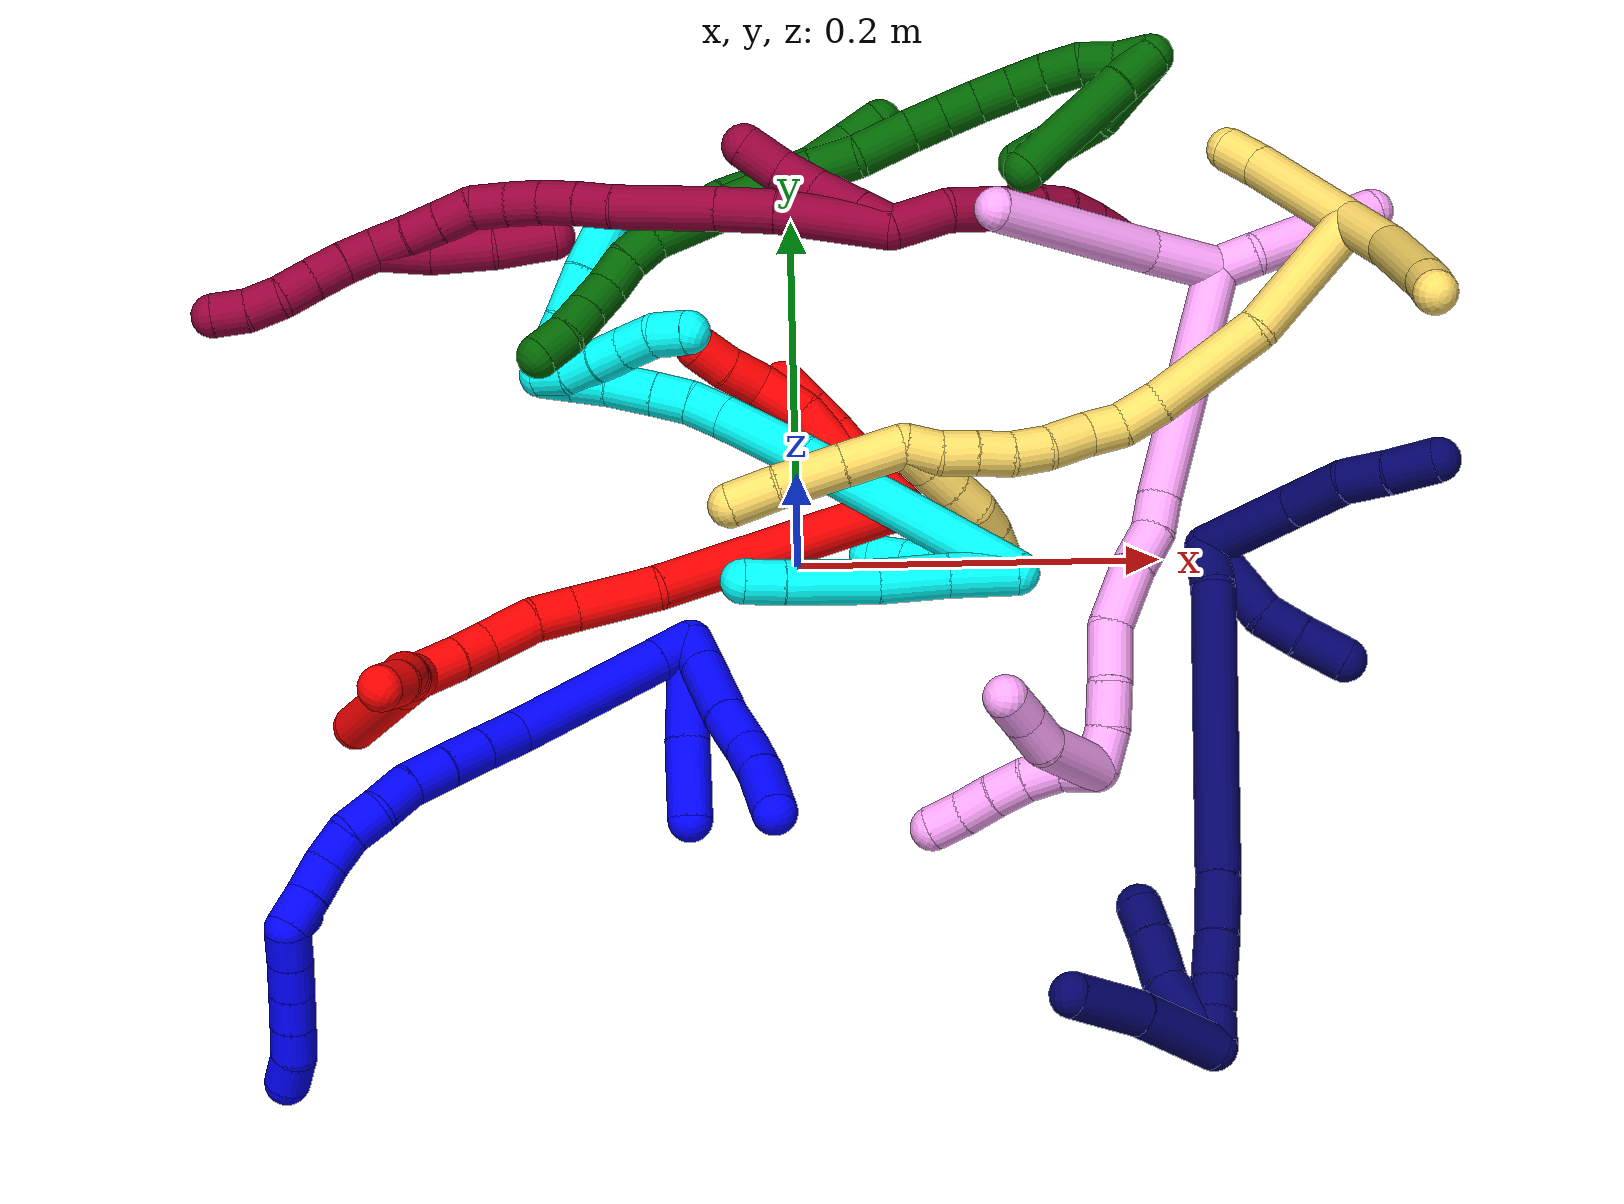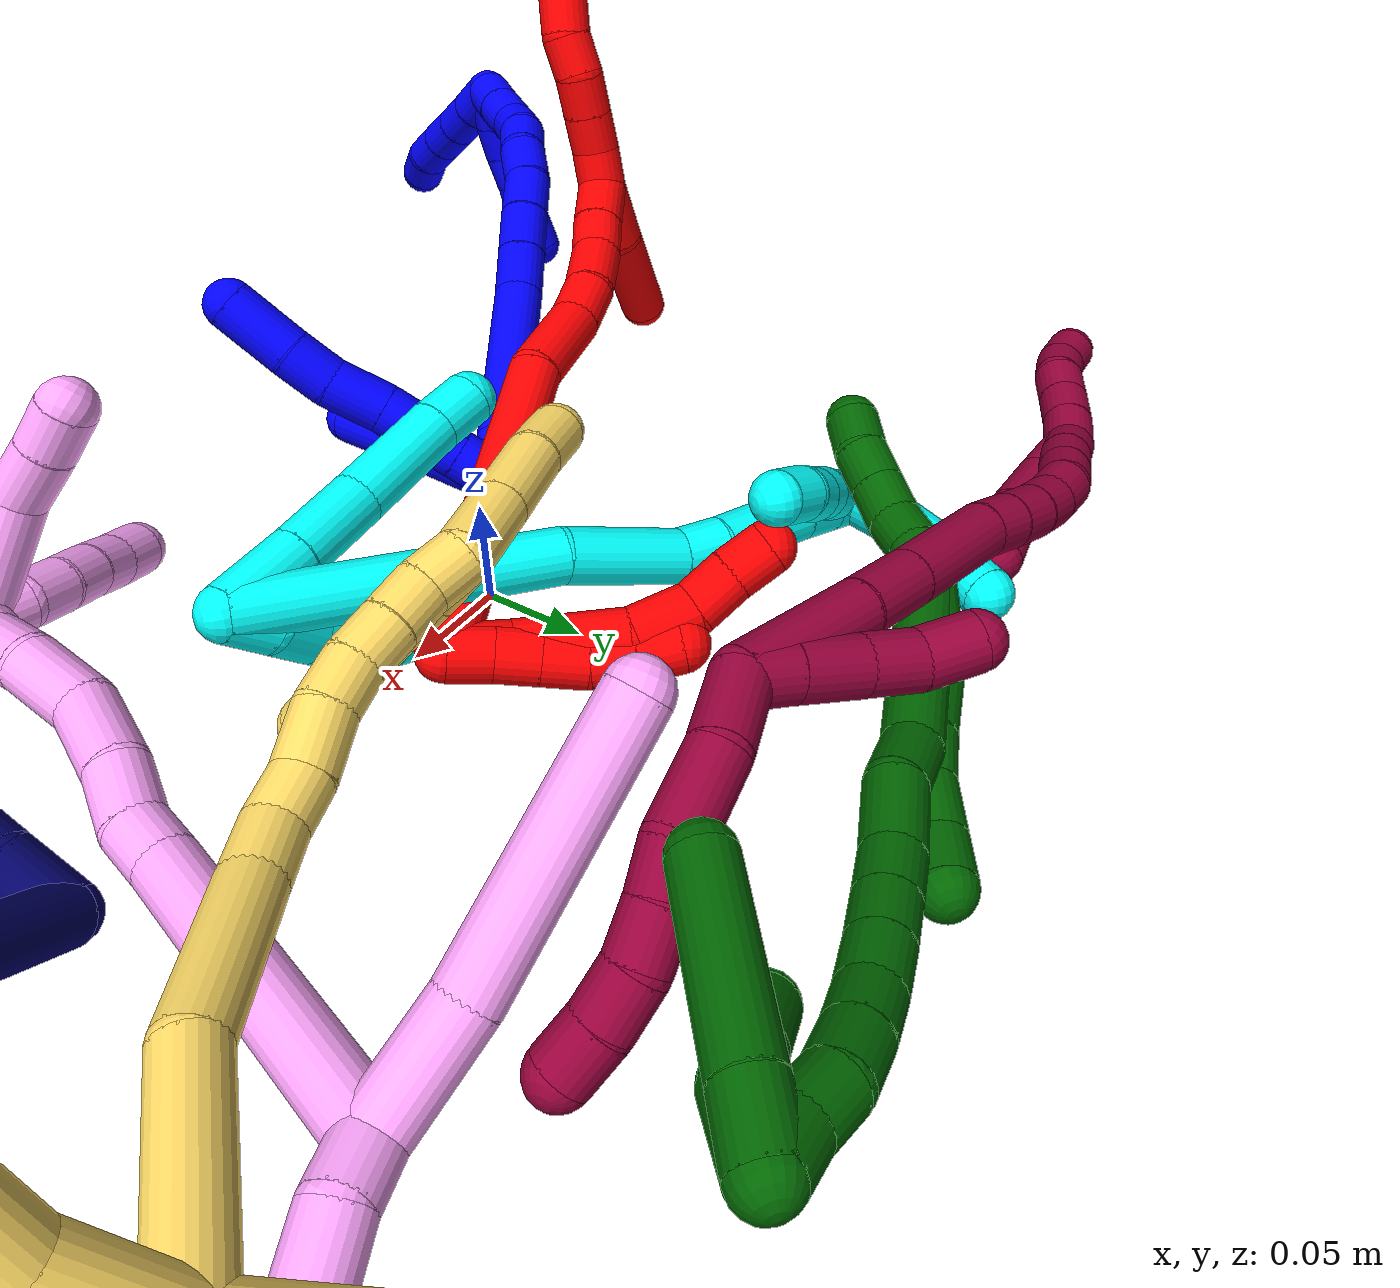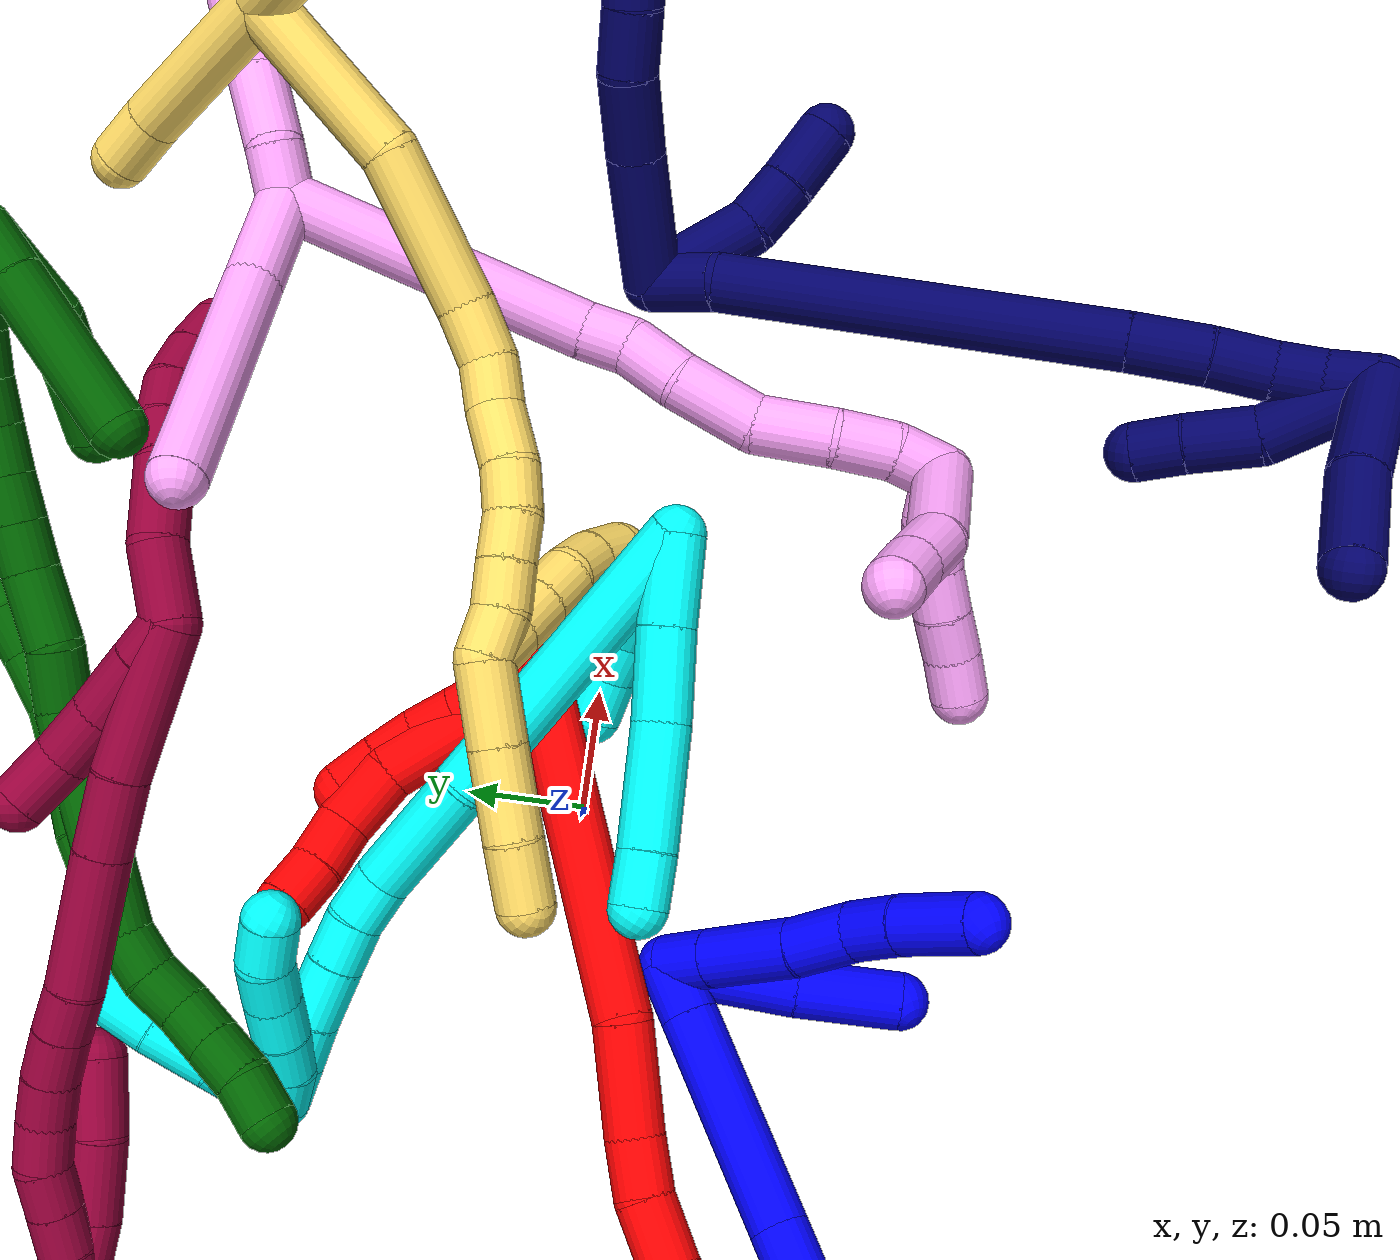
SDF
<sdf version="1.7">
 <world name="default">
  <plugin name="TubeGeneratorPlugin" filename="libtube_generator_plugin.so"/>
  <model name="photoneo_s_sensor">
   <static>1</static>
   <pose>0 0 2 1.57079 1.57079 3.14159</pose>
   <link name="link">
    <inertial><mass>0.1</mass></inertial>
    <sensor name="sensor" type="depth">
     <update_rate>30</update_rate>
     <camera>
      <horizontal_fov>1.22</horizontal_fov>
      <image><width>1920</width><height>1200</height><format>B8G8R8</format></image>
      <clip><near>0.1</near><far>4</far></clip>
      <depth_camera><output>points</output></depth_camera>
     </camera>
     <plugin name="camera_plugin" filename="libgazebo_ros_depth_camera.so">
      <baseline>0.2</baseline>
      <alwaysOn>1</alwaysOn>
      <updateRate>0.0</updateRate>
      <cameraName>camera_ir</cameraName>
      <imageTopicName>/camera/color/image_raw</imageTopicName>
      <cameraInfoTopicName>/camera/color/camera_info</cameraInfoTopicName>
      <depthImageTopicName>/camera/depth/image_raw</depthImageTopicName>
      <depthImageCameraInfoTopicName>/camera/depth/camera_info</depthImageCameraInfoTopicName>
      <pointCloudTopicName>/camera/depth/points</pointCloudTopicName>
      <frameName>fr_optical</frameName>
      <pointCloudCutoff>0.1</pointCloudCutoff>
      <pointCloudCutoffMax>2.0</pointCloudCutoffMax>
      <distortionK1>0</distortionK1>
      <distortionK2>0</distortionK2>
      <distortionK3>0</distortionK3>
      <distortionT1>0</distortionT1>
      <distortionT2>0</distortionT2>
      <CxPrime>0</CxPrime>
      <Cx>0</Cx>
      <Cy>0</Cy>
      <focalLength>0</focalLength>
      <hackBaseline>0</hackBaseline>
     </plugin>
    </sensor>
   </link>
  </model>
  <gravity>0 0 -9.8</gravity>
  <magnetic_field>6e-06 2.3e-05 -4.2e-05</magnetic_field>
  <atmosphere type="adiabatic"/>
  <physics name="default_physics" default="0" type="ode">
   <max_step_size>0.003</max_step_size>
   <real_time_factor>1</real_time_factor>
   <real_time_update_rate>1000</real_time_update_rate>
   <max_contacts>10000</max_contacts>
   <ode>
    <solver>
     <type>quick</type>
     <iters>100</iters>
     <sor>1.3</sor>
     <use_dynamic_moi_rescaling>0</use_dynamic_moi_rescaling>
    </solver>
    <constraints>
     <contact_max_correcting_vel>0</contact_max_correcting_vel>
     <contact_surface_layer>0.001</contact_surface_layer>
     <cfm>0</cfm>
     <erp>0.2</erp>
    </constraints>
   </ode>
  </physics>
  <scene><ambient>0.4 0.4 0.4 1</ambient><background>0.7 0.7 0.7 1</background><shadows>0</shadows></scene>
  <audio><device>default</device></audio>
  <spherical_coordinates>
   <surface_model>EARTH_WGS84</surface_model>
   <latitude_deg>0</latitude_deg>
   <longitude_deg>0</longitude_deg>
   <elevation>0</elevation>
   <heading_deg>0</heading_deg>
  </spherical_coordinates>
  <model name="bin">
   <static>1</static>
   <link name="bottom">
    <collision name="collision-bottom">
     <pose>0 0 -0.01 0 -0 0</pose>
     <geometry><box><size>0.8 0.6 0.02</size></box></geometry>
     <surface>
      <friction><ode><mu>100</mu><mu2>100</mu2></ode></friction>
      <contact><collide_bitmask>65535</collide_bitmask></contact>
     </surface>
    </collision>
   </link>
   <link name="west_wall">
    <collision name="collision-west_wall">
     <pose>-0.41 0 0.1 0 -0 0</pose>
     <geometry><box><size>0.02 0.6 0.2</size></box></geometry>
     <surface>
      <friction><ode><mu>100</mu><mu2>100</mu2></ode></friction>
      <contact><collide_bitmask>65535</collide_bitmask></contact>
     </surface>
    </collision>
   </link>
   <link name="east_wall">
    <collision name="collision-east_wall">
     <pose>0.41 0 0.1 0 -0 0</pose>
     <geometry><box><size>0.02 0.6 0.2</size></box></geometry>
     <surface>
      <friction><ode><mu>100</mu><mu2>100</mu2></ode></friction>
      <contact><collide_bitmask>65535</collide_bitmask></contact>
     </surface>
    </collision>
   </link>
   <link name="south_wall">
    <collision name="collision-south_wall">
     <pose>0 -0.31 0.1 0 -0 0</pose>
     <geometry><box><size>0.8 0.02 0.2</size></box></geometry>
     <surface>
      <friction><ode><mu>100</mu><mu2>100</mu2></ode></friction>
      <contact><collide_bitmask>65535</collide_bitmask></contact>
     </surface>
    </collision>
   </link>
   <link name="north_wall">
    <collision name="collision-north_wall">
     <pose>0 0.31 0.1 0 -0 0</pose>
     <geometry><box><size>0.8 0.02 0.2</size></box></geometry>
     <surface>
      <friction><ode><mu>100</mu><mu2>100</mu2></ode></friction>
      <contact><collide_bitmask>65535</collide_bitmask></contact>
     </surface>
    </collision>
   </link>
  </model>
  <model name="1">
   <static>0</static>
   <link name="1">
    <collision name="collision-cylinder-e_1_2_8">
     <pose>0.008296 -0.004223 0.006235 0.595325 0.833692 0.270026</pose>
     <geometry><cylinder><radius>0.0125</radius><length>0.022409</length></cylinder></geometry>
     <surface>
      <friction><ode><mu>1.16</mu><mu2>1.16</mu2><slip1>0</slip1><slip2>0</slip2></ode></friction>
      <contact><ode><kp>1e+06</kp><kd>1</kd><max_vel>0</max_vel><min_depth>0.001</min_depth></ode></contact>
     </surface>
    </collision>
    <visual name="visual-cylinder-e_1_2_8">
     <pose>0.008296 -0.004223 0.006235 0.595325 0.833692 0.270026</pose>
     <geometry><cylinder><radius>0.0125</radius><length>0.022409</length></cylinder></geometry>
     <material><ambient>0 0 1 1</ambient></material>
    </visual>
    <collision name="collision-cylinder-e_2_8_9">
     <pose>0.03185 -0.01634 0.024078 0.597208 0.827069 0.268531</pose>
     <geometry><cylinder><radius>0.0125</radius><length>0.041465</length></cylinder></geometry>
     <surface>
      <friction><ode><mu>1.16</mu><mu2>1.16</mu2><slip1>0</slip1><slip2>0</slip2></ode></friction>
      <contact><ode><kp>1e+06</kp><kd>1</kd><max_vel>0</max_vel><min_depth>0.001</min_depth></ode></contact>
     </surface>
    </collision>
    <visual name="visual-cylinder-e_2_8_9">
     <pose>0.03185 -0.01634 0.024078 0.597208 0.827069 0.268531</pose>
     <geometry><cylinder><radius>0.0125</radius><length>0.041465</length></cylinder></geometry>
     <material><ambient>0 0 1 1</ambient></material>
    </visual>
    <collision name="collision-cylinder-e_3_9_10">
     <pose>0.058178 -0.029995 0.042104 0.731516 0.908875 0.369935</pose>
     <geometry><cylinder><radius>0.0125</radius><length>0.028068</length></cylinder></geometry>
     <surface>
      <friction><ode><mu>1.16</mu><mu2>1.16</mu2><slip1>0</slip1><slip2>0</slip2></ode></friction>
      <contact><ode><kp>1e+06</kp><kd>1</kd><max_vel>0</max_vel><min_depth>0.001</min_depth></ode></contact>
     </surface>
    </collision>
    <visual name="visual-cylinder-e_3_9_10">
     <pose>0.058178 -0.029995 0.042104 0.731516 0.908875 0.369935</pose>
     <geometry><cylinder><radius>0.0125</radius><length>0.028068</length></cylinder></geometry>
     <material><ambient>0 0 1 1</ambient></material>
    </visual>
    <collision name="collision-cylinder-e_4_10_11">
     <pose>0.078135 -0.03874 0.055174 0.421561 0.883815 0.201766</pose>
     <geometry><cylinder><radius>0.0125</radius><length>0.022989</length></cylinder></geometry>
     <surface>
      <friction><ode><mu>1.16</mu><mu2>1.16</mu2><slip1>0</slip1><slip2>0</slip2></ode></friction>
      <contact><ode><kp>1e+06</kp><kd>1</kd><max_vel>0</max_vel><min_depth>0.001</min_depth></ode></contact>
     </surface>
    </collision>
    <visual name="visual-cylinder-e_4_10_11">
     <pose>0.078135 -0.03874 0.055174 0.421561 0.883815 0.201766</pose>
     <geometry><cylinder><radius>0.0125</radius><length>0.022989</length></cylinder></geometry>
     <material><ambient>0 0 1 1</ambient></material>
    </visual>
    <collision name="collision-cylinder-e_5_11_6">
     <pose>0.099402 -0.0469 0.073114 0.430044 0.783802 0.180031</pose>
     <geometry><cylinder><radius>0.0125</radius><length>0.03507</length></cylinder></geometry>
     <surface>
      <friction><ode><mu>1.16</mu><mu2>1.16</mu2><slip1>0</slip1><slip2>0</slip2></ode></friction>
      <contact><ode><kp>1e+06</kp><kd>1</kd><max_vel>0</max_vel><min_depth>0.001</min_depth></ode></contact>
     </surface>
    </collision>
    <visual name="visual-cylinder-e_5_11_6">
     <pose>0.099402 -0.0469 0.073114 0.430044 0.783802 0.180031</pose>
     <geometry><cylinder><radius>0.0125</radius><length>0.03507</length></cylinder></geometry>
     <material><ambient>0 0 1 1</ambient></material>
    </visual>
    <collision name="collision-cylinder-e_1_2_12">
     <pose>0.005255 -0.021942 0.015984 0.941233 0.191227 0.097505</pose>
     <geometry><cylinder><radius>0.0125</radius><length>0.055302</length></cylinder></geometry>
     <surface>
      <friction><ode><mu>1.16</mu><mu2>1.16</mu2><slip1>0</slip1><slip2>0</slip2></ode></friction>
      <contact><ode><kp>1e+06</kp><kd>1</kd><max_vel>0</max_vel><min_depth>0.001</min_depth></ode></contact>
     </surface>
    </collision>
    <visual name="visual-cylinder-e_1_2_12">
     <pose>0.005255 -0.021942 0.015984 0.941233 0.191227 0.097505</pose>
     <geometry><cylinder><radius>0.0125</radius><length>0.055302</length></cylinder></geometry>
     <material><ambient>0 0 1 1</ambient></material>
    </visual>
    <collision name="collision-cylinder-e_2_12_5">
     <pose>0.016306 -0.061556 0.044362 0.959154 0.262323 0.137</pose>
     <geometry><cylinder><radius>0.0125</radius><length>0.044698</length></cylinder></geometry>
     <surface>
      <friction><ode><mu>1.16</mu><mu2>1.16</mu2><slip1>0</slip1><slip2>0</slip2></ode></friction>
      <contact><ode><kp>1e+06</kp><kd>1</kd><max_vel>0</max_vel><min_depth>0.001</min_depth></ode></contact>
     </surface>
    </collision>
    <visual name="visual-cylinder-e_2_12_5">
     <pose>0.016306 -0.061556 0.044362 0.959154 0.262323 0.137</pose>
     <geometry><cylinder><radius>0.0125</radius><length>0.044698</length></cylinder></geometry>
     <material><ambient>0 0 1 1</ambient></material>
    </visual>
    <collision name="collision-cylinder-e_1_2_13">
     <pose>-0.00335 -0.000417 0.011633 0.03581 -0.280254 -0.005052</pose>
     <geometry><cylinder><radius>0.0125</radius><length>0.024226</length></cylinder></geometry>
     <surface>
      <friction><ode><mu>1.16</mu><mu2>1.16</mu2><slip1>0</slip1><slip2>0</slip2></ode></friction>
      <contact><ode><kp>1e+06</kp><kd>1</kd><max_vel>0</max_vel><min_depth>0.001</min_depth></ode></contact>
     </surface>
    </collision>
    <visual name="visual-cylinder-e_1_2_13">
     <pose>-0.00335 -0.000417 0.011633 0.03581 -0.280254 -0.005052</pose>
     <geometry><cylinder><radius>0.0125</radius><length>0.024226</length></cylinder></geometry>
     <material><ambient>0 0 1 1</ambient></material>
    </visual>
    <collision name="collision-cylinder-e_2_13_14">
     <pose>-0.019933 -0.002295 0.068716 0.032141 -0.283172 -0.004582</pose>
     <geometry><cylinder><radius>0.0125</radius><length>0.094719</length></cylinder></geometry>
     <surface>
      <friction><ode><mu>1.16</mu><mu2>1.16</mu2><slip1>0</slip1><slip2>0</slip2></ode></friction>
      <contact><ode><kp>1e+06</kp><kd>1</kd><max_vel>0</max_vel><min_depth>0.001</min_depth></ode></contact>
     </surface>
    </collision>
    <visual name="visual-cylinder-e_2_13_14">
     <pose>-0.019933 -0.002295 0.068716 0.032141 -0.283172 -0.004582</pose>
     <geometry><cylinder><radius>0.0125</radius><length>0.094719</length></cylinder></geometry>
     <material><ambient>0 0 1 1</ambient></material>
    </visual>
    <collision name="collision-cylinder-e_3_14_15">
     <pose>-0.035139 -0.00288 0.127018 -0.068049 -0.152045 0.005185</pose>
     <geometry><cylinder><radius>0.0125</radius><length>0.026065</length></cylinder></geometry>
     <surface>
      <friction><ode><mu>1.16</mu><mu2>1.16</mu2><slip1>0</slip1><slip2>0</slip2></ode></friction>
      <contact><ode><kp>1e+06</kp><kd>1</kd><max_vel>0</max_vel><min_depth>0.001</min_depth></ode></contact>
     </surface>
    </collision>
    <visual name="visual-cylinder-e_3_14_15">
     <pose>-0.035139 -0.00288 0.127018 -0.068049 -0.152045 0.005185</pose>
     <geometry><cylinder><radius>0.0125</radius><length>0.026065</length></cylinder></geometry>
     <material><ambient>0 0 1 1</ambient></material>
    </visual>
    <collision name="collision-cylinder-e_4_15_16">
     <pose>-0.039325 -0.001429 0.152393 -0.045884 -0.174613 0.004017</pose>
     <geometry><cylinder><radius>0.0125</radius><length>0.025459</length></cylinder></geometry>
     <surface>
      <friction><ode><mu>1.16</mu><mu2>1.16</mu2><slip1>0</slip1><slip2>0</slip2></ode></friction>
      <contact><ode><kp>1e+06</kp><kd>1</kd><max_vel>0</max_vel><min_depth>0.001</min_depth></ode></contact>
     </surface>
    </collision>
    <visual name="visual-cylinder-e_4_15_16">
     <pose>-0.039325 -0.001429 0.152393 -0.045884 -0.174613 0.004017</pose>
     <geometry><cylinder><radius>0.0125</radius><length>0.025459</length></cylinder></geometry>
     <material><ambient>0 0 1 1</ambient></material>
    </visual>
    <collision name="collision-cylinder-e_5_16_17">
     <pose>-0.044395 -0.000812 0.176935 -0.003475 -0.233494 0.000408</pose>
     <geometry><cylinder><radius>0.0125</radius><length>0.024709</length></cylinder></geometry>
     <surface>
      <friction><ode><mu>1.16</mu><mu2>1.16</mu2><slip1>0</slip1><slip2>0</slip2></ode></friction>
      <contact><ode><kp>1e+06</kp><kd>1</kd><max_vel>0</max_vel><min_depth>0.001</min_depth></ode></contact>
     </surface>
    </collision>
    <visual name="visual-cylinder-e_5_16_17">
     <pose>-0.044395 -0.000812 0.176935 -0.003475 -0.233494 0.000408</pose>
     <geometry><cylinder><radius>0.0125</radius><length>0.024709</length></cylinder></geometry>
     <material><ambient>0 0 1 1</ambient></material>
    </visual>
    <collision name="collision-cylinder-e_6_17_18">
     <pose>-0.048677 -0.002723 0.200081 0.173703 -0.125312 -0.010925</pose>
     <geometry><cylinder><radius>0.0125</radius><length>0.022772</length></cylinder></geometry>
     <surface>
      <friction><ode><mu>1.16</mu><mu2>1.16</mu2><slip1>0</slip1><slip2>0</slip2></ode></friction>
      <contact><ode><kp>1e+06</kp><kd>1</kd><max_vel>0</max_vel><min_depth>0.001</min_depth></ode></contact>
     </surface>
    </collision>
    <visual name="visual-cylinder-e_6_17_18">
     <pose>-0.048677 -0.002723 0.200081 0.173703 -0.125312 -0.010925</pose>
     <geometry><cylinder><radius>0.0125</radius><length>0.022772</length></cylinder></geometry>
     <material><ambient>0 0 1 1</ambient></material>
    </visual>
    <collision name="collision-cylinder-e_7_18_19">
     <pose>-0.0538 -0.007373 0.220312 0.288041 -0.37156 -0.054501</pose>
     <geometry><cylinder><radius>0.0125</radius><length>0.020382</length></cylinder></geometry>
     <surface>
      <friction><ode><mu>1.16</mu><mu2>1.16</mu2><slip1>0</slip1><slip2>0</slip2></ode></friction>
      <contact><ode><kp>1e+06</kp><kd>1</kd><max_vel>0</max_vel><min_depth>0.001</min_depth></ode></contact>
     </surface>
    </collision>
    <visual name="visual-cylinder-e_7_18_19">
     <pose>-0.0538 -0.007373 0.220312 0.288041 -0.37156 -0.054501</pose>
     <geometry><cylinder><radius>0.0125</radius><length>0.020382</length></cylinder></geometry>
     <material><ambient>0 0 1 1</ambient></material>
    </visual>
    <collision name="collision-cylinder-e_8_19_20">
     <pose>-0.060742 -0.015711 0.237079 0.634526 -0.328384 -0.108699</pose>
     <geometry><cylinder><radius>0.0125</radius><length>0.020104</length></cylinder></geometry>
     <surface>
      <friction><ode><mu>1.16</mu><mu2>1.16</mu2><slip1>0</slip1><slip2>0</slip2></ode></friction>
      <contact><ode><kp>1e+06</kp><kd>1</kd><max_vel>0</max_vel><min_depth>0.001</min_depth></ode></contact>
     </surface>
    </collision>
    <visual name="visual-cylinder-e_8_19_20">
     <pose>-0.060742 -0.015711 0.237079 0.634526 -0.328384 -0.108699</pose>
     <geometry><cylinder><radius>0.0125</radius><length>0.020104</length></cylinder></geometry>
     <material><ambient>0 0 1 1</ambient></material>
    </visual>
    <collision name="collision-cylinder-e_9_20_21">
     <pose>-0.064733 -0.026809 0.253623 0.551003 -0.071809 -0.020308</pose>
     <geometry><cylinder><radius>0.0125</radius><length>0.020902</length></cylinder></geometry>
     <surface>
      <friction><ode><mu>1.16</mu><mu2>1.16</mu2><slip1>0</slip1><slip2>0</slip2></ode></friction>
      <contact><ode><kp>1e+06</kp><kd>1</kd><max_vel>0</max_vel><min_depth>0.001</min_depth></ode></contact>
     </surface>
    </collision>
    <visual name="visual-cylinder-e_9_20_21">
     <pose>-0.064733 -0.026809 0.253623 0.551003 -0.071809 -0.020308</pose>
     <geometry><cylinder><radius>0.0125</radius><length>0.020902</length></cylinder></geometry>
     <material><ambient>0 0 1 1</ambient></material>
    </visual>
    <collision name="collision-cylinder-e_10_21_1">
     <pose>-0.066635 -0.037468 0.271356 0.531344 -0.111723 -0.03043</pose>
     <geometry><cylinder><radius>0.0125</radius><length>0.020662</length></cylinder></geometry>
     <surface>
      <friction><ode><mu>1.16</mu><mu2>1.16</mu2><slip1>0</slip1><slip2>0</slip2></ode></friction>
      <contact><ode><kp>1e+06</kp><kd>1</kd><max_vel>0</max_vel><min_depth>0.001</min_depth></ode></contact>
     </surface>
    </collision>
    <visual name="visual-cylinder-e_10_21_1">
     <pose>-0.066635 -0.037468 0.271356 0.531344 -0.111723 -0.03043</pose>
     <geometry><cylinder><radius>0.0125</radius><length>0.020662</length></cylinder></geometry>
     <material><ambient>0 0 1 1</ambient></material>
    </visual>
    <collision name="collision-cylinder-e_1_1_22">
     <pose>-0.070291 -0.052348 0.279967 1.59554 -0.253172 -0.259444</pose>
     <geometry><cylinder><radius>0.0125</radius><length>0.02</length></cylinder></geometry>
     <surface>
      <friction><ode><mu>1.16</mu><mu2>1.16</mu2><slip1>0</slip1><slip2>0</slip2></ode></friction>
      <contact><ode><kp>1e+06</kp><kd>1</kd><max_vel>0</max_vel><min_depth>0.001</min_depth></ode></contact>
     </surface>
    </collision>
    <visual name="visual-cylinder-e_1_1_22">
     <pose>-0.070291 -0.052348 0.279967 1.59554 -0.253172 -0.259444</pose>
     <geometry><cylinder><radius>0.0125</radius><length>0.02</length></cylinder></geometry>
     <material><ambient>0 0 1 1</ambient></material>
    </visual>
    <collision name="collision-cylinder-e_2_22_23">
     <pose>-0.075274 -0.07171 0.280013 1.54134 -0.250436 -0.243238</pose>
     <geometry><cylinder><radius>0.0125</radius><length>0.02</length></cylinder></geometry>
     <surface>
      <friction><ode><mu>1.16</mu><mu2>1.16</mu2><slip1>0</slip1><slip2>0</slip2></ode></friction>
      <contact><ode><kp>1e+06</kp><kd>1</kd><max_vel>0</max_vel><min_depth>0.001</min_depth></ode></contact>
     </surface>
    </collision>
    <visual name="visual-cylinder-e_2_22_23">
     <pose>-0.075274 -0.07171 0.280013 1.54134 -0.250436 -0.243238</pose>
     <geometry><cylinder><radius>0.0125</radius><length>0.02</length></cylinder></geometry>
     <material><ambient>0 0 1 1</ambient></material>
    </visual>
    <collision name="collision-cylinder-e_3_23_24">
     <pose>-0.080184 -0.091081 0.280797 1.51936 -0.245606 -0.233401</pose>
     <geometry><cylinder><radius>0.0125</radius><length>0.02</length></cylinder></geometry>
     <surface>
      <friction><ode><mu>1.16</mu><mu2>1.16</mu2><slip1>0</slip1><slip2>0</slip2></ode></friction>
      <contact><ode><kp>1e+06</kp><kd>1</kd><max_vel>0</max_vel><min_depth>0.001</min_depth></ode></contact>
     </surface>
    </collision>
    <visual name="visual-cylinder-e_3_23_24">
     <pose>-0.080184 -0.091081 0.280797 1.51936 -0.245606 -0.233401</pose>
     <geometry><cylinder><radius>0.0125</radius><length>0.02</length></cylinder></geometry>
     <material><ambient>0 0 1 1</ambient></material>
    </visual>
    <collision name="collision-cylinder-e_4_24_25">
     <pose>-0.085139 -0.110437 0.281677 1.53135 -0.255066 -0.245298</pose>
     <geometry><cylinder><radius>0.0125</radius><length>0.02</length></cylinder></geometry>
     <surface>
      <friction><ode><mu>1.16</mu><mu2>1.16</mu2><slip1>0</slip1><slip2>0</slip2></ode></friction>
      <contact><ode><kp>1e+06</kp><kd>1</kd><max_vel>0</max_vel><min_depth>0.001</min_depth></ode></contact>
     </surface>
    </collision>
    <visual name="visual-cylinder-e_4_24_25">
     <pose>-0.085139 -0.110437 0.281677 1.53135 -0.255066 -0.245298</pose>
     <geometry><cylinder><radius>0.0125</radius><length>0.02</length></cylinder></geometry>
     <material><ambient>0 0 1 1</ambient></material>
    </visual>
    <collision name="collision-cylinder-e_5_25_4">
     <pose>-0.092769 -0.128695 0.282452 1.52503 -0.536071 -0.513141</pose>
     <geometry><cylinder><radius>0.0125</radius><length>0.02</length></cylinder></geometry>
     <surface>
      <friction><ode><mu>1.16</mu><mu2>1.16</mu2><slip1>0</slip1><slip2>0</slip2></ode></friction>
      <contact><ode><kp>1e+06</kp><kd>1</kd><max_vel>0</max_vel><min_depth>0.001</min_depth></ode></contact>
     </surface>
    </collision>
    <visual name="visual-cylinder-e_5_25_4">
     <pose>-0.092769 -0.128695 0.282452 1.52503 -0.536071 -0.513141</pose>
     <geometry><cylinder><radius>0.0125</radius><length>0.02</length></cylinder></geometry>
     <material><ambient>0 0 1 1</ambient></material>
    </visual>
    <collision name="collision-cylinder-e_1_1_26">
     <pose>-0.074558 -0.047321 0.274504 2.45745 -0.743788 -1.66181</pose>
     <geometry><cylinder><radius>0.0125</radius><length>0.02</length></cylinder></geometry>
     <surface>
      <friction><ode><mu>1.16</mu><mu2>1.16</mu2><slip1>0</slip1><slip2>0</slip2></ode></friction>
      <contact><ode><kp>1e+06</kp><kd>1</kd><max_vel>0</max_vel><min_depth>0.001</min_depth></ode></contact>
     </surface>
    </collision>
    <visual name="visual-cylinder-e_1_1_26">
     <pose>-0.074558 -0.047321 0.274504 2.45745 -0.743788 -1.66181</pose>
     <geometry><cylinder><radius>0.0125</radius><length>0.02</length></cylinder></geometry>
     <material><ambient>0 0 1 1</ambient></material>
    </visual>
    <collision name="collision-cylinder-e_2_26_27">
     <pose>-0.088136 -0.055616 0.262446 2.62093 -0.748804 -1.95011</pose>
     <geometry><cylinder><radius>0.0125</radius><length>0.02</length></cylinder></geometry>
     <surface>
      <friction><ode><mu>1.16</mu><mu2>1.16</mu2><slip1>0</slip1><slip2>0</slip2></ode></friction>
      <contact><ode><kp>1e+06</kp><kd>1</kd><max_vel>0</max_vel><min_depth>0.001</min_depth></ode></contact>
     </surface>
    </collision>
    <visual name="visual-cylinder-e_2_26_27">
     <pose>-0.088136 -0.055616 0.262446 2.62093 -0.748804 -1.95011</pose>
     <geometry><cylinder><radius>0.0125</radius><length>0.02</length></cylinder></geometry>
     <material><ambient>0 0 1 1</ambient></material>
    </visual>
    <collision name="collision-cylinder-e_3_27_28">
     <pose>-0.101354 -0.061649 0.248798 2.82506 -0.695839 -2.31246</pose>
     <geometry><cylinder><radius>0.0125</radius><length>0.02</length></cylinder></geometry>
     <surface>
      <friction><ode><mu>1.16</mu><mu2>1.16</mu2><slip1>0</slip1><slip2>0</slip2></ode></friction>
      <contact><ode><kp>1e+06</kp><kd>1</kd><max_vel>0</max_vel><min_depth>0.001</min_depth></ode></contact>
     </surface>
    </collision>
    <visual name="visual-cylinder-e_3_27_28">
     <pose>-0.101354 -0.061649 0.248798 2.82506 -0.695839 -2.31246</pose>
     <geometry><cylinder><radius>0.0125</radius><length>0.02</length></cylinder></geometry>
     <material><ambient>0 0 1 1</ambient></material>
    </visual>
    <collision name="collision-cylinder-e_4_28_29">
     <pose>-0.112716 -0.066255 0.233104 2.88355 -0.518025 -2.23092</pose>
     <geometry><cylinder><radius>0.0125</radius><length>0.02</length></cylinder></geometry>
     <surface>
      <friction><ode><mu>1.16</mu><mu2>1.16</mu2><slip1>0</slip1><slip2>0</slip2></ode></friction>
      <contact><ode><kp>1e+06</kp><kd>1</kd><max_vel>0</max_vel><min_depth>0.001</min_depth></ode></contact>
     </surface>
    </collision>
    <visual name="visual-cylinder-e_4_28_29">
     <pose>-0.112716 -0.066255 0.233104 2.88355 -0.518025 -2.23092</pose>
     <geometry><cylinder><radius>0.0125</radius><length>0.02</length></cylinder></geometry>
     <material><ambient>0 0 1 1</ambient></material>
    </visual>
    <collision name="collision-cylinder-e_5_29_3">
     <pose>-0.124801 -0.071467 0.218368 2.70002 -0.794268 -2.15888</pose>
     <geometry><cylinder><radius>0.0125</radius><length>0.02</length></cylinder></geometry>
     <surface>
      <friction><ode><mu>1.16</mu><mu2>1.16</mu2><slip1>0</slip1><slip2>0</slip2></ode></friction>
      <contact><ode><kp>1e+06</kp><kd>1</kd><max_vel>0</max_vel><min_depth>0.001</min_depth></ode></contact>
     </surface>
    </collision>
    <visual name="visual-cylinder-e_5_29_3">
     <pose>-0.124801 -0.071467 0.218368 2.70002 -0.794268 -2.15888</pose>
     <geometry><cylinder><radius>0.0125</radius><length>0.02</length></cylinder></geometry>
     <material><ambient>0 0 1 1</ambient></material>
    </visual>
    <collision name="collision-sphere-3">
     <pose>-0.131934 -0.074462 0.212032 0 -0 0</pose>
     <geometry><sphere><radius>0.0125</radius></sphere></geometry>
     <surface>
      <friction><ode><mu>1.16</mu><mu2>1.16</mu2><slip1>0</slip1><slip2>0</slip2></ode></friction>
      <contact><ode><kp>1e+06</kp><kd>1</kd><max_vel>0</max_vel><min_depth>0.001</min_depth></ode></contact>
     </surface>
    </collision>
    <visual name="visual-sphere-3">
     <pose>-0.131934 -0.074462 0.212032 0 -0 0</pose>
     <geometry><sphere><radius>0.0125</radius></sphere></geometry>
     <material><ambient>0 0 1 1</ambient></material>
    </visual>
    <collision name="collision-sphere-29">
     <pose>-0.117667 -0.068472 0.224704 0 -0 0</pose>
     <geometry><sphere><radius>0.0125</radius></sphere></geometry>
     <surface>
      <friction><ode><mu>1.16</mu><mu2>1.16</mu2><slip1>0</slip1><slip2>0</slip2></ode></friction>
      <contact><ode><kp>1e+06</kp><kd>1</kd><max_vel>0</max_vel><min_depth>0.001</min_depth></ode></contact>
     </surface>
    </collision>
    <visual name="visual-sphere-29">
     <pose>-0.117667 -0.068472 0.224704 0 -0 0</pose>
     <geometry><sphere><radius>0.0125</radius></sphere></geometry>
     <material><ambient>0 0 1 1</ambient></material>
    </visual>
    <collision name="collision-sphere-28">
     <pose>-0.107764 -0.064038 0.241504 0 -0 0</pose>
     <geometry><sphere><radius>0.0125</radius></sphere></geometry>
     <surface>
      <friction><ode><mu>1.16</mu><mu2>1.16</mu2><slip1>0</slip1><slip2>0</slip2></ode></friction>
      <contact><ode><kp>1e+06</kp><kd>1</kd><max_vel>0</max_vel><min_depth>0.001</min_depth></ode></contact>
     </surface>
    </collision>
    <visual name="visual-sphere-28">
     <pose>-0.107764 -0.064038 0.241504 0 -0 0</pose>
     <geometry><sphere><radius>0.0125</radius></sphere></geometry>
     <material><ambient>0 0 1 1</ambient></material>
    </visual>
    <collision name="collision-sphere-27">
     <pose>-0.094944 -0.05926 0.256092 0 -0 0</pose>
     <geometry><sphere><radius>0.0125</radius></sphere></geometry>
     <surface>
      <friction><ode><mu>1.16</mu><mu2>1.16</mu2><slip1>0</slip1><slip2>0</slip2></ode></friction>
      <contact><ode><kp>1e+06</kp><kd>1</kd><max_vel>0</max_vel><min_depth>0.001</min_depth></ode></contact>
     </surface>
    </collision>
    <visual name="visual-sphere-27">
     <pose>-0.094944 -0.05926 0.256092 0 -0 0</pose>
     <geometry><sphere><radius>0.0125</radius></sphere></geometry>
     <material><ambient>0 0 1 1</ambient></material>
    </visual>
    <collision name="collision-sphere-26">
     <pose>-0.081328 -0.051972 0.268801 0 -0 0</pose>
     <geometry><sphere><radius>0.0125</radius></sphere></geometry>
     <surface>
      <friction><ode><mu>1.16</mu><mu2>1.16</mu2><slip1>0</slip1><slip2>0</slip2></ode></friction>
      <contact><ode><kp>1e+06</kp><kd>1</kd><max_vel>0</max_vel><min_depth>0.001</min_depth></ode></contact>
     </surface>
    </collision>
    <visual name="visual-sphere-26">
     <pose>-0.081328 -0.051972 0.268801 0 -0 0</pose>
     <geometry><sphere><radius>0.0125</radius></sphere></geometry>
     <material><ambient>0 0 1 1</ambient></material>
    </visual>
    <collision name="collision-sphere-4">
     <pose>-0.097877 -0.137283 0.282846 0 -0 0</pose>
     <geometry><sphere><radius>0.0125</radius></sphere></geometry>
     <surface>
      <friction><ode><mu>1.16</mu><mu2>1.16</mu2><slip1>0</slip1><slip2>0</slip2></ode></friction>
      <contact><ode><kp>1e+06</kp><kd>1</kd><max_vel>0</max_vel><min_depth>0.001</min_depth></ode></contact>
     </surface>
    </collision>
    <visual name="visual-sphere-4">
     <pose>-0.097877 -0.137283 0.282846 0 -0 0</pose>
     <geometry><sphere><radius>0.0125</radius></sphere></geometry>
     <material><ambient>0 0 1 1</ambient></material>
    </visual>
    <collision name="collision-sphere-25">
     <pose>-0.087662 -0.120106 0.282059 0 -0 0</pose>
     <geometry><sphere><radius>0.0125</radius></sphere></geometry>
     <surface>
      <friction><ode><mu>1.16</mu><mu2>1.16</mu2><slip1>0</slip1><slip2>0</slip2></ode></friction>
      <contact><ode><kp>1e+06</kp><kd>1</kd><max_vel>0</max_vel><min_depth>0.001</min_depth></ode></contact>
     </surface>
    </collision>
    <visual name="visual-sphere-25">
     <pose>-0.087662 -0.120106 0.282059 0 -0 0</pose>
     <geometry><sphere><radius>0.0125</radius></sphere></geometry>
     <material><ambient>0 0 1 1</ambient></material>
    </visual>
    <collision name="collision-sphere-24">
     <pose>-0.082616 -0.100768 0.281296 0 -0 0</pose>
     <geometry><sphere><radius>0.0125</radius></sphere></geometry>
     <surface>
      <friction><ode><mu>1.16</mu><mu2>1.16</mu2><slip1>0</slip1><slip2>0</slip2></ode></friction>
      <contact><ode><kp>1e+06</kp><kd>1</kd><max_vel>0</max_vel><min_depth>0.001</min_depth></ode></contact>
     </surface>
    </collision>
    <visual name="visual-sphere-24">
     <pose>-0.082616 -0.100768 0.281296 0 -0 0</pose>
     <geometry><sphere><radius>0.0125</radius></sphere></geometry>
     <material><ambient>0 0 1 1</ambient></material>
    </visual>
    <collision name="collision-sphere-23">
     <pose>-0.077753 -0.081394 0.280298 0 -0 0</pose>
     <geometry><sphere><radius>0.0125</radius></sphere></geometry>
     <surface>
      <friction><ode><mu>1.16</mu><mu2>1.16</mu2><slip1>0</slip1><slip2>0</slip2></ode></friction>
      <contact><ode><kp>1e+06</kp><kd>1</kd><max_vel>0</max_vel><min_depth>0.001</min_depth></ode></contact>
     </surface>
    </collision>
    <visual name="visual-sphere-23">
     <pose>-0.077753 -0.081394 0.280298 0 -0 0</pose>
     <geometry><sphere><radius>0.0125</radius></sphere></geometry>
     <material><ambient>0 0 1 1</ambient></material>
    </visual>
    <collision name="collision-sphere-22">
     <pose>-0.072796 -0.062027 0.279728 0 -0 0</pose>
     <geometry><sphere><radius>0.0125</radius></sphere></geometry>
     <surface>
      <friction><ode><mu>1.16</mu><mu2>1.16</mu2><slip1>0</slip1><slip2>0</slip2></ode></friction>
      <contact><ode><kp>1e+06</kp><kd>1</kd><max_vel>0</max_vel><min_depth>0.001</min_depth></ode></contact>
     </surface>
    </collision>
    <visual name="visual-sphere-22">
     <pose>-0.072796 -0.062027 0.279728 0 -0 0</pose>
     <geometry><sphere><radius>0.0125</radius></sphere></geometry>
     <material><ambient>0 0 1 1</ambient></material>
    </visual>
    <collision name="collision-sphere-1">
     <pose>-0.067787 -0.04267 0.280207 0 -0 0</pose>
     <geometry><sphere><radius>0.0125</radius></sphere></geometry>
     <surface>
      <friction><ode><mu>1.16</mu><mu2>1.16</mu2><slip1>0</slip1><slip2>0</slip2></ode></friction>
      <contact><ode><kp>1e+06</kp><kd>1</kd><max_vel>0</max_vel><min_depth>0.001</min_depth></ode></contact>
     </surface>
    </collision>
    <visual name="visual-sphere-1">
     <pose>-0.067787 -0.04267 0.280207 0 -0 0</pose>
     <geometry><sphere><radius>0.0125</radius></sphere></geometry>
     <material><ambient>0 0 1 1</ambient></material>
    </visual>
    <collision name="collision-sphere-21">
     <pose>-0.065483 -0.032266 0.262505 0 -0 0</pose>
     <geometry><sphere><radius>0.0125</radius></sphere></geometry>
     <surface>
      <friction><ode><mu>1.16</mu><mu2>1.16</mu2><slip1>0</slip1><slip2>0</slip2></ode></friction>
      <contact><ode><kp>1e+06</kp><kd>1</kd><max_vel>0</max_vel><min_depth>0.001</min_depth></ode></contact>
     </surface>
    </collision>
    <visual name="visual-sphere-21">
     <pose>-0.065483 -0.032266 0.262505 0 -0 0</pose>
     <geometry><sphere><radius>0.0125</radius></sphere></geometry>
     <material><ambient>0 0 1 1</ambient></material>
    </visual>
    <collision name="collision-sphere-6">
     <pose>0.111781 -0.052078 0.084402 0 -0 0</pose>
     <geometry><sphere><radius>0.0125</radius></sphere></geometry>
     <surface>
      <friction><ode><mu>1.16</mu><mu2>1.16</mu2><slip1>0</slip1><slip2>0</slip2></ode></friction>
      <contact><ode><kp>1e+06</kp><kd>1</kd><max_vel>0</max_vel><min_depth>0.001</min_depth></ode></contact>
     </surface>
    </collision>
    <visual name="visual-sphere-6">
     <pose>0.111781 -0.052078 0.084402 0 -0 0</pose>
     <geometry><sphere><radius>0.0125</radius></sphere></geometry>
     <material><ambient>0 0 1 1</ambient></material>
    </visual>
    <collision name="collision-sphere-11">
     <pose>0.087022 -0.041723 0.061826 0 -0 0</pose>
     <geometry><sphere><radius>0.0125</radius></sphere></geometry>
     <surface>
      <friction><ode><mu>1.16</mu><mu2>1.16</mu2><slip1>0</slip1><slip2>0</slip2></ode></friction>
      <contact><ode><kp>1e+06</kp><kd>1</kd><max_vel>0</max_vel><min_depth>0.001</min_depth></ode></contact>
     </surface>
    </collision>
    <visual name="visual-sphere-11">
     <pose>0.087022 -0.041723 0.061826 0 -0 0</pose>
     <geometry><sphere><radius>0.0125</radius></sphere></geometry>
     <material><ambient>0 0 1 1</ambient></material>
    </visual>
    <collision name="collision-sphere-10">
     <pose>0.069248 -0.035757 0.048522 0 -0 0</pose>
     <geometry><sphere><radius>0.0125</radius></sphere></geometry>
     <surface>
      <friction><ode><mu>1.16</mu><mu2>1.16</mu2><slip1>0</slip1><slip2>0</slip2></ode></friction>
      <contact><ode><kp>1e+06</kp><kd>1</kd><max_vel>0</max_vel><min_depth>0.001</min_depth></ode></contact>
     </surface>
    </collision>
    <visual name="visual-sphere-10">
     <pose>0.069248 -0.035757 0.048522 0 -0 0</pose>
     <geometry><sphere><radius>0.0125</radius></sphere></geometry>
     <material><ambient>0 0 1 1</ambient></material>
    </visual>
    <collision name="collision-sphere-9">
     <pose>0.047108 -0.024233 0.035685 0 -0 0</pose>
     <geometry><sphere><radius>0.0125</radius></sphere></geometry>
     <surface>
      <friction><ode><mu>1.16</mu><mu2>1.16</mu2><slip1>0</slip1><slip2>0</slip2></ode></friction>
      <contact><ode><kp>1e+06</kp><kd>1</kd><max_vel>0</max_vel><min_depth>0.001</min_depth></ode></contact>
     </surface>
    </collision>
    <visual name="visual-sphere-9">
     <pose>0.047108 -0.024233 0.035685 0 -0 0</pose>
     <geometry><sphere><radius>0.0125</radius></sphere></geometry>
     <material><ambient>0 0 1 1</ambient></material>
    </visual>
    <collision name="collision-sphere-2">
     <geometry><sphere><radius>0.0125</radius></sphere></geometry>
     <surface>
      <friction><ode><mu>1.16</mu><mu2>1.16</mu2><slip1>0</slip1><slip2>0</slip2></ode></friction>
      <contact><ode><kp>1e+06</kp><kd>1</kd><max_vel>0</max_vel><min_depth>0.001</min_depth></ode></contact>
     </surface>
    </collision>
    <visual name="visual-sphere-2">
     <geometry><sphere><radius>0.0125</radius></sphere></geometry>
     <material><ambient>0 0 1 1</ambient></material>
    </visual>
    <collision name="collision-sphere-19">
     <pose>-0.0575 -0.01007 0.229416 0 -0 0</pose>
     <geometry><sphere><radius>0.0125</radius></sphere></geometry>
     <surface>
      <friction><ode><mu>1.16</mu><mu2>1.16</mu2><slip1>0</slip1><slip2>0</slip2></ode></friction>
      <contact><ode><kp>1e+06</kp><kd>1</kd><max_vel>0</max_vel><min_depth>0.001</min_depth></ode></contact>
     </surface>
    </collision>
    <visual name="visual-sphere-19">
     <pose>-0.0575 -0.01007 0.229416 0 -0 0</pose>
     <geometry><sphere><radius>0.0125</radius></sphere></geometry>
     <material><ambient>0 0 1 1</ambient></material>
    </visual>
    <collision name="collision-sphere-8">
     <pose>0.016592 -0.008446 0.012471 0 -0 0</pose>
     <geometry><sphere><radius>0.0125</radius></sphere></geometry>
     <surface>
      <friction><ode><mu>1.16</mu><mu2>1.16</mu2><slip1>0</slip1><slip2>0</slip2></ode></friction>
      <contact><ode><kp>1e+06</kp><kd>1</kd><max_vel>0</max_vel><min_depth>0.001</min_depth></ode></contact>
     </surface>
    </collision>
    <visual name="visual-sphere-8">
     <pose>0.016592 -0.008446 0.012471 0 -0 0</pose>
     <geometry><sphere><radius>0.0125</radius></sphere></geometry>
     <material><ambient>0 0 1 1</ambient></material>
    </visual>
    <collision name="collision-sphere-12">
     <pose>0.010511 -0.043885 0.031968 0 -0 0</pose>
     <geometry><sphere><radius>0.0125</radius></sphere></geometry>
     <surface>
      <friction><ode><mu>1.16</mu><mu2>1.16</mu2><slip1>0</slip1><slip2>0</slip2></ode></friction>
      <contact><ode><kp>1e+06</kp><kd>1</kd><max_vel>0</max_vel><min_depth>0.001</min_depth></ode></contact>
     </surface>
    </collision>
    <visual name="visual-sphere-12">
     <pose>0.010511 -0.043885 0.031968 0 -0 0</pose>
     <geometry><sphere><radius>0.0125</radius></sphere></geometry>
     <material><ambient>0 0 1 1</ambient></material>
    </visual>
    <collision name="collision-sphere-5">
     <pose>0.022102 -0.079228 0.056756 0 -0 0</pose>
     <geometry><sphere><radius>0.0125</radius></sphere></geometry>
     <surface>
      <friction><ode><mu>1.16</mu><mu2>1.16</mu2><slip1>0</slip1><slip2>0</slip2></ode></friction>
      <contact><ode><kp>1e+06</kp><kd>1</kd><max_vel>0</max_vel><min_depth>0.001</min_depth></ode></contact>
     </surface>
    </collision>
    <visual name="visual-sphere-5">
     <pose>0.022102 -0.079228 0.056756 0 -0 0</pose>
     <geometry><sphere><radius>0.0125</radius></sphere></geometry>
     <material><ambient>0 0 1 1</ambient></material>
    </visual>
    <collision name="collision-sphere-13">
     <pose>-0.006701 -0.000834 0.023266 0 -0 0</pose>
     <geometry><sphere><radius>0.0125</radius></sphere></geometry>
     <surface>
      <friction><ode><mu>1.16</mu><mu2>1.16</mu2><slip1>0</slip1><slip2>0</slip2></ode></friction>
      <contact><ode><kp>1e+06</kp><kd>1</kd><max_vel>0</max_vel><min_depth>0.001</min_depth></ode></contact>
     </surface>
    </collision>
    <visual name="visual-sphere-13">
     <pose>-0.006701 -0.000834 0.023266 0 -0 0</pose>
     <geometry><sphere><radius>0.0125</radius></sphere></geometry>
     <material><ambient>0 0 1 1</ambient></material>
    </visual>
    <collision name="collision-sphere-14">
     <pose>-0.033166 -0.003756 0.114165 0 -0 0</pose>
     <geometry><sphere><radius>0.0125</radius></sphere></geometry>
     <surface>
      <friction><ode><mu>1.16</mu><mu2>1.16</mu2><slip1>0</slip1><slip2>0</slip2></ode></friction>
      <contact><ode><kp>1e+06</kp><kd>1</kd><max_vel>0</max_vel><min_depth>0.001</min_depth></ode></contact>
     </surface>
    </collision>
    <visual name="visual-sphere-14">
     <pose>-0.033166 -0.003756 0.114165 0 -0 0</pose>
     <geometry><sphere><radius>0.0125</radius></sphere></geometry>
     <material><ambient>0 0 1 1</ambient></material>
    </visual>
    <collision name="collision-sphere-15">
     <pose>-0.037113 -0.002004 0.13987 0 -0 0</pose>
     <geometry><sphere><radius>0.0125</radius></sphere></geometry>
     <surface>
      <friction><ode><mu>1.16</mu><mu2>1.16</mu2><slip1>0</slip1><slip2>0</slip2></ode></friction>
      <contact><ode><kp>1e+06</kp><kd>1</kd><max_vel>0</max_vel><min_depth>0.001</min_depth></ode></contact>
     </surface>
    </collision>
    <visual name="visual-sphere-15">
     <pose>-0.037113 -0.002004 0.13987 0 -0 0</pose>
     <geometry><sphere><radius>0.0125</radius></sphere></geometry>
     <material><ambient>0 0 1 1</ambient></material>
    </visual>
    <collision name="collision-sphere-16">
     <pose>-0.041536 -0.000854 0.164916 0 -0 0</pose>
     <geometry><sphere><radius>0.0125</radius></sphere></geometry>
     <surface>
      <friction><ode><mu>1.16</mu><mu2>1.16</mu2><slip1>0</slip1><slip2>0</slip2></ode></friction>
      <contact><ode><kp>1e+06</kp><kd>1</kd><max_vel>0</max_vel><min_depth>0.001</min_depth></ode></contact>
     </surface>
    </collision>
    <visual name="visual-sphere-16">
     <pose>-0.041536 -0.000854 0.164916 0 -0 0</pose>
     <geometry><sphere><radius>0.0125</radius></sphere></geometry>
     <material><ambient>0 0 1 1</ambient></material>
    </visual>
    <collision name="collision-sphere-17">
     <pose>-0.047253 -0.000771 0.188954 0 -0 0</pose>
     <geometry><sphere><radius>0.0125</radius></sphere></geometry>
     <surface>
      <friction><ode><mu>1.16</mu><mu2>1.16</mu2><slip1>0</slip1><slip2>0</slip2></ode></friction>
      <contact><ode><kp>1e+06</kp><kd>1</kd><max_vel>0</max_vel><min_depth>0.001</min_depth></ode></contact>
     </surface>
    </collision>
    <visual name="visual-sphere-17">
     <pose>-0.047253 -0.000771 0.188954 0 -0 0</pose>
     <geometry><sphere><radius>0.0125</radius></sphere></geometry>
     <material><ambient>0 0 1 1</ambient></material>
    </visual>
    <collision name="collision-sphere-18">
     <pose>-0.0501 -0.004676 0.211208 0 -0 0</pose>
     <geometry><sphere><radius>0.0125</radius></sphere></geometry>
     <surface>
      <friction><ode><mu>1.16</mu><mu2>1.16</mu2><slip1>0</slip1><slip2>0</slip2></ode></friction>
      <contact><ode><kp>1e+06</kp><kd>1</kd><max_vel>0</max_vel><min_depth>0.001</min_depth></ode></contact>
     </surface>
    </collision>
    <visual name="visual-sphere-18">
     <pose>-0.0501 -0.004676 0.211208 0 -0 0</pose>
     <geometry><sphere><radius>0.0125</radius></sphere></geometry>
     <material><ambient>0 0 1 1</ambient></material>
    </visual>
    <collision name="collision-sphere-20">
     <pose>-0.063983 -0.021351 0.244742 0 -0 0</pose>
     <geometry><sphere><radius>0.0125</radius></sphere></geometry>
     <surface>
      <friction><ode><mu>1.16</mu><mu2>1.16</mu2><slip1>0</slip1><slip2>0</slip2></ode></friction>
      <contact><ode><kp>1e+06</kp><kd>1</kd><max_vel>0</max_vel><min_depth>0.001</min_depth></ode></contact>
     </surface>
    </collision>
    <visual name="visual-sphere-20">
     <pose>-0.063983 -0.021351 0.244742 0 -0 0</pose>
     <geometry><sphere><radius>0.0125</radius></sphere></geometry>
     <material><ambient>0 0 1 1</ambient></material>
    </visual>
    <inertial>
     <pose>-0.026403 -0.033957 0.139914 0 -0 0</pose>
     <mass>0.75</mass>
     <inertia><ixx>0.000126</ixx><ixy>0</ixy><ixz>0</ixz><iyy>0.000105</iyy><iyz>0</iyz><izz>8e-05</izz></inertia>
    </inertial>
   </link>
   <pose>-0.059883 -0.044639 0.013005 0.789436 -0.640573 -0.296283</pose>
  </model>
  <model name="2">
   <static>0</static>
   <link name="2">
    <collision name="collision-cylinder-e_1_2_8">
     <pose>-7.4e-05 6.6e-05 0.014332 -0.004585 -0.005159 1.2e-05</pose>
     <geometry><cylinder><radius>0.0125</radius><length>0.028664</length></cylinder></geometry>
     <surface>
      <friction><ode><mu>1.16</mu><mu2>1.16</mu2><slip1>0</slip1><slip2>0</slip2></ode></friction>
      <contact><ode><kp>1e+06</kp><kd>1</kd><max_vel>0</max_vel><min_depth>0.001</min_depth></ode></contact>
     </surface>
    </collision>
    <visual name="visual-cylinder-e_1_2_8">
     <pose>-7.4e-05 6.6e-05 0.014332 -0.004585 -0.005159 1.2e-05</pose>
     <geometry><cylinder><radius>0.0125</radius><length>0.028664</length></cylinder></geometry>
     <material><ambient>1 0 0 1</ambient></material>
    </visual>
    <collision name="collision-cylinder-e_2_8_9">
     <pose>0.006509 -0.004318 0.052528 0.184317 0.267634 0.024882</pose>
     <geometry><cylinder><radius>0.0125</radius><length>0.050343</length></cylinder></geometry>
     <surface>
      <friction><ode><mu>1.16</mu><mu2>1.16</mu2><slip1>0</slip1><slip2>0</slip2></ode></friction>
      <contact><ode><kp>1e+06</kp><kd>1</kd><max_vel>0</max_vel><min_depth>0.001</min_depth></ode></contact>
     </surface>
    </collision>
    <visual name="visual-cylinder-e_2_8_9">
     <pose>0.006509 -0.004318 0.052528 0.184317 0.267634 0.024882</pose>
     <geometry><cylinder><radius>0.0125</radius><length>0.050343</length></cylinder></geometry>
     <material><ambient>1 0 0 1</ambient></material>
    </visual>
    <collision name="collision-cylinder-e_3_9_10">
     <pose>0.012777 -0.013912 0.089865 0.364768 -0.026906 -0.004963</pose>
     <geometry><cylinder><radius>0.0125</radius><length>0.028854</length></cylinder></geometry>
     <surface>
      <friction><ode><mu>1.16</mu><mu2>1.16</mu2><slip1>0</slip1><slip2>0</slip2></ode></friction>
      <contact><ode><kp>1e+06</kp><kd>1</kd><max_vel>0</max_vel><min_depth>0.001</min_depth></ode></contact>
     </surface>
    </collision>
    <visual name="visual-cylinder-e_3_9_10">
     <pose>0.012777 -0.013912 0.089865 0.364768 -0.026906 -0.004963</pose>
     <geometry><cylinder><radius>0.0125</radius><length>0.028854</length></cylinder></geometry>
     <material><ambient>1 0 0 1</ambient></material>
    </visual>
    <collision name="collision-cylinder-e_4_10_11">
     <pose>0.01126 -0.026076 0.111762 0.694687 -0.102619 -0.037179</pose>
     <geometry><cylinder><radius>0.0125</radius><length>0.022046</length></cylinder></geometry>
     <surface>
      <friction><ode><mu>1.16</mu><mu2>1.16</mu2><slip1>0</slip1><slip2>0</slip2></ode></friction>
      <contact><ode><kp>1e+06</kp><kd>1</kd><max_vel>0</max_vel><min_depth>0.001</min_depth></ode></contact>
     </surface>
    </collision>
    <visual name="visual-cylinder-e_4_10_11">
     <pose>0.01126 -0.026076 0.111762 0.694687 -0.102619 -0.037179</pose>
     <geometry><cylinder><radius>0.0125</radius><length>0.022046</length></cylinder></geometry>
     <material><ambient>1 0 0 1</ambient></material>
    </visual>
    <collision name="collision-cylinder-e_5_11_6">
     <pose>0.010347 -0.039214 0.128151 0.655129 0.021512 0.00731</pose>
     <geometry><cylinder><radius>0.0125</radius><length>0.020092</length></cylinder></geometry>
     <surface>
      <friction><ode><mu>1.16</mu><mu2>1.16</mu2><slip1>0</slip1><slip2>0</slip2></ode></friction>
      <contact><ode><kp>1e+06</kp><kd>1</kd><max_vel>0</max_vel><min_depth>0.001</min_depth></ode></contact>
     </surface>
    </collision>
    <visual name="visual-cylinder-e_5_11_6">
     <pose>0.010347 -0.039214 0.128151 0.655129 0.021512 0.00731</pose>
     <geometry><cylinder><radius>0.0125</radius><length>0.020092</length></cylinder></geometry>
     <material><ambient>1 0 0 1</ambient></material>
    </visual>
    <collision name="collision-cylinder-e_1_2_12">
     <pose>0.001415 0.000178 0.009898 -0.018015 0.141935 -0.001281</pose>
     <geometry><cylinder><radius>0.0125</radius><length>0.02</length></cylinder></geometry>
     <surface>
      <friction><ode><mu>1.16</mu><mu2>1.16</mu2><slip1>0</slip1><slip2>0</slip2></ode></friction>
      <contact><ode><kp>1e+06</kp><kd>1</kd><max_vel>0</max_vel><min_depth>0.001</min_depth></ode></contact>
     </surface>
    </collision>
    <visual name="visual-cylinder-e_1_2_12">
     <pose>0.001415 0.000178 0.009898 -0.018015 0.141935 -0.001281</pose>
     <geometry><cylinder><radius>0.0125</radius><length>0.02</length></cylinder></geometry>
     <material><ambient>1 0 0 1</ambient></material>
    </visual>
    <collision name="collision-cylinder-e_2_12_13">
     <pose>0.005404 0.000698 0.029452 -0.035296 0.260462 -0.004623</pose>
     <geometry><cylinder><radius>0.0125</radius><length>0.02</length></cylinder></geometry>
     <surface>
      <friction><ode><mu>1.16</mu><mu2>1.16</mu2><slip1>0</slip1><slip2>0</slip2></ode></friction>
      <contact><ode><kp>1e+06</kp><kd>1</kd><max_vel>0</max_vel><min_depth>0.001</min_depth></ode></contact>
     </surface>
    </collision>
    <visual name="visual-cylinder-e_2_12_13">
     <pose>0.005404 0.000698 0.029452 -0.035296 0.260462 -0.004623</pose>
     <geometry><cylinder><radius>0.0125</radius><length>0.02</length></cylinder></geometry>
     <material><ambient>1 0 0 1</ambient></material>
    </visual>
    <collision name="collision-cylinder-e_3_13_14">
     <pose>0.010559 0.001401 0.048764 -0.037536 0.260866 -0.004924</pose>
     <geometry><cylinder><radius>0.0125</radius><length>0.02</length></cylinder></geometry>
     <surface>
      <friction><ode><mu>1.16</mu><mu2>1.16</mu2><slip1>0</slip1><slip2>0</slip2></ode></friction>
      <contact><ode><kp>1e+06</kp><kd>1</kd><max_vel>0</max_vel><min_depth>0.001</min_depth></ode></contact>
     </surface>
    </collision>
    <visual name="visual-cylinder-e_3_13_14">
     <pose>0.010559 0.001401 0.048764 -0.037536 0.260866 -0.004924</pose>
     <geometry><cylinder><radius>0.0125</radius><length>0.02</length></cylinder></geometry>
     <material><ambient>1 0 0 1</ambient></material>
    </visual>
    <collision name="collision-cylinder-e_4_14_15">
     <pose>0.015273 0.000164 0.068056 0.16446 0.215131 0.017798</pose>
     <geometry><cylinder><radius>0.0125</radius><length>0.02</length></cylinder></geometry>
     <surface>
      <friction><ode><mu>1.16</mu><mu2>1.16</mu2><slip1>0</slip1><slip2>0</slip2></ode></friction>
      <contact><ode><kp>1e+06</kp><kd>1</kd><max_vel>0</max_vel><min_depth>0.001</min_depth></ode></contact>
     </surface>
    </collision>
    <visual name="visual-cylinder-e_4_14_15">
     <pose>0.015273 0.000164 0.068056 0.16446 0.215131 0.017798</pose>
     <geometry><cylinder><radius>0.0125</radius><length>0.02</length></cylinder></geometry>
     <material><ambient>1 0 0 1</ambient></material>
    </visual>
    <collision name="collision-cylinder-e_5_15_5">
     <pose>0.019244 -0.004142 0.087144 0.278963 0.184677 0.026</pose>
     <geometry><cylinder><radius>0.0125</radius><length>0.02</length></cylinder></geometry>
     <surface>
      <friction><ode><mu>1.16</mu><mu2>1.16</mu2><slip1>0</slip1><slip2>0</slip2></ode></friction>
      <contact><ode><kp>1e+06</kp><kd>1</kd><max_vel>0</max_vel><min_depth>0.001</min_depth></ode></contact>
     </surface>
    </collision>
    <visual name="visual-cylinder-e_5_15_5">
     <pose>0.019244 -0.004142 0.087144 0.278963 0.184677 0.026</pose>
     <geometry><cylinder><radius>0.0125</radius><length>0.02</length></cylinder></geometry>
     <material><ambient>1 0 0 1</ambient></material>
    </visual>
    <collision name="collision-cylinder-e_1_2_16">
     <pose>-0.055849 -0.043534 0.03045 0.960441 -0.810375 -0.439623</pose>
     <geometry><cylinder><radius>0.0125</radius><length>0.154162</length></cylinder></geometry>
     <surface>
      <friction><ode><mu>1.16</mu><mu2>1.16</mu2><slip1>0</slip1><slip2>0</slip2></ode></friction>
      <contact><ode><kp>1e+06</kp><kd>1</kd><max_vel>0</max_vel><min_depth>0.001</min_depth></ode></contact>
     </surface>
    </collision>
    <visual name="visual-cylinder-e_1_2_16">
     <pose>-0.055849 -0.043534 0.03045 0.960441 -0.810375 -0.439623</pose>
     <geometry><cylinder><radius>0.0125</radius><length>0.154162</length></cylinder></geometry>
     <material><ambient>1 0 0 1</ambient></material>
    </visual>
    <collision name="collision-cylinder-e_2_16_17">
     <pose>-0.128759 -0.094593 0.074566 0.50334 -0.830075 -0.22563</pose>
     <geometry><cylinder><radius>0.0125</radius><length>0.046239</length></cylinder></geometry>
     <surface>
      <friction><ode><mu>1.16</mu><mu2>1.16</mu2><slip1>0</slip1><slip2>0</slip2></ode></friction>
      <contact><ode><kp>1e+06</kp><kd>1</kd><max_vel>0</max_vel><min_depth>0.001</min_depth></ode></contact>
     </surface>
    </collision>
    <visual name="visual-cylinder-e_2_16_17">
     <pose>-0.128759 -0.094593 0.074566 0.50334 -0.830075 -0.22563</pose>
     <geometry><cylinder><radius>0.0125</radius><length>0.046239</length></cylinder></geometry>
     <material><ambient>1 0 0 1</ambient></material>
    </visual>
    <collision name="collision-cylinder-e_3_17_18">
     <pose>-0.154426 -0.108186 0.094119 0.800529 -0.794301 -0.351276</pose>
     <geometry><cylinder><radius>0.0125</radius><length>0.024124</length></cylinder></geometry>
     <surface>
      <friction><ode><mu>1.16</mu><mu2>1.16</mu2><slip1>0</slip1><slip2>0</slip2></ode></friction>
      <contact><ode><kp>1e+06</kp><kd>1</kd><max_vel>0</max_vel><min_depth>0.001</min_depth></ode></contact>
     </surface>
    </collision>
    <visual name="visual-cylinder-e_3_17_18">
     <pose>-0.154426 -0.108186 0.094119 0.800529 -0.794301 -0.351276</pose>
     <geometry><cylinder><radius>0.0125</radius><length>0.024124</length></cylinder></geometry>
     <material><ambient>1 0 0 1</ambient></material>
    </visual>
    <collision name="collision-cylinder-e_4_18_19">
     <pose>-0.175397 -0.1206 0.105022 0.901882 -0.991431 -0.512184</pose>
     <geometry><cylinder><radius>0.0125</radius><length>0.029556</length></cylinder></geometry>
     <surface>
      <friction><ode><mu>1.16</mu><mu2>1.16</mu2><slip1>0</slip1><slip2>0</slip2></ode></friction>
      <contact><ode><kp>1e+06</kp><kd>1</kd><max_vel>0</max_vel><min_depth>0.001</min_depth></ode></contact>
     </surface>
    </collision>
    <visual name="visual-cylinder-e_4_18_19">
     <pose>-0.175397 -0.1206 0.105022 0.901882 -0.991431 -0.512184</pose>
     <geometry><cylinder><radius>0.0125</radius><length>0.029556</length></cylinder></geometry>
     <material><ambient>1 0 0 1</ambient></material>
    </visual>
    <collision name="collision-cylinder-e_5_19_20">
     <pose>-0.195254 -0.13349 0.112133 1.26111 -0.828625 -0.62125</pose>
     <geometry><cylinder><radius>0.0125</radius><length>0.020327</length></cylinder></geometry>
     <surface>
      <friction><ode><mu>1.16</mu><mu2>1.16</mu2><slip1>0</slip1><slip2>0</slip2></ode></friction>
      <contact><ode><kp>1e+06</kp><kd>1</kd><max_vel>0</max_vel><min_depth>0.001</min_depth></ode></contact>
     </surface>
    </collision>
    <visual name="visual-cylinder-e_5_19_20">
     <pose>-0.195254 -0.13349 0.112133 1.26111 -0.828625 -0.62125</pose>
     <geometry><cylinder><radius>0.0125</radius><length>0.020327</length></cylinder></geometry>
     <material><ambient>1 0 0 1</ambient></material>
    </visual>
    <collision name="collision-cylinder-e_6_20_1">
     <pose>-0.212118 -0.148053 0.117625 1.16992 -0.822035 -0.562022</pose>
     <geometry><cylinder><radius>0.0125</radius><length>0.025592</length></cylinder></geometry>
     <surface>
      <friction><ode><mu>1.16</mu><mu2>1.16</mu2><slip1>0</slip1><slip2>0</slip2></ode></friction>
      <contact><ode><kp>1e+06</kp><kd>1</kd><max_vel>0</max_vel><min_depth>0.001</min_depth></ode></contact>
     </surface>
    </collision>
    <visual name="visual-cylinder-e_6_20_1">
     <pose>-0.212118 -0.148053 0.117625 1.16992 -0.822035 -0.562022</pose>
     <geometry><cylinder><radius>0.0125</radius><length>0.025592</length></cylinder></geometry>
     <material><ambient>1 0 0 1</ambient></material>
    </visual>
    <collision name="collision-cylinder-e_1_1_21">
     <pose>-0.222886 -0.165716 0.118776 1.79991 -0.139953 -0.176179</pose>
     <geometry><cylinder><radius>0.0125</radius><length>0.02</length></cylinder></geometry>
     <surface>
      <friction><ode><mu>1.16</mu><mu2>1.16</mu2><slip1>0</slip1><slip2>0</slip2></ode></friction>
      <contact><ode><kp>1e+06</kp><kd>1</kd><max_vel>0</max_vel><min_depth>0.001</min_depth></ode></contact>
     </surface>
    </collision>
    <visual name="visual-cylinder-e_1_1_21">
     <pose>-0.222886 -0.165716 0.118776 1.79991 -0.139953 -0.176179</pose>
     <geometry><cylinder><radius>0.0125</radius><length>0.02</length></cylinder></geometry>
     <material><ambient>1 0 0 1</ambient></material>
    </visual>
    <collision name="collision-cylinder-e_2_21_22">
     <pose>-0.223639 -0.184816 0.11334 1.89579 0.064241 0.089407</pose>
     <geometry><cylinder><radius>0.0125</radius><length>0.02</length></cylinder></geometry>
     <surface>
      <friction><ode><mu>1.16</mu><mu2>1.16</mu2><slip1>0</slip1><slip2>0</slip2></ode></friction>
      <contact><ode><kp>1e+06</kp><kd>1</kd><max_vel>0</max_vel><min_depth>0.001</min_depth></ode></contact>
     </surface>
    </collision>
    <visual name="visual-cylinder-e_2_21_22">
     <pose>-0.223639 -0.184816 0.11334 1.89579 0.064241 0.089407</pose>
     <geometry><cylinder><radius>0.0125</radius><length>0.02</length></cylinder></geometry>
     <material><ambient>1 0 0 1</ambient></material>
    </visual>
    <collision name="collision-cylinder-e_3_22_23">
     <pose>-0.222361 -0.203737 0.106987 1.89368 0.063671 0.088417</pose>
     <geometry><cylinder><radius>0.0125</radius><length>0.02</length></cylinder></geometry>
     <surface>
      <friction><ode><mu>1.16</mu><mu2>1.16</mu2><slip1>0</slip1><slip2>0</slip2></ode></friction>
      <contact><ode><kp>1e+06</kp><kd>1</kd><max_vel>0</max_vel><min_depth>0.001</min_depth></ode></contact>
     </surface>
    </collision>
    <visual name="visual-cylinder-e_3_22_23">
     <pose>-0.222361 -0.203737 0.106987 1.89368 0.063671 0.088417</pose>
     <geometry><cylinder><radius>0.0125</radius><length>0.02</length></cylinder></geometry>
     <material><ambient>1 0 0 1</ambient></material>
    </visual>
    <collision name="collision-cylinder-e_4_23_24">
     <pose>-0.223965 -0.222331 0.100411 1.92823 -0.225937 -0.324087</pose>
     <geometry><cylinder><radius>0.0125</radius><length>0.02</length></cylinder></geometry>
     <surface>
      <friction><ode><mu>1.16</mu><mu2>1.16</mu2><slip1>0</slip1><slip2>0</slip2></ode></friction>
      <contact><ode><kp>1e+06</kp><kd>1</kd><max_vel>0</max_vel><min_depth>0.001</min_depth></ode></contact>
     </surface>
    </collision>
    <visual name="visual-cylinder-e_4_23_24">
     <pose>-0.223965 -0.222331 0.100411 1.92823 -0.225937 -0.324087</pose>
     <geometry><cylinder><radius>0.0125</radius><length>0.02</length></cylinder></geometry>
     <material><ambient>1 0 0 1</ambient></material>
    </visual>
    <collision name="collision-cylinder-e_5_24_4">
     <pose>-0.22944 -0.240896 0.096281 1.647 -0.329426 -0.355012</pose>
     <geometry><cylinder><radius>0.0125</radius><length>0.02</length></cylinder></geometry>
     <surface>
      <friction><ode><mu>1.16</mu><mu2>1.16</mu2><slip1>0</slip1><slip2>0</slip2></ode></friction>
      <contact><ode><kp>1e+06</kp><kd>1</kd><max_vel>0</max_vel><min_depth>0.001</min_depth></ode></contact>
     </surface>
    </collision>
    <visual name="visual-cylinder-e_5_24_4">
     <pose>-0.22944 -0.240896 0.096281 1.647 -0.329426 -0.355012</pose>
     <geometry><cylinder><radius>0.0125</radius><length>0.02</length></cylinder></geometry>
     <material><ambient>1 0 0 1</ambient></material>
    </visual>
    <collision name="collision-cylinder-e_1_1_25">
     <pose>-0.22665 -0.141666 0.128403 -1.09748 -0.308538 0.189573</pose>
     <geometry><cylinder><radius>0.0125</radius><length>0.033977</length></cylinder></geometry>
     <surface>
      <friction><ode><mu>1.16</mu><mu2>1.16</mu2><slip1>0</slip1><slip2>0</slip2></ode></friction>
      <contact><ode><kp>1e+06</kp><kd>1</kd><max_vel>0</max_vel><min_depth>0.001</min_depth></ode></contact>
     </surface>
    </collision>
    <visual name="visual-cylinder-e_1_1_25">
     <pose>-0.22665 -0.141666 0.128403 -1.09748 -0.308538 0.189573</pose>
     <geometry><cylinder><radius>0.0125</radius><length>0.033977</length></cylinder></geometry>
     <material><ambient>1 0 0 1</ambient></material>
    </visual>
    <collision name="collision-cylinder-e_2_25_3">
     <pose>-0.249522 -0.103758 0.150738 -1.00403 -0.566369 0.316802</pose>
     <geometry><cylinder><radius>0.0125</radius><length>0.066023</length></cylinder></geometry>
     <surface>
      <friction><ode><mu>1.16</mu><mu2>1.16</mu2><slip1>0</slip1><slip2>0</slip2></ode></friction>
      <contact><ode><kp>1e+06</kp><kd>1</kd><max_vel>0</max_vel><min_depth>0.001</min_depth></ode></contact>
     </surface>
    </collision>
    <visual name="visual-cylinder-e_2_25_3">
     <pose>-0.249522 -0.103758 0.150738 -1.00403 -0.566369 0.316802</pose>
     <geometry><cylinder><radius>0.0125</radius><length>0.066023</length></cylinder></geometry>
     <material><ambient>1 0 0 1</ambient></material>
    </visual>
    <collision name="collision-sphere-3">
     <pose>-0.267235 -0.080256 0.165694 0 -0 0</pose>
     <geometry><sphere><radius>0.0125</radius></sphere></geometry>
     <surface>
      <friction><ode><mu>1.16</mu><mu2>1.16</mu2><slip1>0</slip1><slip2>0</slip2></ode></friction>
      <contact><ode><kp>1e+06</kp><kd>1</kd><max_vel>0</max_vel><min_depth>0.001</min_depth></ode></contact>
     </surface>
    </collision>
    <visual name="visual-sphere-3">
     <pose>-0.267235 -0.080256 0.165694 0 -0 0</pose>
     <geometry><sphere><radius>0.0125</radius></sphere></geometry>
     <material><ambient>1 0 0 1</ambient></material>
    </visual>
    <collision name="collision-sphere-25">
     <pose>-0.231809 -0.127259 0.135781 0 -0 0</pose>
     <geometry><sphere><radius>0.0125</radius></sphere></geometry>
     <surface>
      <friction><ode><mu>1.16</mu><mu2>1.16</mu2><slip1>0</slip1><slip2>0</slip2></ode></friction>
      <contact><ode><kp>1e+06</kp><kd>1</kd><max_vel>0</max_vel><min_depth>0.001</min_depth></ode></contact>
     </surface>
    </collision>
    <visual name="visual-sphere-25">
     <pose>-0.231809 -0.127259 0.135781 0 -0 0</pose>
     <geometry><sphere><radius>0.0125</radius></sphere></geometry>
     <material><ambient>1 0 0 1</ambient></material>
    </visual>
    <collision name="collision-sphere-4">
     <pose>-0.232675 -0.250331 0.09556 0 -0 0</pose>
     <geometry><sphere><radius>0.0125</radius></sphere></geometry>
     <surface>
      <friction><ode><mu>1.16</mu><mu2>1.16</mu2><slip1>0</slip1><slip2>0</slip2></ode></friction>
      <contact><ode><kp>1e+06</kp><kd>1</kd><max_vel>0</max_vel><min_depth>0.001</min_depth></ode></contact>
     </surface>
    </collision>
    <visual name="visual-sphere-4">
     <pose>-0.232675 -0.250331 0.09556 0 -0 0</pose>
     <geometry><sphere><radius>0.0125</radius></sphere></geometry>
     <material><ambient>1 0 0 1</ambient></material>
    </visual>
    <collision name="collision-sphere-24">
     <pose>-0.226205 -0.231461 0.097001 0 -0 0</pose>
     <geometry><sphere><radius>0.0125</radius></sphere></geometry>
     <surface>
      <friction><ode><mu>1.16</mu><mu2>1.16</mu2><slip1>0</slip1><slip2>0</slip2></ode></friction>
      <contact><ode><kp>1e+06</kp><kd>1</kd><max_vel>0</max_vel><min_depth>0.001</min_depth></ode></contact>
     </surface>
    </collision>
    <visual name="visual-sphere-24">
     <pose>-0.226205 -0.231461 0.097001 0 -0 0</pose>
     <geometry><sphere><radius>0.0125</radius></sphere></geometry>
     <material><ambient>1 0 0 1</ambient></material>
    </visual>
    <collision name="collision-sphere-23">
     <pose>-0.221725 -0.213201 0.10382 0 -0 0</pose>
     <geometry><sphere><radius>0.0125</radius></sphere></geometry>
     <surface>
      <friction><ode><mu>1.16</mu><mu2>1.16</mu2><slip1>0</slip1><slip2>0</slip2></ode></friction>
      <contact><ode><kp>1e+06</kp><kd>1</kd><max_vel>0</max_vel><min_depth>0.001</min_depth></ode></contact>
     </surface>
    </collision>
    <visual name="visual-sphere-23">
     <pose>-0.221725 -0.213201 0.10382 0 -0 0</pose>
     <geometry><sphere><radius>0.0125</radius></sphere></geometry>
     <material><ambient>1 0 0 1</ambient></material>
    </visual>
    <collision name="collision-sphere-22">
     <pose>-0.222997 -0.194273 0.110154 0 -0 0</pose>
     <geometry><sphere><radius>0.0125</radius></sphere></geometry>
     <surface>
      <friction><ode><mu>1.16</mu><mu2>1.16</mu2><slip1>0</slip1><slip2>0</slip2></ode></friction>
      <contact><ode><kp>1e+06</kp><kd>1</kd><max_vel>0</max_vel><min_depth>0.001</min_depth></ode></contact>
     </surface>
    </collision>
    <visual name="visual-sphere-22">
     <pose>-0.222997 -0.194273 0.110154 0 -0 0</pose>
     <geometry><sphere><radius>0.0125</radius></sphere></geometry>
     <material><ambient>1 0 0 1</ambient></material>
    </visual>
    <collision name="collision-sphere-21">
     <pose>-0.224281 -0.175359 0.116527 0 -0 0</pose>
     <geometry><sphere><radius>0.0125</radius></sphere></geometry>
     <surface>
      <friction><ode><mu>1.16</mu><mu2>1.16</mu2><slip1>0</slip1><slip2>0</slip2></ode></friction>
      <contact><ode><kp>1e+06</kp><kd>1</kd><max_vel>0</max_vel><min_depth>0.001</min_depth></ode></contact>
     </surface>
    </collision>
    <visual name="visual-sphere-21">
     <pose>-0.224281 -0.175359 0.116527 0 -0 0</pose>
     <geometry><sphere><radius>0.0125</radius></sphere></geometry>
     <material><ambient>1 0 0 1</ambient></material>
    </visual>
    <collision name="collision-sphere-1">
     <pose>-0.221491 -0.156073 0.121025 0 -0 0</pose>
     <geometry><sphere><radius>0.0125</radius></sphere></geometry>
     <surface>
      <friction><ode><mu>1.16</mu><mu2>1.16</mu2><slip1>0</slip1><slip2>0</slip2></ode></friction>
      <contact><ode><kp>1e+06</kp><kd>1</kd><max_vel>0</max_vel><min_depth>0.001</min_depth></ode></contact>
     </surface>
    </collision>
    <visual name="visual-sphere-1">
     <pose>-0.221491 -0.156073 0.121025 0 -0 0</pose>
     <geometry><sphere><radius>0.0125</radius></sphere></geometry>
     <material><ambient>1 0 0 1</ambient></material>
    </visual>
    <collision name="collision-sphere-6">
     <pose>0.010563 -0.045333 0.136115 0 -0 0</pose>
     <geometry><sphere><radius>0.0125</radius></sphere></geometry>
     <surface>
      <friction><ode><mu>1.16</mu><mu2>1.16</mu2><slip1>0</slip1><slip2>0</slip2></ode></friction>
      <contact><ode><kp>1e+06</kp><kd>1</kd><max_vel>0</max_vel><min_depth>0.001</min_depth></ode></contact>
     </surface>
    </collision>
    <visual name="visual-sphere-6">
     <pose>0.010563 -0.045333 0.136115 0 -0 0</pose>
     <geometry><sphere><radius>0.0125</radius></sphere></geometry>
     <material><ambient>1 0 0 1</ambient></material>
    </visual>
    <collision name="collision-sphere-11">
     <pose>0.010131 -0.033095 0.120186 0 -0 0</pose>
     <geometry><sphere><radius>0.0125</radius></sphere></geometry>
     <surface>
      <friction><ode><mu>1.16</mu><mu2>1.16</mu2><slip1>0</slip1><slip2>0</slip2></ode></friction>
      <contact><ode><kp>1e+06</kp><kd>1</kd><max_vel>0</max_vel><min_depth>0.001</min_depth></ode></contact>
     </surface>
    </collision>
    <visual name="visual-sphere-11">
     <pose>0.010131 -0.033095 0.120186 0 -0 0</pose>
     <geometry><sphere><radius>0.0125</radius></sphere></geometry>
     <material><ambient>1 0 0 1</ambient></material>
    </visual>
    <collision name="collision-sphere-10">
     <pose>0.012389 -0.019056 0.103338 0 -0 0</pose>
     <geometry><sphere><radius>0.0125</radius></sphere></geometry>
     <surface>
      <friction><ode><mu>1.16</mu><mu2>1.16</mu2><slip1>0</slip1><slip2>0</slip2></ode></friction>
      <contact><ode><kp>1e+06</kp><kd>1</kd><max_vel>0</max_vel><min_depth>0.001</min_depth></ode></contact>
     </surface>
    </collision>
    <visual name="visual-sphere-10">
     <pose>0.012389 -0.019056 0.103338 0 -0 0</pose>
     <geometry><sphere><radius>0.0125</radius></sphere></geometry>
     <material><ambient>1 0 0 1</ambient></material>
    </visual>
    <collision name="collision-sphere-9">
     <pose>0.013165 -0.008767 0.076392 0 -0 0</pose>
     <geometry><sphere><radius>0.0125</radius></sphere></geometry>
     <surface>
      <friction><ode><mu>1.16</mu><mu2>1.16</mu2><slip1>0</slip1><slip2>0</slip2></ode></friction>
      <contact><ode><kp>1e+06</kp><kd>1</kd><max_vel>0</max_vel><min_depth>0.001</min_depth></ode></contact>
     </surface>
    </collision>
    <visual name="visual-sphere-9">
     <pose>0.013165 -0.008767 0.076392 0 -0 0</pose>
     <geometry><sphere><radius>0.0125</radius></sphere></geometry>
     <material><ambient>1 0 0 1</ambient></material>
    </visual>
    <collision name="collision-sphere-2">
     <geometry><sphere><radius>0.0125</radius></sphere></geometry>
     <surface>
      <friction><ode><mu>1.16</mu><mu2>1.16</mu2><slip1>0</slip1><slip2>0</slip2></ode></friction>
      <contact><ode><kp>1e+06</kp><kd>1</kd><max_vel>0</max_vel><min_depth>0.001</min_depth></ode></contact>
     </surface>
    </collision>
    <visual name="visual-sphere-2">
     <geometry><sphere><radius>0.0125</radius></sphere></geometry>
     <material><ambient>1 0 0 1</ambient></material>
    </visual>
    <collision name="collision-sphere-19">
     <pose>-0.187763 -0.126947 0.110039 0 -0 0</pose>
     <geometry><sphere><radius>0.0125</radius></sphere></geometry>
     <surface>
      <friction><ode><mu>1.16</mu><mu2>1.16</mu2><slip1>0</slip1><slip2>0</slip2></ode></friction>
      <contact><ode><kp>1e+06</kp><kd>1</kd><max_vel>0</max_vel><min_depth>0.001</min_depth></ode></contact>
     </surface>
    </collision>
    <visual name="visual-sphere-19">
     <pose>-0.187763 -0.126947 0.110039 0 -0 0</pose>
     <geometry><sphere><radius>0.0125</radius></sphere></geometry>
     <material><ambient>1 0 0 1</ambient></material>
    </visual>
    <collision name="collision-sphere-8">
     <pose>-0.000148 0.000131 0.028664 0 -0 0</pose>
     <geometry><sphere><radius>0.0125</radius></sphere></geometry>
     <surface>
      <friction><ode><mu>1.16</mu><mu2>1.16</mu2><slip1>0</slip1><slip2>0</slip2></ode></friction>
      <contact><ode><kp>1e+06</kp><kd>1</kd><max_vel>0</max_vel><min_depth>0.001</min_depth></ode></contact>
     </surface>
    </collision>
    <visual name="visual-sphere-8">
     <pose>-0.000148 0.000131 0.028664 0 -0 0</pose>
     <geometry><sphere><radius>0.0125</radius></sphere></geometry>
     <material><ambient>1 0 0 1</ambient></material>
    </visual>
    <collision name="collision-sphere-12">
     <pose>0.002829 0.000357 0.019796 0 -0 0</pose>
     <geometry><sphere><radius>0.0125</radius></sphere></geometry>
     <surface>
      <friction><ode><mu>1.16</mu><mu2>1.16</mu2><slip1>0</slip1><slip2>0</slip2></ode></friction>
      <contact><ode><kp>1e+06</kp><kd>1</kd><max_vel>0</max_vel><min_depth>0.001</min_depth></ode></contact>
     </surface>
    </collision>
    <visual name="visual-sphere-12">
     <pose>0.002829 0.000357 0.019796 0 -0 0</pose>
     <geometry><sphere><radius>0.0125</radius></sphere></geometry>
     <material><ambient>1 0 0 1</ambient></material>
    </visual>
    <collision name="collision-sphere-13">
     <pose>0.00798 0.001039 0.039109 0 -0 0</pose>
     <geometry><sphere><radius>0.0125</radius></sphere></geometry>
     <surface>
      <friction><ode><mu>1.16</mu><mu2>1.16</mu2><slip1>0</slip1><slip2>0</slip2></ode></friction>
      <contact><ode><kp>1e+06</kp><kd>1</kd><max_vel>0</max_vel><min_depth>0.001</min_depth></ode></contact>
     </surface>
    </collision>
    <visual name="visual-sphere-13">
     <pose>0.00798 0.001039 0.039109 0 -0 0</pose>
     <geometry><sphere><radius>0.0125</radius></sphere></geometry>
     <material><ambient>1 0 0 1</ambient></material>
    </visual>
    <collision name="collision-sphere-14">
     <pose>0.013138 0.001764 0.058419 0 -0 0</pose>
     <geometry><sphere><radius>0.0125</radius></sphere></geometry>
     <surface>
      <friction><ode><mu>1.16</mu><mu2>1.16</mu2><slip1>0</slip1><slip2>0</slip2></ode></friction>
      <contact><ode><kp>1e+06</kp><kd>1</kd><max_vel>0</max_vel><min_depth>0.001</min_depth></ode></contact>
     </surface>
    </collision>
    <visual name="visual-sphere-14">
     <pose>0.013138 0.001764 0.058419 0 -0 0</pose>
     <geometry><sphere><radius>0.0125</radius></sphere></geometry>
     <material><ambient>1 0 0 1</ambient></material>
    </visual>
    <collision name="collision-sphere-15">
     <pose>0.017408 -0.001435 0.077694 0 -0 0</pose>
     <geometry><sphere><radius>0.0125</radius></sphere></geometry>
     <surface>
      <friction><ode><mu>1.16</mu><mu2>1.16</mu2><slip1>0</slip1><slip2>0</slip2></ode></friction>
      <contact><ode><kp>1e+06</kp><kd>1</kd><max_vel>0</max_vel><min_depth>0.001</min_depth></ode></contact>
     </surface>
    </collision>
    <visual name="visual-sphere-15">
     <pose>0.017408 -0.001435 0.077694 0 -0 0</pose>
     <geometry><sphere><radius>0.0125</radius></sphere></geometry>
     <material><ambient>1 0 0 1</ambient></material>
    </visual>
    <collision name="collision-sphere-5">
     <pose>0.02108 -0.006849 0.096594 0 -0 0</pose>
     <geometry><sphere><radius>0.0125</radius></sphere></geometry>
     <surface>
      <friction><ode><mu>1.16</mu><mu2>1.16</mu2><slip1>0</slip1><slip2>0</slip2></ode></friction>
      <contact><ode><kp>1e+06</kp><kd>1</kd><max_vel>0</max_vel><min_depth>0.001</min_depth></ode></contact>
     </surface>
    </collision>
    <visual name="visual-sphere-5">
     <pose>0.02108 -0.006849 0.096594 0 -0 0</pose>
     <geometry><sphere><radius>0.0125</radius></sphere></geometry>
     <material><ambient>1 0 0 1</ambient></material>
    </visual>
    <collision name="collision-sphere-16">
     <pose>-0.111697 -0.087068 0.0609 0 -0 0</pose>
     <geometry><sphere><radius>0.0125</radius></sphere></geometry>
     <surface>
      <friction><ode><mu>1.16</mu><mu2>1.16</mu2><slip1>0</slip1><slip2>0</slip2></ode></friction>
      <contact><ode><kp>1e+06</kp><kd>1</kd><max_vel>0</max_vel><min_depth>0.001</min_depth></ode></contact>
     </surface>
    </collision>
    <visual name="visual-sphere-16">
     <pose>-0.111697 -0.087068 0.0609 0 -0 0</pose>
     <geometry><sphere><radius>0.0125</radius></sphere></geometry>
     <material><ambient>1 0 0 1</ambient></material>
    </visual>
    <collision name="collision-sphere-17">
     <pose>-0.145821 -0.102119 0.088232 0 -0 0</pose>
     <geometry><sphere><radius>0.0125</radius></sphere></geometry>
     <surface>
      <friction><ode><mu>1.16</mu><mu2>1.16</mu2><slip1>0</slip1><slip2>0</slip2></ode></friction>
      <contact><ode><kp>1e+06</kp><kd>1</kd><max_vel>0</max_vel><min_depth>0.001</min_depth></ode></contact>
     </surface>
    </collision>
    <visual name="visual-sphere-17">
     <pose>-0.145821 -0.102119 0.088232 0 -0 0</pose>
     <geometry><sphere><radius>0.0125</radius></sphere></geometry>
     <material><ambient>1 0 0 1</ambient></material>
    </visual>
    <collision name="collision-sphere-18">
     <pose>-0.163031 -0.114253 0.100005 0 -0 0</pose>
     <geometry><sphere><radius>0.0125</radius></sphere></geometry>
     <surface>
      <friction><ode><mu>1.16</mu><mu2>1.16</mu2><slip1>0</slip1><slip2>0</slip2></ode></friction>
      <contact><ode><kp>1e+06</kp><kd>1</kd><max_vel>0</max_vel><min_depth>0.001</min_depth></ode></contact>
     </surface>
    </collision>
    <visual name="visual-sphere-18">
     <pose>-0.163031 -0.114253 0.100005 0 -0 0</pose>
     <geometry><sphere><radius>0.0125</radius></sphere></geometry>
     <material><ambient>1 0 0 1</ambient></material>
    </visual>
    <collision name="collision-sphere-20">
     <pose>-0.202744 -0.140032 0.114226 0 -0 0</pose>
     <geometry><sphere><radius>0.0125</radius></sphere></geometry>
     <surface>
      <friction><ode><mu>1.16</mu><mu2>1.16</mu2><slip1>0</slip1><slip2>0</slip2></ode></friction>
      <contact><ode><kp>1e+06</kp><kd>1</kd><max_vel>0</max_vel><min_depth>0.001</min_depth></ode></contact>
     </surface>
    </collision>
    <visual name="visual-sphere-20">
     <pose>-0.202744 -0.140032 0.114226 0 -0 0</pose>
     <geometry><sphere><radius>0.0125</radius></sphere></geometry>
     <material><ambient>1 0 0 1</ambient></material>
    </visual>
    <inertial>
     <pose>-0.103071 -0.077052 0.079187 0 -0 0</pose>
     <mass>0.75</mass>
     <inertia>
      <ixx>0.000159</ixx>
      <ixy>0</ixy>
      <ixz>0</ixz>
      <iyy>0.000197</iyy>
      <iyz>0</iyz>
      <izz>0.000455</izz>
     </inertia>
    </inertial>
   </link>
   <pose>0.058654 0.027494 0.02233 -1.77816 -0.201571 0.948822</pose>
  </model>
  <model name="3">
   <static>0</static>
   <link name="3">
    <collision name="collision-cylinder-e_1_2_8">
     <pose>0.003934 -0.008045 0.016584 0.451659 0.210285 0.048482</pose>
     <geometry><cylinder><radius>0.0125</radius><length>0.037695</length></cylinder></geometry>
     <surface>
      <friction><ode><mu>1.16</mu><mu2>1.16</mu2><slip1>0</slip1><slip2>0</slip2></ode></friction>
      <contact><ode><kp>1e+06</kp><kd>1</kd><max_vel>0</max_vel><min_depth>0.001</min_depth></ode></contact>
     </surface>
    </collision>
    <visual name="visual-cylinder-e_1_2_8">
     <pose>0.003934 -0.008045 0.016584 0.451659 0.210285 0.048482</pose>
     <geometry><cylinder><radius>0.0125</radius><length>0.037695</length></cylinder></geometry>
     <material><ambient>0.003922 1 0.996078 1</ambient></material>
    </visual>
    <collision name="collision-cylinder-e_2_8_9">
     <pose>0.012017 -0.025111 0.049688 0.499846 0.216963 0.055586</pose>
     <geometry><cylinder><radius>0.0125</radius><length>0.038548</length></cylinder></geometry>
     <surface>
      <friction><ode><mu>1.16</mu><mu2>1.16</mu2><slip1>0</slip1><slip2>0</slip2></ode></friction>
      <contact><ode><kp>1e+06</kp><kd>1</kd><max_vel>0</max_vel><min_depth>0.001</min_depth></ode></contact>
     </surface>
    </collision>
    <visual name="visual-cylinder-e_2_8_9">
     <pose>0.012017 -0.025111 0.049688 0.499846 0.216963 0.055586</pose>
     <geometry><cylinder><radius>0.0125</radius><length>0.038548</length></cylinder></geometry>
     <material><ambient>0.003922 1 0.996078 1</ambient></material>
    </visual>
    <collision name="collision-cylinder-e_3_9_10">
     <pose>0.02354 -0.044507 0.088492 0.435685 0.291413 0.064943</pose>
     <geometry><cylinder><radius>0.0125</radius><length>0.051327</length></cylinder></geometry>
     <surface>
      <friction><ode><mu>1.16</mu><mu2>1.16</mu2><slip1>0</slip1><slip2>0</slip2></ode></friction>
      <contact><ode><kp>1e+06</kp><kd>1</kd><max_vel>0</max_vel><min_depth>0.001</min_depth></ode></contact>
     </surface>
    </collision>
    <visual name="visual-cylinder-e_3_9_10">
     <pose>0.02354 -0.044507 0.088492 0.435685 0.291413 0.064943</pose>
     <geometry><cylinder><radius>0.0125</radius><length>0.051327</length></cylinder></geometry>
     <material><ambient>0.003922 1 0.996078 1</ambient></material>
    </visual>
    <collision name="collision-cylinder-e_4_10_6">
     <pose>0.033779 -0.058981 0.120815 0.38778 0.258403 0.051012</pose>
     <geometry><cylinder><radius>0.0125</radius><length>0.022429</length></cylinder></geometry>
     <surface>
      <friction><ode><mu>1.16</mu><mu2>1.16</mu2><slip1>0</slip1><slip2>0</slip2></ode></friction>
      <contact><ode><kp>1e+06</kp><kd>1</kd><max_vel>0</max_vel><min_depth>0.001</min_depth></ode></contact>
     </surface>
    </collision>
    <visual name="visual-cylinder-e_4_10_6">
     <pose>0.033779 -0.058981 0.120815 0.38778 0.258403 0.051012</pose>
     <geometry><cylinder><radius>0.0125</radius><length>0.022429</length></cylinder></geometry>
     <material><ambient>0.003922 1 0.996078 1</ambient></material>
    </visual>
    <collision name="collision-cylinder-e_1_2_11">
     <pose>-0.005438 -5.5e-05 0.008392 0.006612 -0.574912 -0.001955</pose>
     <geometry><cylinder><radius>0.0125</radius><length>0.02</length></cylinder></geometry>
     <surface>
      <friction><ode><mu>1.16</mu><mu2>1.16</mu2><slip1>0</slip1><slip2>0</slip2></ode></friction>
      <contact><ode><kp>1e+06</kp><kd>1</kd><max_vel>0</max_vel><min_depth>0.001</min_depth></ode></contact>
     </surface>
    </collision>
    <visual name="visual-cylinder-e_1_2_11">
     <pose>-0.005438 -5.5e-05 0.008392 0.006612 -0.574912 -0.001955</pose>
     <geometry><cylinder><radius>0.0125</radius><length>0.02</length></cylinder></geometry>
     <material><ambient>0.003922 1 0.996078 1</ambient></material>
    </visual>
    <collision name="collision-cylinder-e_2_11_12">
     <pose>-0.016912 -0.002695 0.024326 0.330094 -0.648122 -0.111781</pose>
     <geometry><cylinder><radius>0.0125</radius><length>0.02</length></cylinder></geometry>
     <surface>
      <friction><ode><mu>1.16</mu><mu2>1.16</mu2><slip1>0</slip1><slip2>0</slip2></ode></friction>
      <contact><ode><kp>1e+06</kp><kd>1</kd><max_vel>0</max_vel><min_depth>0.001</min_depth></ode></contact>
     </surface>
    </collision>
    <visual name="visual-cylinder-e_2_11_12">
     <pose>-0.016912 -0.002695 0.024326 0.330094 -0.648122 -0.111781</pose>
     <geometry><cylinder><radius>0.0125</radius><length>0.02</length></cylinder></geometry>
     <material><ambient>0.003922 1 0.996078 1</ambient></material>
    </visual>
    <collision name="collision-cylinder-e_3_12_13">
     <pose>-0.028629 -0.007243 0.039861 0.240903 -0.604063 -0.075386</pose>
     <geometry><cylinder><radius>0.0125</radius><length>0.02</length></cylinder></geometry>
     <surface>
      <friction><ode><mu>1.16</mu><mu2>1.16</mu2><slip1>0</slip1><slip2>0</slip2></ode></friction>
      <contact><ode><kp>1e+06</kp><kd>1</kd><max_vel>0</max_vel><min_depth>0.001</min_depth></ode></contact>
     </surface>
    </collision>
    <visual name="visual-cylinder-e_3_12_13">
     <pose>-0.028629 -0.007243 0.039861 0.240903 -0.604063 -0.075386</pose>
     <geometry><cylinder><radius>0.0125</radius><length>0.02</length></cylinder></geometry>
     <material><ambient>0.003922 1 0.996078 1</ambient></material>
    </visual>
    <collision name="collision-cylinder-e_4_13_14">
     <pose>-0.037412 -0.010687 0.057244 0.156378 -0.31556 -0.02493</pose>
     <geometry><cylinder><radius>0.0125</radius><length>0.02</length></cylinder></geometry>
     <surface>
      <friction><ode><mu>1.16</mu><mu2>1.16</mu2><slip1>0</slip1><slip2>0</slip2></ode></friction>
      <contact><ode><kp>1e+06</kp><kd>1</kd><max_vel>0</max_vel><min_depth>0.001</min_depth></ode></contact>
     </surface>
    </collision>
    <visual name="visual-cylinder-e_4_13_14">
     <pose>-0.037412 -0.010687 0.057244 0.156378 -0.31556 -0.02493</pose>
     <geometry><cylinder><radius>0.0125</radius><length>0.02</length></cylinder></geometry>
     <material><ambient>0.003922 1 0.996078 1</ambient></material>
    </visual>
    <collision name="collision-cylinder-e_5_14_5">
     <pose>-0.041758 -0.014187 0.076349 0.204962 -0.124496 -0.01282</pose>
     <geometry><cylinder><radius>0.0125</radius><length>0.02</length></cylinder></geometry>
     <surface>
      <friction><ode><mu>1.16</mu><mu2>1.16</mu2><slip1>0</slip1><slip2>0</slip2></ode></friction>
      <contact><ode><kp>1e+06</kp><kd>1</kd><max_vel>0</max_vel><min_depth>0.001</min_depth></ode></contact>
     </surface>
    </collision>
    <visual name="visual-cylinder-e_5_14_5">
     <pose>-0.041758 -0.014187 0.076349 0.204962 -0.124496 -0.01282</pose>
     <geometry><cylinder><radius>0.0125</radius><length>0.02</length></cylinder></geometry>
     <material><ambient>0.003922 1 0.996078 1</ambient></material>
    </visual>
    <collision name="collision-cylinder-e_1_2_15">
     <pose>-0.003405 0.008809 0.067297 -0.130157 -0.05013 0.003268</pose>
     <geometry><cylinder><radius>0.0125</radius><length>0.135913</length></cylinder></geometry>
     <surface>
      <friction><ode><mu>1.16</mu><mu2>1.16</mu2><slip1>0</slip1><slip2>0</slip2></ode></friction>
      <contact><ode><kp>1e+06</kp><kd>1</kd><max_vel>0</max_vel><min_depth>0.001</min_depth></ode></contact>
     </surface>
    </collision>
    <visual name="visual-cylinder-e_1_2_15">
     <pose>-0.003405 0.008809 0.067297 -0.130157 -0.05013 0.003268</pose>
     <geometry><cylinder><radius>0.0125</radius><length>0.135913</length></cylinder></geometry>
     <material><ambient>0.003922 1 0.996078 1</ambient></material>
    </visual>
    <collision name="collision-cylinder-e_2_15_16">
     <pose>-0.013566 0.020593 0.161271 -0.111063 -0.246543 0.013775</pose>
     <geometry><cylinder><radius>0.0125</radius><length>0.055359</length></cylinder></geometry>
     <surface>
      <friction><ode><mu>1.16</mu><mu2>1.16</mu2><slip1>0</slip1><slip2>0</slip2></ode></friction>
      <contact><ode><kp>1e+06</kp><kd>1</kd><max_vel>0</max_vel><min_depth>0.001</min_depth></ode></contact>
     </surface>
    </collision>
    <visual name="visual-cylinder-e_2_15_16">
     <pose>-0.013566 0.020593 0.161271 -0.111063 -0.246543 0.013775</pose>
     <geometry><cylinder><radius>0.0125</radius><length>0.055359</length></cylinder></geometry>
     <material><ambient>0.003922 1 0.996078 1</ambient></material>
    </visual>
    <collision name="collision-cylinder-e_3_16_17">
     <pose>-0.020083 0.023989 0.198537 -0.039705 0.022498 -0.000447</pose>
     <geometry><cylinder><radius>0.0125</radius><length>0.021198</length></cylinder></geometry>
     <surface>
      <friction><ode><mu>1.16</mu><mu2>1.16</mu2><slip1>0</slip1><slip2>0</slip2></ode></friction>
      <contact><ode><kp>1e+06</kp><kd>1</kd><max_vel>0</max_vel><min_depth>0.001</min_depth></ode></contact>
     </surface>
    </collision>
    <visual name="visual-cylinder-e_3_16_17">
     <pose>-0.020083 0.023989 0.198537 -0.039705 0.022498 -0.000447</pose>
     <geometry><cylinder><radius>0.0125</radius><length>0.021198</length></cylinder></geometry>
     <material><ambient>0.003922 1 0.996078 1</ambient></material>
    </visual>
    <collision name="collision-cylinder-e_4_17_18">
     <pose>-0.019971 0.023019 0.21929 0.135939 -0.012382 -0.000843</pose>
     <geometry><cylinder><radius>0.0125</radius><length>0.020521</length></cylinder></geometry>
     <surface>
      <friction><ode><mu>1.16</mu><mu2>1.16</mu2><slip1>0</slip1><slip2>0</slip2></ode></friction>
      <contact><ode><kp>1e+06</kp><kd>1</kd><max_vel>0</max_vel><min_depth>0.001</min_depth></ode></contact>
     </surface>
    </collision>
    <visual name="visual-cylinder-e_4_17_18">
     <pose>-0.019971 0.023019 0.21929 0.135939 -0.012382 -0.000843</pose>
     <geometry><cylinder><radius>0.0125</radius><length>0.020521</length></cylinder></geometry>
     <material><ambient>0.003922 1 0.996078 1</ambient></material>
    </visual>
    <collision name="collision-cylinder-e_5_18_19">
     <pose>-0.020562 0.019618 0.242553 0.152339 -0.034949 -0.002667</pose>
     <geometry><cylinder><radius>0.0125</radius><length>0.026519</length></cylinder></geometry>
     <surface>
      <friction><ode><mu>1.16</mu><mu2>1.16</mu2><slip1>0</slip1><slip2>0</slip2></ode></friction>
      <contact><ode><kp>1e+06</kp><kd>1</kd><max_vel>0</max_vel><min_depth>0.001</min_depth></ode></contact>
     </surface>
    </collision>
    <visual name="visual-cylinder-e_5_18_19">
     <pose>-0.020562 0.019618 0.242553 0.152339 -0.034949 -0.002667</pose>
     <geometry><cylinder><radius>0.0125</radius><length>0.026519</length></cylinder></geometry>
     <material><ambient>0.003922 1 0.996078 1</ambient></material>
    </visual>
    <collision name="collision-cylinder-e_6_19_20">
     <pose>-0.022307 0.015439 0.265508 0.21646 -0.12638 -0.01375</pose>
     <geometry><cylinder><radius>0.0125</radius><length>0.020347</length></cylinder></geometry>
     <surface>
      <friction><ode><mu>1.16</mu><mu2>1.16</mu2><slip1>0</slip1><slip2>0</slip2></ode></friction>
      <contact><ode><kp>1e+06</kp><kd>1</kd><max_vel>0</max_vel><min_depth>0.001</min_depth></ode></contact>
     </surface>
    </collision>
    <visual name="visual-cylinder-e_6_19_20">
     <pose>-0.022307 0.015439 0.265508 0.21646 -0.12638 -0.01375</pose>
     <geometry><cylinder><radius>0.0125</radius><length>0.020347</length></cylinder></geometry>
     <material><ambient>0.003922 1 0.996078 1</ambient></material>
    </visual>
    <collision name="collision-cylinder-e_7_20_1">
     <pose>-0.02476 0.011122 0.285134 0.216626 -0.116486 -0.012681</pose>
     <geometry><cylinder><radius>0.0125</radius><length>0.020142</length></cylinder></geometry>
     <surface>
      <friction><ode><mu>1.16</mu><mu2>1.16</mu2><slip1>0</slip1><slip2>0</slip2></ode></friction>
      <contact><ode><kp>1e+06</kp><kd>1</kd><max_vel>0</max_vel><min_depth>0.001</min_depth></ode></contact>
     </surface>
    </collision>
    <visual name="visual-cylinder-e_7_20_1">
     <pose>-0.02476 0.011122 0.285134 0.216626 -0.116486 -0.012681</pose>
     <geometry><cylinder><radius>0.0125</radius><length>0.020142</length></cylinder></geometry>
     <material><ambient>0.003922 1 0.996078 1</ambient></material>
    </visual>
    <collision name="collision-cylinder-e_1_1_21">
     <pose>-0.021883 0.011929 0.28625 -2.81227 0.416737 -1.80945</pose>
     <geometry><cylinder><radius>0.0125</radius><length>0.02</length></cylinder></geometry>
     <surface>
      <friction><ode><mu>1.16</mu><mu2>1.16</mu2><slip1>0</slip1><slip2>0</slip2></ode></friction>
      <contact><ode><kp>1e+06</kp><kd>1</kd><max_vel>0</max_vel><min_depth>0.001</min_depth></ode></contact>
     </surface>
    </collision>
    <visual name="visual-cylinder-e_1_1_21">
     <pose>-0.021883 0.011929 0.28625 -2.81227 0.416737 -1.80945</pose>
     <geometry><cylinder><radius>0.0125</radius><length>0.02</length></cylinder></geometry>
     <material><ambient>0.003922 1 0.996078 1</ambient></material>
    </visual>
    <collision name="collision-cylinder-e_2_21_22">
     <pose>-0.013148 0.020345 0.270653 -2.47539 0.487854 -1.24715</pose>
     <geometry><cylinder><radius>0.0125</radius><length>0.02</length></cylinder></geometry>
     <surface>
      <friction><ode><mu>1.16</mu><mu2>1.16</mu2><slip1>0</slip1><slip2>0</slip2></ode></friction>
      <contact><ode><kp>1e+06</kp><kd>1</kd><max_vel>0</max_vel><min_depth>0.001</min_depth></ode></contact>
     </surface>
    </collision>
    <visual name="visual-cylinder-e_2_21_22">
     <pose>-0.013148 0.020345 0.270653 -2.47539 0.487854 -1.24715</pose>
     <geometry><cylinder><radius>0.0125</radius><length>0.02</length></cylinder></geometry>
     <material><ambient>0.003922 1 0.996078 1</ambient></material>
    </visual>
    <collision name="collision-cylinder-e_3_22_23">
     <pose>-0.004424 0.031711 0.256721 -2.43982 0.415453 -1.04489</pose>
     <geometry><cylinder><radius>0.0125</radius><length>0.02</length></cylinder></geometry>
     <surface>
      <friction><ode><mu>1.16</mu><mu2>1.16</mu2><slip1>0</slip1><slip2>0</slip2></ode></friction>
      <contact><ode><kp>1e+06</kp><kd>1</kd><max_vel>0</max_vel><min_depth>0.001</min_depth></ode></contact>
     </surface>
    </collision>
    <visual name="visual-cylinder-e_3_22_23">
     <pose>-0.004424 0.031711 0.256721 -2.43982 0.415453 -1.04489</pose>
     <geometry><cylinder><radius>0.0125</radius><length>0.02</length></cylinder></geometry>
     <material><ambient>0.003922 1 0.996078 1</ambient></material>
    </visual>
    <collision name="collision-cylinder-e_4_23_24">
     <pose>0.004079 0.043105 0.242668 -2.48125 0.463131 -1.20528</pose>
     <geometry><cylinder><radius>0.0125</radius><length>0.02</length></cylinder></geometry>
     <surface>
      <friction><ode><mu>1.16</mu><mu2>1.16</mu2><slip1>0</slip1><slip2>0</slip2></ode></friction>
      <contact><ode><kp>1e+06</kp><kd>1</kd><max_vel>0</max_vel><min_depth>0.001</min_depth></ode></contact>
     </surface>
    </collision>
    <visual name="visual-cylinder-e_4_23_24">
     <pose>0.004079 0.043105 0.242668 -2.48125 0.463131 -1.20528</pose>
     <geometry><cylinder><radius>0.0125</radius><length>0.02</length></cylinder></geometry>
     <material><ambient>0.003922 1 0.996078 1</ambient></material>
    </visual>
    <collision name="collision-cylinder-e_5_24_4">
     <pose>0.011273 0.052228 0.226694 -2.75412 0.276076 -1.23225</pose>
     <geometry><cylinder><radius>0.0125</radius><length>0.02</length></cylinder></geometry>
     <surface>
      <friction><ode><mu>1.16</mu><mu2>1.16</mu2><slip1>0</slip1><slip2>0</slip2></ode></friction>
      <contact><ode><kp>1e+06</kp><kd>1</kd><max_vel>0</max_vel><min_depth>0.001</min_depth></ode></contact>
     </surface>
    </collision>
    <visual name="visual-cylinder-e_5_24_4">
     <pose>0.011273 0.052228 0.226694 -2.75412 0.276076 -1.23225</pose>
     <geometry><cylinder><radius>0.0125</radius><length>0.02</length></cylinder></geometry>
     <material><ambient>0.003922 1 0.996078 1</ambient></material>
    </visual>
    <collision name="collision-cylinder-e_1_1_25">
     <pose>-0.024299 0.025837 0.294255 -1.60918 0.096389 -0.100156</pose>
     <geometry><cylinder><radius>0.0125</radius><length>0.033913</length></cylinder></geometry>
     <surface>
      <friction><ode><mu>1.16</mu><mu2>1.16</mu2><slip1>0</slip1><slip2>0</slip2></ode></friction>
      <contact><ode><kp>1e+06</kp><kd>1</kd><max_vel>0</max_vel><min_depth>0.001</min_depth></ode></contact>
     </surface>
    </collision>
    <visual name="visual-cylinder-e_1_1_25">
     <pose>-0.024299 0.025837 0.294255 -1.60918 0.096389 -0.100156</pose>
     <geometry><cylinder><radius>0.0125</radius><length>0.033913</length></cylinder></geometry>
     <material><ambient>0.003922 1 0.996078 1</ambient></material>
    </visual>
    <collision name="collision-cylinder-e_2_25_26">
     <pose>-0.024103 0.057236 0.294198 -1.53021 -0.098418 0.094509</pose>
     <geometry><cylinder><radius>0.0125</radius><length>0.029232</length></cylinder></geometry>
     <surface>
      <friction><ode><mu>1.16</mu><mu2>1.16</mu2><slip1>0</slip1><slip2>0</slip2></ode></friction>
      <contact><ode><kp>1e+06</kp><kd>1</kd><max_vel>0</max_vel><min_depth>0.001</min_depth></ode></contact>
     </surface>
    </collision>
    <visual name="visual-cylinder-e_2_25_26">
     <pose>-0.024103 0.057236 0.294198 -1.53021 -0.098418 0.094509</pose>
     <geometry><cylinder><radius>0.0125</radius><length>0.029232</length></cylinder></geometry>
     <material><ambient>0.003922 1 0.996078 1</ambient></material>
    </visual>
    <collision name="collision-cylinder-e_3_26_3">
     <pose>-0.028231 0.089995 0.294436 -1.59007 -0.146636 0.149479</pose>
     <geometry><cylinder><radius>0.0125</radius><length>0.036855</length></cylinder></geometry>
     <surface>
      <friction><ode><mu>1.16</mu><mu2>1.16</mu2><slip1>0</slip1><slip2>0</slip2></ode></friction>
      <contact><ode><kp>1e+06</kp><kd>1</kd><max_vel>0</max_vel><min_depth>0.001</min_depth></ode></contact>
     </surface>
    </collision>
    <visual name="visual-cylinder-e_3_26_3">
     <pose>-0.028231 0.089995 0.294436 -1.59007 -0.146636 0.149479</pose>
     <geometry><cylinder><radius>0.0125</radius><length>0.036855</length></cylinder></geometry>
     <material><ambient>0.003922 1 0.996078 1</ambient></material>
    </visual>
    <collision name="collision-sphere-3">
     <pose>-0.030924 0.108222 0.294085 0 -0 0</pose>
     <geometry><sphere><radius>0.0125</radius></sphere></geometry>
     <surface>
      <friction><ode><mu>1.16</mu><mu2>1.16</mu2><slip1>0</slip1><slip2>0</slip2></ode></friction>
      <contact><ode><kp>1e+06</kp><kd>1</kd><max_vel>0</max_vel><min_depth>0.001</min_depth></ode></contact>
     </surface>
    </collision>
    <visual name="visual-sphere-3">
     <pose>-0.030924 0.108222 0.294085 0 -0 0</pose>
     <geometry><sphere><radius>0.0125</radius></sphere></geometry>
     <material><ambient>0.003922 1 0.996078 1</ambient></material>
    </visual>
    <collision name="collision-sphere-26">
     <pose>-0.025539 0.071769 0.294788 0 -0 0</pose>
     <geometry><sphere><radius>0.0125</radius></sphere></geometry>
     <surface>
      <friction><ode><mu>1.16</mu><mu2>1.16</mu2><slip1>0</slip1><slip2>0</slip2></ode></friction>
      <contact><ode><kp>1e+06</kp><kd>1</kd><max_vel>0</max_vel><min_depth>0.001</min_depth></ode></contact>
     </surface>
    </collision>
    <visual name="visual-sphere-26">
     <pose>-0.025539 0.071769 0.294788 0 -0 0</pose>
     <geometry><sphere><radius>0.0125</radius></sphere></geometry>
     <material><ambient>0.003922 1 0.996078 1</ambient></material>
    </visual>
    <collision name="collision-sphere-25">
     <pose>-0.022667 0.042703 0.293607 0 -0 0</pose>
     <geometry><sphere><radius>0.0125</radius></sphere></geometry>
     <surface>
      <friction><ode><mu>1.16</mu><mu2>1.16</mu2><slip1>0</slip1><slip2>0</slip2></ode></friction>
      <contact><ode><kp>1e+06</kp><kd>1</kd><max_vel>0</max_vel><min_depth>0.001</min_depth></ode></contact>
     </surface>
    </collision>
    <visual name="visual-sphere-25">
     <pose>-0.022667 0.042703 0.293607 0 -0 0</pose>
     <geometry><sphere><radius>0.0125</radius></sphere></geometry>
     <material><ambient>0.003922 1 0.996078 1</ambient></material>
    </visual>
    <collision name="collision-sphere-4">
     <pose>0.013998 0.055864 0.217786 0 -0 0</pose>
     <geometry><sphere><radius>0.0125</radius></sphere></geometry>
     <surface>
      <friction><ode><mu>1.16</mu><mu2>1.16</mu2><slip1>0</slip1><slip2>0</slip2></ode></friction>
      <contact><ode><kp>1e+06</kp><kd>1</kd><max_vel>0</max_vel><min_depth>0.001</min_depth></ode></contact>
     </surface>
    </collision>
    <visual name="visual-sphere-4">
     <pose>0.013998 0.055864 0.217786 0 -0 0</pose>
     <geometry><sphere><radius>0.0125</radius></sphere></geometry>
     <material><ambient>0.003922 1 0.996078 1</ambient></material>
    </visual>
    <collision name="collision-sphere-24">
     <pose>0.008547 0.048593 0.235602 0 -0 0</pose>
     <geometry><sphere><radius>0.0125</radius></sphere></geometry>
     <surface>
      <friction><ode><mu>1.16</mu><mu2>1.16</mu2><slip1>0</slip1><slip2>0</slip2></ode></friction>
      <contact><ode><kp>1e+06</kp><kd>1</kd><max_vel>0</max_vel><min_depth>0.001</min_depth></ode></contact>
     </surface>
    </collision>
    <visual name="visual-sphere-24">
     <pose>0.008547 0.048593 0.235602 0 -0 0</pose>
     <geometry><sphere><radius>0.0125</radius></sphere></geometry>
     <material><ambient>0.003922 1 0.996078 1</ambient></material>
    </visual>
    <collision name="collision-sphere-23">
     <pose>-0.000388 0.037617 0.249734 0 -0 0</pose>
     <geometry><sphere><radius>0.0125</radius></sphere></geometry>
     <surface>
      <friction><ode><mu>1.16</mu><mu2>1.16</mu2><slip1>0</slip1><slip2>0</slip2></ode></friction>
      <contact><ode><kp>1e+06</kp><kd>1</kd><max_vel>0</max_vel><min_depth>0.001</min_depth></ode></contact>
     </surface>
    </collision>
    <visual name="visual-sphere-23">
     <pose>-0.000388 0.037617 0.249734 0 -0 0</pose>
     <geometry><sphere><radius>0.0125</radius></sphere></geometry>
     <material><ambient>0.003922 1 0.996078 1</ambient></material>
    </visual>
    <collision name="collision-sphere-22">
     <pose>-0.00846 0.025804 0.263708 0 -0 0</pose>
     <geometry><sphere><radius>0.0125</radius></sphere></geometry>
     <surface>
      <friction><ode><mu>1.16</mu><mu2>1.16</mu2><slip1>0</slip1><slip2>0</slip2></ode></friction>
      <contact><ode><kp>1e+06</kp><kd>1</kd><max_vel>0</max_vel><min_depth>0.001</min_depth></ode></contact>
     </surface>
    </collision>
    <visual name="visual-sphere-22">
     <pose>-0.00846 0.025804 0.263708 0 -0 0</pose>
     <geometry><sphere><radius>0.0125</radius></sphere></geometry>
     <material><ambient>0.003922 1 0.996078 1</ambient></material>
    </visual>
    <collision name="collision-sphere-21">
     <pose>-0.017835 0.014886 0.277597 0 -0 0</pose>
     <geometry><sphere><radius>0.0125</radius></sphere></geometry>
     <surface>
      <friction><ode><mu>1.16</mu><mu2>1.16</mu2><slip1>0</slip1><slip2>0</slip2></ode></friction>
      <contact><ode><kp>1e+06</kp><kd>1</kd><max_vel>0</max_vel><min_depth>0.001</min_depth></ode></contact>
     </surface>
    </collision>
    <visual name="visual-sphere-21">
     <pose>-0.017835 0.014886 0.277597 0 -0 0</pose>
     <geometry><sphere><radius>0.0125</radius></sphere></geometry>
     <material><ambient>0.003922 1 0.996078 1</ambient></material>
    </visual>
    <collision name="collision-sphere-1">
     <pose>-0.025931 0.008972 0.294903 0 -0 0</pose>
     <geometry><sphere><radius>0.0125</radius></sphere></geometry>
     <surface>
      <friction><ode><mu>1.16</mu><mu2>1.16</mu2><slip1>0</slip1><slip2>0</slip2></ode></friction>
      <contact><ode><kp>1e+06</kp><kd>1</kd><max_vel>0</max_vel><min_depth>0.001</min_depth></ode></contact>
     </surface>
    </collision>
    <visual name="visual-sphere-1">
     <pose>-0.025931 0.008972 0.294903 0 -0 0</pose>
     <geometry><sphere><radius>0.0125</radius></sphere></geometry>
     <material><ambient>0.003922 1 0.996078 1</ambient></material>
    </visual>
    <collision name="collision-sphere-11">
     <pose>-0.010875 -0.000111 0.016784 0 -0 0</pose>
     <geometry><sphere><radius>0.0125</radius></sphere></geometry>
     <surface>
      <friction><ode><mu>1.16</mu><mu2>1.16</mu2><slip1>0</slip1><slip2>0</slip2></ode></friction>
      <contact><ode><kp>1e+06</kp><kd>1</kd><max_vel>0</max_vel><min_depth>0.001</min_depth></ode></contact>
     </surface>
    </collision>
    <visual name="visual-sphere-11">
     <pose>-0.010875 -0.000111 0.016784 0 -0 0</pose>
     <geometry><sphere><radius>0.0125</radius></sphere></geometry>
     <material><ambient>0.003922 1 0.996078 1</ambient></material>
    </visual>
    <collision name="collision-sphere-6">
     <pose>0.036645 -0.063081 0.130852 0 -0 0</pose>
     <geometry><sphere><radius>0.0125</radius></sphere></geometry>
     <surface>
      <friction><ode><mu>1.16</mu><mu2>1.16</mu2><slip1>0</slip1><slip2>0</slip2></ode></friction>
      <contact><ode><kp>1e+06</kp><kd>1</kd><max_vel>0</max_vel><min_depth>0.001</min_depth></ode></contact>
     </surface>
    </collision>
    <visual name="visual-sphere-6">
     <pose>0.036645 -0.063081 0.130852 0 -0 0</pose>
     <geometry><sphere><radius>0.0125</radius></sphere></geometry>
     <material><ambient>0.003922 1 0.996078 1</ambient></material>
    </visual>
    <collision name="collision-sphere-10">
     <pose>0.030913 -0.054881 0.110778 0 -0 0</pose>
     <geometry><sphere><radius>0.0125</radius></sphere></geometry>
     <surface>
      <friction><ode><mu>1.16</mu><mu2>1.16</mu2><slip1>0</slip1><slip2>0</slip2></ode></friction>
      <contact><ode><kp>1e+06</kp><kd>1</kd><max_vel>0</max_vel><min_depth>0.001</min_depth></ode></contact>
     </surface>
    </collision>
    <visual name="visual-sphere-10">
     <pose>0.030913 -0.054881 0.110778 0 -0 0</pose>
     <geometry><sphere><radius>0.0125</radius></sphere></geometry>
     <material><ambient>0.003922 1 0.996078 1</ambient></material>
    </visual>
    <collision name="collision-sphere-9">
     <pose>0.016166 -0.034133 0.066207 0 -0 0</pose>
     <geometry><sphere><radius>0.0125</radius></sphere></geometry>
     <surface>
      <friction><ode><mu>1.16</mu><mu2>1.16</mu2><slip1>0</slip1><slip2>0</slip2></ode></friction>
      <contact><ode><kp>1e+06</kp><kd>1</kd><max_vel>0</max_vel><min_depth>0.001</min_depth></ode></contact>
     </surface>
    </collision>
    <visual name="visual-sphere-9">
     <pose>0.016166 -0.034133 0.066207 0 -0 0</pose>
     <geometry><sphere><radius>0.0125</radius></sphere></geometry>
     <material><ambient>0.003922 1 0.996078 1</ambient></material>
    </visual>
    <collision name="collision-sphere-2">
     <geometry><sphere><radius>0.0125</radius></sphere></geometry>
     <surface>
      <friction><ode><mu>1.16</mu><mu2>1.16</mu2><slip1>0</slip1><slip2>0</slip2></ode></friction>
      <contact><ode><kp>1e+06</kp><kd>1</kd><max_vel>0</max_vel><min_depth>0.001</min_depth></ode></contact>
     </surface>
    </collision>
    <visual name="visual-sphere-2">
     <geometry><sphere><radius>0.0125</radius></sphere></geometry>
     <material><ambient>0.003922 1 0.996078 1</ambient></material>
    </visual>
    <collision name="collision-sphere-19">
     <pose>-0.021025 0.017607 0.255651 0 -0 0</pose>
     <geometry><sphere><radius>0.0125</radius></sphere></geometry>
     <surface>
      <friction><ode><mu>1.16</mu><mu2>1.16</mu2><slip1>0</slip1><slip2>0</slip2></ode></friction>
      <contact><ode><kp>1e+06</kp><kd>1</kd><max_vel>0</max_vel><min_depth>0.001</min_depth></ode></contact>
     </surface>
    </collision>
    <visual name="visual-sphere-19">
     <pose>-0.021025 0.017607 0.255651 0 -0 0</pose>
     <geometry><sphere><radius>0.0125</radius></sphere></geometry>
     <material><ambient>0.003922 1 0.996078 1</ambient></material>
    </visual>
    <collision name="collision-sphere-8">
     <pose>0.007868 -0.01609 0.033168 0 -0 0</pose>
     <geometry><sphere><radius>0.0125</radius></sphere></geometry>
     <surface>
      <friction><ode><mu>1.16</mu><mu2>1.16</mu2><slip1>0</slip1><slip2>0</slip2></ode></friction>
      <contact><ode><kp>1e+06</kp><kd>1</kd><max_vel>0</max_vel><min_depth>0.001</min_depth></ode></contact>
     </surface>
    </collision>
    <visual name="visual-sphere-8">
     <pose>0.007868 -0.01609 0.033168 0 -0 0</pose>
     <geometry><sphere><radius>0.0125</radius></sphere></geometry>
     <material><ambient>0.003922 1 0.996078 1</ambient></material>
    </visual>
    <collision name="collision-sphere-12">
     <pose>-0.022949 -0.005279 0.031868 0 -0 0</pose>
     <geometry><sphere><radius>0.0125</radius></sphere></geometry>
     <surface>
      <friction><ode><mu>1.16</mu><mu2>1.16</mu2><slip1>0</slip1><slip2>0</slip2></ode></friction>
      <contact><ode><kp>1e+06</kp><kd>1</kd><max_vel>0</max_vel><min_depth>0.001</min_depth></ode></contact>
     </surface>
    </collision>
    <visual name="visual-sphere-12">
     <pose>-0.022949 -0.005279 0.031868 0 -0 0</pose>
     <geometry><sphere><radius>0.0125</radius></sphere></geometry>
     <material><ambient>0.003922 1 0.996078 1</ambient></material>
    </visual>
    <collision name="collision-sphere-13">
     <pose>-0.034309 -0.009206 0.047853 0 -0 0</pose>
     <geometry><sphere><radius>0.0125</radius></sphere></geometry>
     <surface>
      <friction><ode><mu>1.16</mu><mu2>1.16</mu2><slip1>0</slip1><slip2>0</slip2></ode></friction>
      <contact><ode><kp>1e+06</kp><kd>1</kd><max_vel>0</max_vel><min_depth>0.001</min_depth></ode></contact>
     </surface>
    </collision>
    <visual name="visual-sphere-13">
     <pose>-0.034309 -0.009206 0.047853 0 -0 0</pose>
     <geometry><sphere><radius>0.0125</radius></sphere></geometry>
     <material><ambient>0.003922 1 0.996078 1</ambient></material>
    </visual>
    <collision name="collision-sphere-14">
     <pose>-0.040516 -0.012167 0.066634 0 -0 0</pose>
     <geometry><sphere><radius>0.0125</radius></sphere></geometry>
     <surface>
      <friction><ode><mu>1.16</mu><mu2>1.16</mu2><slip1>0</slip1><slip2>0</slip2></ode></friction>
      <contact><ode><kp>1e+06</kp><kd>1</kd><max_vel>0</max_vel><min_depth>0.001</min_depth></ode></contact>
     </surface>
    </collision>
    <visual name="visual-sphere-14">
     <pose>-0.040516 -0.012167 0.066634 0 -0 0</pose>
     <geometry><sphere><radius>0.0125</radius></sphere></geometry>
     <material><ambient>0.003922 1 0.996078 1</ambient></material>
    </visual>
    <collision name="collision-sphere-5">
     <pose>-0.042999 -0.016206 0.086064 0 -0 0</pose>
     <geometry><sphere><radius>0.0125</radius></sphere></geometry>
     <surface>
      <friction><ode><mu>1.16</mu><mu2>1.16</mu2><slip1>0</slip1><slip2>0</slip2></ode></friction>
      <contact><ode><kp>1e+06</kp><kd>1</kd><max_vel>0</max_vel><min_depth>0.001</min_depth></ode></contact>
     </surface>
    </collision>
    <visual name="visual-sphere-5">
     <pose>-0.042999 -0.016206 0.086064 0 -0 0</pose>
     <geometry><sphere><radius>0.0125</radius></sphere></geometry>
     <material><ambient>0.003922 1 0.996078 1</ambient></material>
    </visual>
    <collision name="collision-sphere-15">
     <pose>-0.00681 0.017618 0.134594 0 -0 0</pose>
     <geometry><sphere><radius>0.0125</radius></sphere></geometry>
     <surface>
      <friction><ode><mu>1.16</mu><mu2>1.16</mu2><slip1>0</slip1><slip2>0</slip2></ode></friction>
      <contact><ode><kp>1e+06</kp><kd>1</kd><max_vel>0</max_vel><min_depth>0.001</min_depth></ode></contact>
     </surface>
    </collision>
    <visual name="visual-sphere-15">
     <pose>-0.00681 0.017618 0.134594 0 -0 0</pose>
     <geometry><sphere><radius>0.0125</radius></sphere></geometry>
     <material><ambient>0.003922 1 0.996078 1</ambient></material>
    </visual>
    <collision name="collision-sphere-16">
     <pose>-0.020321 0.023568 0.187949 0 -0 0</pose>
     <geometry><sphere><radius>0.0125</radius></sphere></geometry>
     <surface>
      <friction><ode><mu>1.16</mu><mu2>1.16</mu2><slip1>0</slip1><slip2>0</slip2></ode></friction>
      <contact><ode><kp>1e+06</kp><kd>1</kd><max_vel>0</max_vel><min_depth>0.001</min_depth></ode></contact>
     </surface>
    </collision>
    <visual name="visual-sphere-16">
     <pose>-0.020321 0.023568 0.187949 0 -0 0</pose>
     <geometry><sphere><radius>0.0125</radius></sphere></geometry>
     <material><ambient>0.003922 1 0.996078 1</ambient></material>
    </visual>
    <collision name="collision-sphere-17">
     <pose>-0.019844 0.024409 0.209125 0 -0 0</pose>
     <geometry><sphere><radius>0.0125</radius></sphere></geometry>
     <surface>
      <friction><ode><mu>1.16</mu><mu2>1.16</mu2><slip1>0</slip1><slip2>0</slip2></ode></friction>
      <contact><ode><kp>1e+06</kp><kd>1</kd><max_vel>0</max_vel><min_depth>0.001</min_depth></ode></contact>
     </surface>
    </collision>
    <visual name="visual-sphere-17">
     <pose>-0.019844 0.024409 0.209125 0 -0 0</pose>
     <geometry><sphere><radius>0.0125</radius></sphere></geometry>
     <material><ambient>0.003922 1 0.996078 1</ambient></material>
    </visual>
    <collision name="collision-sphere-18">
     <pose>-0.020098 0.021628 0.229455 0 -0 0</pose>
     <geometry><sphere><radius>0.0125</radius></sphere></geometry>
     <surface>
      <friction><ode><mu>1.16</mu><mu2>1.16</mu2><slip1>0</slip1><slip2>0</slip2></ode></friction>
      <contact><ode><kp>1e+06</kp><kd>1</kd><max_vel>0</max_vel><min_depth>0.001</min_depth></ode></contact>
     </surface>
    </collision>
    <visual name="visual-sphere-18">
     <pose>-0.020098 0.021628 0.229455 0 -0 0</pose>
     <geometry><sphere><radius>0.0125</radius></sphere></geometry>
     <material><ambient>0.003922 1 0.996078 1</ambient></material>
    </visual>
    <collision name="collision-sphere-20">
     <pose>-0.02359 0.013272 0.275365 0 -0 0</pose>
     <geometry><sphere><radius>0.0125</radius></sphere></geometry>
     <surface>
      <friction><ode><mu>1.16</mu><mu2>1.16</mu2><slip1>0</slip1><slip2>0</slip2></ode></friction>
      <contact><ode><kp>1e+06</kp><kd>1</kd><max_vel>0</max_vel><min_depth>0.001</min_depth></ode></contact>
     </surface>
    </collision>
    <visual name="visual-sphere-20">
     <pose>-0.02359 0.013272 0.275365 0 -0 0</pose>
     <geometry><sphere><radius>0.0125</radius></sphere></geometry>
     <material><ambient>0.003922 1 0.996078 1</ambient></material>
    </visual>
    <inertial>
     <pose>-0.008832 0.010471 0.151156 0 -0 0</pose>
     <mass>0.75</mass>
     <inertia>
      <ixx>0.000283</ixx>
      <ixy>0</ixy>
      <ixz>0</ixz>
      <iyy>0.000272</iyy>
      <iyz>0</iyz>
      <izz>1.1e-05</izz>
     </inertia>
    </inertial>
   </link>
   <pose>0.11895 -0.022199 0.065618 2.24979 -1.41073 -2.6737</pose>
  </model>
  <model name="4">
   <static>0</static>
   <link name="4">
    <collision name="collision-cylinder-e_1_2_8">
     <pose>0.003017 0.004046 -0.022015 -2.95984 0.133988 -1.2693</pose>
     <geometry><cylinder><radius>0.0125</radius><length>0.045171</length></cylinder></geometry>
     <surface>
      <friction><ode><mu>1.16</mu><mu2>1.16</mu2><slip1>0</slip1><slip2>0</slip2></ode></friction>
      <contact><ode><kp>1e+06</kp><kd>1</kd><max_vel>0</max_vel><min_depth>0.001</min_depth></ode></contact>
     </surface>
    </collision>
    <visual name="visual-cylinder-e_1_2_8">
     <pose>0.003017 0.004046 -0.022015 -2.95984 0.133988 -1.2693</pose>
     <geometry><cylinder><radius>0.0125</radius><length>0.045171</length></cylinder></geometry>
     <material><ambient>1 0.65098 0.996078 1</ambient></material>
    </visual>
    <collision name="collision-cylinder-e_2_8_6">
     <pose>0.005249 0.018377 -0.095418 -2.94405 -0.014986 0.150943</pose>
     <geometry><cylinder><radius>0.0125</radius><length>0.104829</length></cylinder></geometry>
     <surface>
      <friction><ode><mu>1.16</mu><mu2>1.16</mu2><slip1>0</slip1><slip2>0</slip2></ode></friction>
      <contact><ode><kp>1e+06</kp><kd>1</kd><max_vel>0</max_vel><min_depth>0.001</min_depth></ode></contact>
     </surface>
    </collision>
    <visual name="visual-cylinder-e_2_8_6">
     <pose>0.005249 0.018377 -0.095418 -2.94405 -0.014986 0.150943</pose>
     <geometry><cylinder><radius>0.0125</radius><length>0.104829</length></cylinder></geometry>
     <material><ambient>1 0.65098 0.996078 1</ambient></material>
    </visual>
    <collision name="collision-cylinder-e_1_2_9">
     <pose>-0.00429 0.005143 0.009186 -0.510374 -0.386931 0.10213</pose>
     <geometry><cylinder><radius>0.0125</radius><length>0.022737</length></cylinder></geometry>
     <surface>
      <friction><ode><mu>1.16</mu><mu2>1.16</mu2><slip1>0</slip1><slip2>0</slip2></ode></friction>
      <contact><ode><kp>1e+06</kp><kd>1</kd><max_vel>0</max_vel><min_depth>0.001</min_depth></ode></contact>
     </surface>
    </collision>
    <visual name="visual-cylinder-e_1_2_9">
     <pose>-0.00429 0.005143 0.009186 -0.510374 -0.386931 0.10213</pose>
     <geometry><cylinder><radius>0.0125</radius><length>0.022737</length></cylinder></geometry>
     <material><ambient>1 0.65098 0.996078 1</ambient></material>
    </visual>
    <collision name="collision-cylinder-e_2_9_10">
     <pose>-0.010047 0.016399 0.034246 -0.367629 -0.086064 0.01601</pose>
     <geometry><cylinder><radius>0.0125</radius><length>0.034148</length></cylinder></geometry>
     <surface>
      <friction><ode><mu>1.16</mu><mu2>1.16</mu2><slip1>0</slip1><slip2>0</slip2></ode></friction>
      <contact><ode><kp>1e+06</kp><kd>1</kd><max_vel>0</max_vel><min_depth>0.001</min_depth></ode></contact>
     </surface>
    </collision>
    <visual name="visual-cylinder-e_2_9_10">
     <pose>-0.010047 0.016399 0.034246 -0.367629 -0.086064 0.01601</pose>
     <geometry><cylinder><radius>0.0125</radius><length>0.034148</length></cylinder></geometry>
     <material><ambient>1 0.65098 0.996078 1</ambient></material>
    </visual>
    <collision name="collision-cylinder-e_3_10_11">
     <pose>-0.012721 0.026369 0.059678 -0.383502 -0.116542 0.02265</pose>
     <geometry><cylinder><radius>0.0125</radius><length>0.020753</length></cylinder></geometry>
     <surface>
      <friction><ode><mu>1.16</mu><mu2>1.16</mu2><slip1>0</slip1><slip2>0</slip2></ode></friction>
      <contact><ode><kp>1e+06</kp><kd>1</kd><max_vel>0</max_vel><min_depth>0.001</min_depth></ode></contact>
     </surface>
    </collision>
    <visual name="visual-cylinder-e_3_10_11">
     <pose>-0.012721 0.026369 0.059678 -0.383502 -0.116542 0.02265</pose>
     <geometry><cylinder><radius>0.0125</radius><length>0.020753</length></cylinder></geometry>
     <material><ambient>1 0.65098 0.996078 1</ambient></material>
    </visual>
    <collision name="collision-cylinder-e_4_11_5">
     <pose>-0.013845 0.03388 0.079802 -0.332924 0.007454 -0.001252</pose>
     <geometry><cylinder><radius>0.0125</radius><length>0.022363</length></cylinder></geometry>
     <surface>
      <friction><ode><mu>1.16</mu><mu2>1.16</mu2><slip1>0</slip1><slip2>0</slip2></ode></friction>
      <contact><ode><kp>1e+06</kp><kd>1</kd><max_vel>0</max_vel><min_depth>0.001</min_depth></ode></contact>
     </surface>
    </collision>
    <visual name="visual-cylinder-e_4_11_5">
     <pose>-0.013845 0.03388 0.079802 -0.332924 0.007454 -0.001252</pose>
     <geometry><cylinder><radius>0.0125</radius><length>0.022363</length></cylinder></geometry>
     <material><ambient>1 0.65098 0.996078 1</ambient></material>
    </visual>
    <collision name="collision-cylinder-e_1_2_12">
     <pose>-0.01892 -0.06126 -0.023202 1.93285 -0.281167 -0.404256</pose>
     <geometry><cylinder><radius>0.0125</radius><length>0.136369</length></cylinder></geometry>
     <surface>
      <friction><ode><mu>1.16</mu><mu2>1.16</mu2><slip1>0</slip1><slip2>0</slip2></ode></friction>
      <contact><ode><kp>1e+06</kp><kd>1</kd><max_vel>0</max_vel><min_depth>0.001</min_depth></ode></contact>
     </surface>
    </collision>
    <visual name="visual-cylinder-e_1_2_12">
     <pose>-0.01892 -0.06126 -0.023202 1.93285 -0.281167 -0.404256</pose>
     <geometry><cylinder><radius>0.0125</radius><length>0.136369</length></cylinder></geometry>
     <material><ambient>1 0.65098 0.996078 1</ambient></material>
    </visual>
    <collision name="collision-cylinder-e_2_12_13">
     <pose>-0.042149 -0.13117 -0.050074 1.97205 -0.430057 -0.637335</pose>
     <geometry><cylinder><radius>0.0125</radius><length>0.020674</length></cylinder></geometry>
     <surface>
      <friction><ode><mu>1.16</mu><mu2>1.16</mu2><slip1>0</slip1><slip2>0</slip2></ode></friction>
      <contact><ode><kp>1e+06</kp><kd>1</kd><max_vel>0</max_vel><min_depth>0.001</min_depth></ode></contact>
     </surface>
    </collision>
    <visual name="visual-cylinder-e_2_12_13">
     <pose>-0.042149 -0.13117 -0.050074 1.97205 -0.430057 -0.637335</pose>
     <geometry><cylinder><radius>0.0125</radius><length>0.020674</length></cylinder></geometry>
     <material><ambient>1 0.65098 0.996078 1</ambient></material>
    </visual>
    <collision name="collision-cylinder-e_3_13_14">
     <pose>-0.05044 -0.149042 -0.061722 2.28403 -0.315582 -0.669887</pose>
     <geometry><cylinder><radius>0.0125</radius><length>0.025656</length></cylinder></geometry>
     <surface>
      <friction><ode><mu>1.16</mu><mu2>1.16</mu2><slip1>0</slip1><slip2>0</slip2></ode></friction>
      <contact><ode><kp>1e+06</kp><kd>1</kd><max_vel>0</max_vel><min_depth>0.001</min_depth></ode></contact>
     </surface>
    </collision>
    <visual name="visual-cylinder-e_3_13_14">
     <pose>-0.05044 -0.149042 -0.061722 2.28403 -0.315582 -0.669887</pose>
     <geometry><cylinder><radius>0.0125</radius><length>0.025656</length></cylinder></geometry>
     <material><ambient>1 0.65098 0.996078 1</ambient></material>
    </visual>
    <collision name="collision-cylinder-e_4_14_15">
     <pose>-0.059109 -0.173612 -0.078053 2.06916 -0.262088 -0.43648</pose>
     <geometry><cylinder><radius>0.0125</radius><length>0.036182</length></cylinder></geometry>
     <surface>
      <friction><ode><mu>1.16</mu><mu2>1.16</mu2><slip1>0</slip1><slip2>0</slip2></ode></friction>
      <contact><ode><kp>1e+06</kp><kd>1</kd><max_vel>0</max_vel><min_depth>0.001</min_depth></ode></contact>
     </surface>
    </collision>
    <visual name="visual-cylinder-e_4_14_15">
     <pose>-0.059109 -0.173612 -0.078053 2.06916 -0.262088 -0.43648</pose>
     <geometry><cylinder><radius>0.0125</radius><length>0.036182</length></cylinder></geometry>
     <material><ambient>1 0.65098 0.996078 1</ambient></material>
    </visual>
    <collision name="collision-cylinder-e_5_15_16">
     <pose>-0.072333 -0.202742 -0.09023 1.84156 -0.5381 -0.695887</pose>
     <geometry><cylinder><radius>0.0125</radius><length>0.033315</length></cylinder></geometry>
     <surface>
      <friction><ode><mu>1.16</mu><mu2>1.16</mu2><slip1>0</slip1><slip2>0</slip2></ode></friction>
      <contact><ode><kp>1e+06</kp><kd>1</kd><max_vel>0</max_vel><min_depth>0.001</min_depth></ode></contact>
     </surface>
    </collision>
    <visual name="visual-cylinder-e_5_15_16">
     <pose>-0.072333 -0.202742 -0.09023 1.84156 -0.5381 -0.695887</pose>
     <geometry><cylinder><radius>0.0125</radius><length>0.033315</length></cylinder></geometry>
     <material><ambient>1 0.65098 0.996078 1</ambient></material>
    </visual>
    <collision name="collision-cylinder-e_6_16_17">
     <pose>-0.084895 -0.228337 -0.095638 1.70389 -0.325688 -0.371202</pose>
     <geometry><cylinder><radius>0.0125</radius><length>0.02516</length></cylinder></geometry>
     <surface>
      <friction><ode><mu>1.16</mu><mu2>1.16</mu2><slip1>0</slip1><slip2>0</slip2></ode></friction>
      <contact><ode><kp>1e+06</kp><kd>1</kd><max_vel>0</max_vel><min_depth>0.001</min_depth></ode></contact>
     </surface>
    </collision>
    <visual name="visual-cylinder-e_6_16_17">
     <pose>-0.084895 -0.228337 -0.095638 1.70389 -0.325688 -0.371202</pose>
     <geometry><cylinder><radius>0.0125</radius><length>0.02516</length></cylinder></geometry>
     <material><ambient>1 0.65098 0.996078 1</ambient></material>
    </visual>
    <collision name="collision-cylinder-e_7_17_1">
     <pose>-0.090718 -0.250877 -0.100368 1.8563 -0.159459 -0.21264</pose>
     <geometry><cylinder><radius>0.0125</radius><length>0.022645</length></cylinder></geometry>
     <surface>
      <friction><ode><mu>1.16</mu><mu2>1.16</mu2><slip1>0</slip1><slip2>0</slip2></ode></friction>
      <contact><ode><kp>1e+06</kp><kd>1</kd><max_vel>0</max_vel><min_depth>0.001</min_depth></ode></contact>
     </surface>
    </collision>
    <visual name="visual-cylinder-e_7_17_1">
     <pose>-0.090718 -0.250877 -0.100368 1.8563 -0.159459 -0.21264</pose>
     <geometry><cylinder><radius>0.0125</radius><length>0.022645</length></cylinder></geometry>
     <material><ambient>1 0.65098 0.996078 1</ambient></material>
    </visual>
    <collision name="collision-cylinder-e_1_1_18">
     <pose>-0.100743 -0.25244 -0.127276 -2.77354 -0.312495 1.40474</pose>
     <geometry><cylinder><radius>0.0125</radius><length>0.053522</length></cylinder></geometry>
     <surface>
      <friction><ode><mu>1.16</mu><mu2>1.16</mu2><slip1>0</slip1><slip2>0</slip2></ode></friction>
      <contact><ode><kp>1e+06</kp><kd>1</kd><max_vel>0</max_vel><min_depth>0.001</min_depth></ode></contact>
     </surface>
    </collision>
    <visual name="visual-cylinder-e_1_1_18">
     <pose>-0.100743 -0.25244 -0.127276 -2.77354 -0.312495 1.40474</pose>
     <geometry><cylinder><radius>0.0125</radius><length>0.053522</length></cylinder></geometry>
     <material><ambient>1 0.65098 0.996078 1</ambient></material>
    </visual>
    <collision name="collision-cylinder-e_2_18_19">
     <pose>-0.111455 -0.235074 -0.160633 -2.43435 -0.194255 0.516132</pose>
     <geometry><cylinder><radius>0.0125</radius><length>0.025737</length></cylinder></geometry>
     <surface>
      <friction><ode><mu>1.16</mu><mu2>1.16</mu2><slip1>0</slip1><slip2>0</slip2></ode></friction>
      <contact><ode><kp>1e+06</kp><kd>1</kd><max_vel>0</max_vel><min_depth>0.001</min_depth></ode></contact>
     </surface>
    </collision>
    <visual name="visual-cylinder-e_2_18_19">
     <pose>-0.111455 -0.235074 -0.160633 -2.43435 -0.194255 0.516132</pose>
     <geometry><cylinder><radius>0.0125</radius><length>0.025737</length></cylinder></geometry>
     <material><ambient>1 0.65098 0.996078 1</ambient></material>
    </visual>
    <collision name="collision-cylinder-e_3_19_4">
     <pose>-0.11641 -0.220606 -0.178117 -2.47024 -0.240644 0.667201</pose>
     <geometry><cylinder><radius>0.0125</radius><length>0.020741</length></cylinder></geometry>
     <surface>
      <friction><ode><mu>1.16</mu><mu2>1.16</mu2><slip1>0</slip1><slip2>0</slip2></ode></friction>
      <contact><ode><kp>1e+06</kp><kd>1</kd><max_vel>0</max_vel><min_depth>0.001</min_depth></ode></contact>
     </surface>
    </collision>
    <visual name="visual-cylinder-e_3_19_4">
     <pose>-0.11641 -0.220606 -0.178117 -2.47024 -0.240644 0.667201</pose>
     <geometry><cylinder><radius>0.0125</radius><length>0.020741</length></cylinder></geometry>
     <material><ambient>1 0.65098 0.996078 1</ambient></material>
    </visual>
    <collision name="collision-cylinder-e_1_1_20">
     <pose>-0.08609 -0.262919 -0.111064 2.96894 0.697897 2.67455</pose>
     <geometry><cylinder><radius>0.0125</radius><length>0.02</length></cylinder></geometry>
     <surface>
      <friction><ode><mu>1.16</mu><mu2>1.16</mu2><slip1>0</slip1><slip2>0</slip2></ode></friction>
      <contact><ode><kp>1e+06</kp><kd>1</kd><max_vel>0</max_vel><min_depth>0.001</min_depth></ode></contact>
     </surface>
    </collision>
    <visual name="visual-cylinder-e_1_1_20">
     <pose>-0.08609 -0.262919 -0.111064 2.96894 0.697897 2.67455</pose>
     <geometry><cylinder><radius>0.0125</radius><length>0.02</length></cylinder></geometry>
     <material><ambient>1 0.65098 0.996078 1</ambient></material>
    </visual>
    <collision name="collision-cylinder-e_2_20_21">
     <pose>-0.073627 -0.268666 -0.12524 2.55236 0.64818 1.67232</pose>
     <geometry><cylinder><radius>0.0125</radius><length>0.02</length></cylinder></geometry>
     <surface>
      <friction><ode><mu>1.16</mu><mu2>1.16</mu2><slip1>0</slip1><slip2>0</slip2></ode></friction>
      <contact><ode><kp>1e+06</kp><kd>1</kd><max_vel>0</max_vel><min_depth>0.001</min_depth></ode></contact>
     </surface>
    </collision>
    <visual name="visual-cylinder-e_2_20_21">
     <pose>-0.073627 -0.268666 -0.12524 2.55236 0.64818 1.67232</pose>
     <geometry><cylinder><radius>0.0125</radius><length>0.02</length></cylinder></geometry>
     <material><ambient>1 0.65098 0.996078 1</ambient></material>
    </visual>
    <collision name="collision-cylinder-e_3_21_22">
     <pose>-0.061982 -0.27884 -0.137831 2.37497 0.595272 1.30059</pose>
     <geometry><cylinder><radius>0.0125</radius><length>0.02</length></cylinder></geometry>
     <surface>
      <friction><ode><mu>1.16</mu><mu2>1.16</mu2><slip1>0</slip1><slip2>0</slip2></ode></friction>
      <contact><ode><kp>1e+06</kp><kd>1</kd><max_vel>0</max_vel><min_depth>0.001</min_depth></ode></contact>
     </surface>
    </collision>
    <visual name="visual-cylinder-e_3_21_22">
     <pose>-0.061982 -0.27884 -0.137831 2.37497 0.595272 1.30059</pose>
     <geometry><cylinder><radius>0.0125</radius><length>0.02</length></cylinder></geometry>
     <material><ambient>1 0.65098 0.996078 1</ambient></material>
    </visual>
    <collision name="collision-cylinder-e_4_22_23">
     <pose>-0.050592 -0.29082 -0.149055 2.27149 0.616638 1.20154</pose>
     <geometry><cylinder><radius>0.0125</radius><length>0.02</length></cylinder></geometry>
     <surface>
      <friction><ode><mu>1.16</mu><mu2>1.16</mu2><slip1>0</slip1><slip2>0</slip2></ode></friction>
      <contact><ode><kp>1e+06</kp><kd>1</kd><max_vel>0</max_vel><min_depth>0.001</min_depth></ode></contact>
     </surface>
    </collision>
    <visual name="visual-cylinder-e_4_22_23">
     <pose>-0.050592 -0.29082 -0.149055 2.27149 0.616638 1.20154</pose>
     <geometry><cylinder><radius>0.0125</radius><length>0.02</length></cylinder></geometry>
     <material><ambient>1 0.65098 0.996078 1</ambient></material>
    </visual>
    <collision name="collision-cylinder-e_5_23_3">
     <pose>-0.039168 -0.30269 -0.160351 2.39062 0.599322 1.32957</pose>
     <geometry><cylinder><radius>0.0125</radius><length>0.02</length></cylinder></geometry>
     <surface>
      <friction><ode><mu>1.16</mu><mu2>1.16</mu2><slip1>0</slip1><slip2>0</slip2></ode></friction>
      <contact><ode><kp>1e+06</kp><kd>1</kd><max_vel>0</max_vel><min_depth>0.001</min_depth></ode></contact>
     </surface>
    </collision>
    <visual name="visual-cylinder-e_5_23_3">
     <pose>-0.039168 -0.30269 -0.160351 2.39062 0.599322 1.32957</pose>
     <geometry><cylinder><radius>0.0125</radius><length>0.02</length></cylinder></geometry>
     <material><ambient>1 0.65098 0.996078 1</ambient></material>
    </visual>
    <collision name="collision-sphere-3">
     <pose>-0.033527 -0.308324 -0.166387 0 -0 0</pose>
     <geometry><sphere><radius>0.0125</radius></sphere></geometry>
     <surface>
      <friction><ode><mu>1.16</mu><mu2>1.16</mu2><slip1>0</slip1><slip2>0</slip2></ode></friction>
      <contact><ode><kp>1e+06</kp><kd>1</kd><max_vel>0</max_vel><min_depth>0.001</min_depth></ode></contact>
     </surface>
    </collision>
    <visual name="visual-sphere-3">
     <pose>-0.033527 -0.308324 -0.166387 0 -0 0</pose>
     <geometry><sphere><radius>0.0125</radius></sphere></geometry>
     <material><ambient>1 0.65098 0.996078 1</ambient></material>
    </visual>
    <collision name="collision-sphere-23">
     <pose>-0.044809 -0.297056 -0.154315 0 -0 0</pose>
     <geometry><sphere><radius>0.0125</radius></sphere></geometry>
     <surface>
      <friction><ode><mu>1.16</mu><mu2>1.16</mu2><slip1>0</slip1><slip2>0</slip2></ode></friction>
      <contact><ode><kp>1e+06</kp><kd>1</kd><max_vel>0</max_vel><min_depth>0.001</min_depth></ode></contact>
     </surface>
    </collision>
    <visual name="visual-sphere-23">
     <pose>-0.044809 -0.297056 -0.154315 0 -0 0</pose>
     <geometry><sphere><radius>0.0125</radius></sphere></geometry>
     <material><ambient>1 0.65098 0.996078 1</ambient></material>
    </visual>
    <collision name="collision-sphere-22">
     <pose>-0.056375 -0.284583 -0.143795 0 -0 0</pose>
     <geometry><sphere><radius>0.0125</radius></sphere></geometry>
     <surface>
      <friction><ode><mu>1.16</mu><mu2>1.16</mu2><slip1>0</slip1><slip2>0</slip2></ode></friction>
      <contact><ode><kp>1e+06</kp><kd>1</kd><max_vel>0</max_vel><min_depth>0.001</min_depth></ode></contact>
     </surface>
    </collision>
    <visual name="visual-sphere-22">
     <pose>-0.056375 -0.284583 -0.143795 0 -0 0</pose>
     <geometry><sphere><radius>0.0125</radius></sphere></geometry>
     <material><ambient>1 0.65098 0.996078 1</ambient></material>
    </visual>
    <collision name="collision-sphere-21">
     <pose>-0.067589 -0.273096 -0.131867 0 -0 0</pose>
     <geometry><sphere><radius>0.0125</radius></sphere></geometry>
     <surface>
      <friction><ode><mu>1.16</mu><mu2>1.16</mu2><slip1>0</slip1><slip2>0</slip2></ode></friction>
      <contact><ode><kp>1e+06</kp><kd>1</kd><max_vel>0</max_vel><min_depth>0.001</min_depth></ode></contact>
     </surface>
    </collision>
    <visual name="visual-sphere-21">
     <pose>-0.067589 -0.273096 -0.131867 0 -0 0</pose>
     <geometry><sphere><radius>0.0125</radius></sphere></geometry>
     <material><ambient>1 0.65098 0.996078 1</ambient></material>
    </visual>
    <collision name="collision-sphere-20">
     <pose>-0.079664 -0.264235 -0.118612 0 -0 0</pose>
     <geometry><sphere><radius>0.0125</radius></sphere></geometry>
     <surface>
      <friction><ode><mu>1.16</mu><mu2>1.16</mu2><slip1>0</slip1><slip2>0</slip2></ode></friction>
      <contact><ode><kp>1e+06</kp><kd>1</kd><max_vel>0</max_vel><min_depth>0.001</min_depth></ode></contact>
     </surface>
    </collision>
    <visual name="visual-sphere-20">
     <pose>-0.079664 -0.264235 -0.118612 0 -0 0</pose>
     <geometry><sphere><radius>0.0125</radius></sphere></geometry>
     <material><ambient>1 0.65098 0.996078 1</ambient></material>
    </visual>
    <collision name="collision-sphere-4">
     <pose>-0.118882 -0.21434 -0.186003 0 -0 0</pose>
     <geometry><sphere><radius>0.0125</radius></sphere></geometry>
     <surface>
      <friction><ode><mu>1.16</mu><mu2>1.16</mu2><slip1>0</slip1><slip2>0</slip2></ode></friction>
      <contact><ode><kp>1e+06</kp><kd>1</kd><max_vel>0</max_vel><min_depth>0.001</min_depth></ode></contact>
     </surface>
    </collision>
    <visual name="visual-sphere-4">
     <pose>-0.118882 -0.21434 -0.186003 0 -0 0</pose>
     <geometry><sphere><radius>0.0125</radius></sphere></geometry>
     <material><ambient>1 0.65098 0.996078 1</ambient></material>
    </visual>
    <collision name="collision-sphere-11">
     <pose>-0.013928 0.030226 0.069235 0 -0 0</pose>
     <geometry><sphere><radius>0.0125</radius></sphere></geometry>
     <surface>
      <friction><ode><mu>1.16</mu><mu2>1.16</mu2><slip1>0</slip1><slip2>0</slip2></ode></friction>
      <contact><ode><kp>1e+06</kp><kd>1</kd><max_vel>0</max_vel><min_depth>0.001</min_depth></ode></contact>
     </surface>
    </collision>
    <visual name="visual-sphere-11">
     <pose>-0.013928 0.030226 0.069235 0 -0 0</pose>
     <geometry><sphere><radius>0.0125</radius></sphere></geometry>
     <material><ambient>1 0.65098 0.996078 1</ambient></material>
    </visual>
    <collision name="collision-sphere-10">
     <pose>-0.011515 0.022513 0.05012 0 -0 0</pose>
     <geometry><sphere><radius>0.0125</radius></sphere></geometry>
     <surface>
      <friction><ode><mu>1.16</mu><mu2>1.16</mu2><slip1>0</slip1><slip2>0</slip2></ode></friction>
      <contact><ode><kp>1e+06</kp><kd>1</kd><max_vel>0</max_vel><min_depth>0.001</min_depth></ode></contact>
     </surface>
    </collision>
    <visual name="visual-sphere-10">
     <pose>-0.011515 0.022513 0.05012 0 -0 0</pose>
     <geometry><sphere><radius>0.0125</radius></sphere></geometry>
     <material><ambient>1 0.65098 0.996078 1</ambient></material>
    </visual>
    <collision name="collision-sphere-6">
     <pose>0.004463 0.028663 -0.146807 0 -0 0</pose>
     <geometry><sphere><radius>0.0125</radius></sphere></geometry>
     <surface>
      <friction><ode><mu>1.16</mu><mu2>1.16</mu2><slip1>0</slip1><slip2>0</slip2></ode></friction>
      <contact><ode><kp>1e+06</kp><kd>1</kd><max_vel>0</max_vel><min_depth>0.001</min_depth></ode></contact>
     </surface>
    </collision>
    <visual name="visual-sphere-6">
     <pose>0.004463 0.028663 -0.146807 0 -0 0</pose>
     <geometry><sphere><radius>0.0125</radius></sphere></geometry>
     <material><ambient>1 0.65098 0.996078 1</ambient></material>
    </visual>
    <collision name="collision-sphere-9">
     <pose>-0.00858 0.010286 0.018372 0 -0 0</pose>
     <geometry><sphere><radius>0.0125</radius></sphere></geometry>
     <surface>
      <friction><ode><mu>1.16</mu><mu2>1.16</mu2><slip1>0</slip1><slip2>0</slip2></ode></friction>
      <contact><ode><kp>1e+06</kp><kd>1</kd><max_vel>0</max_vel><min_depth>0.001</min_depth></ode></contact>
     </surface>
    </collision>
    <visual name="visual-sphere-9">
     <pose>-0.00858 0.010286 0.018372 0 -0 0</pose>
     <geometry><sphere><radius>0.0125</radius></sphere></geometry>
     <material><ambient>1 0.65098 0.996078 1</ambient></material>
    </visual>
    <collision name="collision-sphere-2">
     <geometry><sphere><radius>0.0125</radius></sphere></geometry>
     <surface>
      <friction><ode><mu>1.16</mu><mu2>1.16</mu2><slip1>0</slip1><slip2>0</slip2></ode></friction>
      <contact><ode><kp>1e+06</kp><kd>1</kd><max_vel>0</max_vel><min_depth>0.001</min_depth></ode></contact>
     </surface>
    </collision>
    <visual name="visual-sphere-2">
     <geometry><sphere><radius>0.0125</radius></sphere></geometry>
     <material><ambient>1 0.65098 0.996078 1</ambient></material>
    </visual>
    <collision name="collision-sphere-19">
     <pose>-0.113939 -0.226871 -0.170231 0 -0 0</pose>
     <geometry><sphere><radius>0.0125</radius></sphere></geometry>
     <surface>
      <friction><ode><mu>1.16</mu><mu2>1.16</mu2><slip1>0</slip1><slip2>0</slip2></ode></friction>
      <contact><ode><kp>1e+06</kp><kd>1</kd><max_vel>0</max_vel><min_depth>0.001</min_depth></ode></contact>
     </surface>
    </collision>
    <visual name="visual-sphere-19">
     <pose>-0.113939 -0.226871 -0.170231 0 -0 0</pose>
     <geometry><sphere><radius>0.0125</radius></sphere></geometry>
     <material><ambient>1 0.65098 0.996078 1</ambient></material>
    </visual>
    <collision name="collision-sphere-8">
     <pose>0.006034 0.008092 -0.044029 0 -0 0</pose>
     <geometry><sphere><radius>0.0125</radius></sphere></geometry>
     <surface>
      <friction><ode><mu>1.16</mu><mu2>1.16</mu2><slip1>0</slip1><slip2>0</slip2></ode></friction>
      <contact><ode><kp>1e+06</kp><kd>1</kd><max_vel>0</max_vel><min_depth>0.001</min_depth></ode></contact>
     </surface>
    </collision>
    <visual name="visual-sphere-8">
     <pose>0.006034 0.008092 -0.044029 0 -0 0</pose>
     <geometry><sphere><radius>0.0125</radius></sphere></geometry>
     <material><ambient>1 0.65098 0.996078 1</ambient></material>
    </visual>
    <collision name="collision-sphere-5">
     <pose>-0.013761 0.037534 0.09037 0 -0 0</pose>
     <geometry><sphere><radius>0.0125</radius></sphere></geometry>
     <surface>
      <friction><ode><mu>1.16</mu><mu2>1.16</mu2><slip1>0</slip1><slip2>0</slip2></ode></friction>
      <contact><ode><kp>1e+06</kp><kd>1</kd><max_vel>0</max_vel><min_depth>0.001</min_depth></ode></contact>
     </surface>
    </collision>
    <visual name="visual-sphere-5">
     <pose>-0.013761 0.037534 0.09037 0 -0 0</pose>
     <geometry><sphere><radius>0.0125</radius></sphere></geometry>
     <material><ambient>1 0.65098 0.996078 1</ambient></material>
    </visual>
    <collision name="collision-sphere-12">
     <pose>-0.037839 -0.12252 -0.046404 0 -0 0</pose>
     <geometry><sphere><radius>0.0125</radius></sphere></geometry>
     <surface>
      <friction><ode><mu>1.16</mu><mu2>1.16</mu2><slip1>0</slip1><slip2>0</slip2></ode></friction>
      <contact><ode><kp>1e+06</kp><kd>1</kd><max_vel>0</max_vel><min_depth>0.001</min_depth></ode></contact>
     </surface>
    </collision>
    <visual name="visual-sphere-12">
     <pose>-0.037839 -0.12252 -0.046404 0 -0 0</pose>
     <geometry><sphere><radius>0.0125</radius></sphere></geometry>
     <material><ambient>1 0.65098 0.996078 1</ambient></material>
    </visual>
    <collision name="collision-sphere-13">
     <pose>-0.046459 -0.13982 -0.053744 0 -0 0</pose>
     <geometry><sphere><radius>0.0125</radius></sphere></geometry>
     <surface>
      <friction><ode><mu>1.16</mu><mu2>1.16</mu2><slip1>0</slip1><slip2>0</slip2></ode></friction>
      <contact><ode><kp>1e+06</kp><kd>1</kd><max_vel>0</max_vel><min_depth>0.001</min_depth></ode></contact>
     </surface>
    </collision>
    <visual name="visual-sphere-13">
     <pose>-0.046459 -0.13982 -0.053744 0 -0 0</pose>
     <geometry><sphere><radius>0.0125</radius></sphere></geometry>
     <material><ambient>1 0.65098 0.996078 1</ambient></material>
    </visual>
    <collision name="collision-sphere-14">
     <pose>-0.054422 -0.158264 -0.069701 0 -0 0</pose>
     <geometry><sphere><radius>0.0125</radius></sphere></geometry>
     <surface>
      <friction><ode><mu>1.16</mu><mu2>1.16</mu2><slip1>0</slip1><slip2>0</slip2></ode></friction>
      <contact><ode><kp>1e+06</kp><kd>1</kd><max_vel>0</max_vel><min_depth>0.001</min_depth></ode></contact>
     </surface>
    </collision>
    <visual name="visual-sphere-14">
     <pose>-0.054422 -0.158264 -0.069701 0 -0 0</pose>
     <geometry><sphere><radius>0.0125</radius></sphere></geometry>
     <material><ambient>1 0.65098 0.996078 1</ambient></material>
    </visual>
    <collision name="collision-sphere-15">
     <pose>-0.063796 -0.188959 -0.086405 0 -0 0</pose>
     <geometry><sphere><radius>0.0125</radius></sphere></geometry>
     <surface>
      <friction><ode><mu>1.16</mu><mu2>1.16</mu2><slip1>0</slip1><slip2>0</slip2></ode></friction>
      <contact><ode><kp>1e+06</kp><kd>1</kd><max_vel>0</max_vel><min_depth>0.001</min_depth></ode></contact>
     </surface>
    </collision>
    <visual name="visual-sphere-15">
     <pose>-0.063796 -0.188959 -0.086405 0 -0 0</pose>
     <geometry><sphere><radius>0.0125</radius></sphere></geometry>
     <material><ambient>1 0.65098 0.996078 1</ambient></material>
    </visual>
    <collision name="collision-sphere-16">
     <pose>-0.08087 -0.216524 -0.094056 0 -0 0</pose>
     <geometry><sphere><radius>0.0125</radius></sphere></geometry>
     <surface>
      <friction><ode><mu>1.16</mu><mu2>1.16</mu2><slip1>0</slip1><slip2>0</slip2></ode></friction>
      <contact><ode><kp>1e+06</kp><kd>1</kd><max_vel>0</max_vel><min_depth>0.001</min_depth></ode></contact>
     </surface>
    </collision>
    <visual name="visual-sphere-16">
     <pose>-0.08087 -0.216524 -0.094056 0 -0 0</pose>
     <geometry><sphere><radius>0.0125</radius></sphere></geometry>
     <material><ambient>1 0.65098 0.996078 1</ambient></material>
    </visual>
    <collision name="collision-sphere-17">
     <pose>-0.08892 -0.24015 -0.097219 0 -0 0</pose>
     <geometry><sphere><radius>0.0125</radius></sphere></geometry>
     <surface>
      <friction><ode><mu>1.16</mu><mu2>1.16</mu2><slip1>0</slip1><slip2>0</slip2></ode></friction>
      <contact><ode><kp>1e+06</kp><kd>1</kd><max_vel>0</max_vel><min_depth>0.001</min_depth></ode></contact>
     </surface>
    </collision>
    <visual name="visual-sphere-17">
     <pose>-0.08892 -0.24015 -0.097219 0 -0 0</pose>
     <geometry><sphere><radius>0.0125</radius></sphere></geometry>
     <material><ambient>1 0.65098 0.996078 1</ambient></material>
    </visual>
    <collision name="collision-sphere-1">
     <pose>-0.092516 -0.261603 -0.103516 0 -0 0</pose>
     <geometry><sphere><radius>0.0125</radius></sphere></geometry>
     <surface>
      <friction><ode><mu>1.16</mu><mu2>1.16</mu2><slip1>0</slip1><slip2>0</slip2></ode></friction>
      <contact><ode><kp>1e+06</kp><kd>1</kd><max_vel>0</max_vel><min_depth>0.001</min_depth></ode></contact>
     </surface>
    </collision>
    <visual name="visual-sphere-1">
     <pose>-0.092516 -0.261603 -0.103516 0 -0 0</pose>
     <geometry><sphere><radius>0.0125</radius></sphere></geometry>
     <material><ambient>1 0.65098 0.996078 1</ambient></material>
    </visual>
    <collision name="collision-sphere-18">
     <pose>-0.108971 -0.243278 -0.151036 0 -0 0</pose>
     <geometry><sphere><radius>0.0125</radius></sphere></geometry>
     <surface>
      <friction><ode><mu>1.16</mu><mu2>1.16</mu2><slip1>0</slip1><slip2>0</slip2></ode></friction>
      <contact><ode><kp>1e+06</kp><kd>1</kd><max_vel>0</max_vel><min_depth>0.001</min_depth></ode></contact>
     </surface>
    </collision>
    <visual name="visual-sphere-18">
     <pose>-0.108971 -0.243278 -0.151036 0 -0 0</pose>
     <geometry><sphere><radius>0.0125</radius></sphere></geometry>
     <material><ambient>1 0.65098 0.996078 1</ambient></material>
    </visual>
    <inertial>
     <pose>-0.040955 -0.116635 -0.068265 0 -0 0</pose>
     <mass>0.75</mass>
     <inertia>
      <ixx>0.000255</ixx>
      <ixy>0</ixy>
      <ixz>0</ixz>
      <iyy>-0.000219</iyy>
      <iyz>0</iyz>
      <izz>0.000226</izz>
     </inertia>
    </inertial>
   </link>
   <pose>0.236349 0.158244 0.030989 2.44998 0.85703 2.4393</pose>
  </model>
  <model name="5">
   <static>0</static>
   <link name="5">
    <collision name="collision-cylinder-e_1_2_8">
     <pose>-0.000597 -0.002017 0.02289 0.087889 -0.025979 -0.001142</pose>
     <geometry><cylinder><radius>0.0125</radius><length>0.045973</length></cylinder></geometry>
     <surface>
      <friction><ode><mu>1.16</mu><mu2>1.16</mu2><slip1>0</slip1><slip2>0</slip2></ode></friction>
      <contact><ode><kp>1e+06</kp><kd>1</kd><max_vel>0</max_vel><min_depth>0.001</min_depth></ode></contact>
     </surface>
    </collision>
    <visual name="visual-cylinder-e_1_2_8">
     <pose>-0.000597 -0.002017 0.02289 0.087889 -0.025979 -0.001142</pose>
     <geometry><cylinder><radius>0.0125</radius><length>0.045973</length></cylinder></geometry>
     <material><ambient>1 0.858824 0.4 1</ambient></material>
    </visual>
    <collision name="collision-cylinder-e_2_8_9">
     <pose>-0.007959 0.002746 0.086318 -0.165712 -0.163136 0.013578</pose>
     <geometry><cylinder><radius>0.0125</radius><length>0.08331</length></cylinder></geometry>
     <surface>
      <friction><ode><mu>1.16</mu><mu2>1.16</mu2><slip1>0</slip1><slip2>0</slip2></ode></friction>
      <contact><ode><kp>1e+06</kp><kd>1</kd><max_vel>0</max_vel><min_depth>0.001</min_depth></ode></contact>
     </surface>
    </collision>
    <visual name="visual-cylinder-e_2_8_9">
     <pose>-0.007959 0.002746 0.086318 -0.165712 -0.163136 0.013578</pose>
     <geometry><cylinder><radius>0.0125</radius><length>0.08331</length></cylinder></geometry>
     <material><ambient>1 0.858824 0.4 1</ambient></material>
    </visual>
    <collision name="collision-cylinder-e_3_9_6">
     <pose>-0.017173 0.011182 0.136785 -0.165266 -0.238641 0.019858</pose>
     <geometry><cylinder><radius>0.0125</radius><length>0.020718</length></cylinder></geometry>
     <surface>
      <friction><ode><mu>1.16</mu><mu2>1.16</mu2><slip1>0</slip1><slip2>0</slip2></ode></friction>
      <contact><ode><kp>1e+06</kp><kd>1</kd><max_vel>0</max_vel><min_depth>0.001</min_depth></ode></contact>
     </surface>
    </collision>
    <visual name="visual-cylinder-e_3_9_6">
     <pose>-0.017173 0.011182 0.136785 -0.165266 -0.238641 0.019858</pose>
     <geometry><cylinder><radius>0.0125</radius><length>0.020718</length></cylinder></geometry>
     <material><ambient>1 0.858824 0.4 1</ambient></material>
    </visual>
    <collision name="collision-cylinder-e_1_2_10">
     <pose>-0.002276 0.013305 -0.035344 -2.78155 -0.060185 0.327832</pose>
     <geometry><cylinder><radius>0.0125</radius><length>0.075668</length></cylinder></geometry>
     <surface>
      <friction><ode><mu>1.16</mu><mu2>1.16</mu2><slip1>0</slip1><slip2>0</slip2></ode></friction>
      <contact><ode><kp>1e+06</kp><kd>1</kd><max_vel>0</max_vel><min_depth>0.001</min_depth></ode></contact>
     </surface>
    </collision>
    <visual name="visual-cylinder-e_1_2_10">
     <pose>-0.002276 0.013305 -0.035344 -2.78155 -0.060185 0.327832</pose>
     <geometry><cylinder><radius>0.0125</radius><length>0.075668</length></cylinder></geometry>
     <material><ambient>1 0.858824 0.4 1</ambient></material>
    </visual>
    <collision name="collision-cylinder-e_2_10_5">
     <pose>-0.00625 0.031909 -0.081507 -2.68623 -0.140102 0.588114</pose>
     <geometry><cylinder><radius>0.0125</radius><length>0.024332</length></cylinder></geometry>
     <surface>
      <friction><ode><mu>1.16</mu><mu2>1.16</mu2><slip1>0</slip1><slip2>0</slip2></ode></friction>
      <contact><ode><kp>1e+06</kp><kd>1</kd><max_vel>0</max_vel><min_depth>0.001</min_depth></ode></contact>
     </surface>
    </collision>
    <visual name="visual-cylinder-e_2_10_5">
     <pose>-0.00625 0.031909 -0.081507 -2.68623 -0.140102 0.588114</pose>
     <geometry><cylinder><radius>0.0125</radius><length>0.024332</length></cylinder></geometry>
     <material><ambient>1 0.858824 0.4 1</ambient></material>
    </visual>
    <collision name="collision-cylinder-e_1_2_11">
     <pose>-0.039625 -0.00106 0.005592 0.187321 -1.42813 -0.162455</pose>
     <geometry><cylinder><radius>0.0125</radius><length>0.080064</length></cylinder></geometry>
     <surface>
      <friction><ode><mu>1.16</mu><mu2>1.16</mu2><slip1>0</slip1><slip2>0</slip2></ode></friction>
      <contact><ode><kp>1e+06</kp><kd>1</kd><max_vel>0</max_vel><min_depth>0.001</min_depth></ode></contact>
     </surface>
    </collision>
    <visual name="visual-cylinder-e_1_2_11">
     <pose>-0.039625 -0.00106 0.005592 0.187321 -1.42813 -0.162455</pose>
     <geometry><cylinder><radius>0.0125</radius><length>0.080064</length></cylinder></geometry>
     <material><ambient>1 0.858824 0.4 1</ambient></material>
    </visual>
    <collision name="collision-cylinder-e_2_11_12">
     <pose>-0.112774 -0.000169 0.005773 -2.79557 -1.40085 2.73278</pose>
     <geometry><cylinder><radius>0.0125</radius><length>0.068026</length></cylinder></geometry>
     <surface>
      <friction><ode><mu>1.16</mu><mu2>1.16</mu2><slip1>0</slip1><slip2>0</slip2></ode></friction>
      <contact><ode><kp>1e+06</kp><kd>1</kd><max_vel>0</max_vel><min_depth>0.001</min_depth></ode></contact>
     </surface>
    </collision>
    <visual name="visual-cylinder-e_2_11_12">
     <pose>-0.112774 -0.000169 0.005773 -2.79557 -1.40085 2.73278</pose>
     <geometry><cylinder><radius>0.0125</radius><length>0.068026</length></cylinder></geometry>
     <material><ambient>1 0.858824 0.4 1</ambient></material>
    </visual>
    <collision name="collision-cylinder-e_3_12_13">
     <pose>-0.158308 0.00423 -0.000817 -2.01952 -1.34832 1.80877</pose>
     <geometry><cylinder><radius>0.0125</radius><length>0.024629</length></cylinder></geometry>
     <surface>
      <friction><ode><mu>1.16</mu><mu2>1.16</mu2><slip1>0</slip1><slip2>0</slip2></ode></friction>
      <contact><ode><kp>1e+06</kp><kd>1</kd><max_vel>0</max_vel><min_depth>0.001</min_depth></ode></contact>
     </surface>
    </collision>
    <visual name="visual-cylinder-e_3_12_13">
     <pose>-0.158308 0.00423 -0.000817 -2.01952 -1.34832 1.80877</pose>
     <geometry><cylinder><radius>0.0125</radius><length>0.024629</length></cylinder></geometry>
     <material><ambient>1 0.858824 0.4 1</ambient></material>
    </visual>
    <collision name="collision-cylinder-e_4_13_14">
     <pose>-0.179249 0.011762 -0.002779 -1.72364 -1.04823 1.18599</pose>
     <geometry><cylinder><radius>0.0125</radius><length>0.020609</length></cylinder></geometry>
     <surface>
      <friction><ode><mu>1.16</mu><mu2>1.16</mu2><slip1>0</slip1><slip2>0</slip2></ode></friction>
      <contact><ode><kp>1e+06</kp><kd>1</kd><max_vel>0</max_vel><min_depth>0.001</min_depth></ode></contact>
     </surface>
    </collision>
    <visual name="visual-cylinder-e_4_13_14">
     <pose>-0.179249 0.011762 -0.002779 -1.72364 -1.04823 1.18599</pose>
     <geometry><cylinder><radius>0.0125</radius><length>0.020609</length></cylinder></geometry>
     <material><ambient>1 0.858824 0.4 1</ambient></material>
    </visual>
    <collision name="collision-cylinder-e_5_14_15">
     <pose>-0.19933 0.023257 -0.001895 -1.31648 -1.03474 0.829117</pose>
     <geometry><cylinder><radius>0.0125</radius><length>0.025943</length></cylinder></geometry>
     <surface>
      <friction><ode><mu>1.16</mu><mu2>1.16</mu2><slip1>0</slip1><slip2>0</slip2></ode></friction>
      <contact><ode><kp>1e+06</kp><kd>1</kd><max_vel>0</max_vel><min_depth>0.001</min_depth></ode></contact>
     </surface>
    </collision>
    <visual name="visual-cylinder-e_5_14_15">
     <pose>-0.19933 0.023257 -0.001895 -1.31648 -1.03474 0.829117</pose>
     <geometry><cylinder><radius>0.0125</radius><length>0.025943</length></cylinder></geometry>
     <material><ambient>1 0.858824 0.4 1</ambient></material>
    </visual>
    <collision name="collision-cylinder-e_6_15_16">
     <pose>-0.218939 0.035585 -0.000856 -1.67658 -0.957775 1.04704</pose>
     <geometry><cylinder><radius>0.0125</radius><length>0.020679</length></cylinder></geometry>
     <surface>
      <friction><ode><mu>1.16</mu><mu2>1.16</mu2><slip1>0</slip1><slip2>0</slip2></ode></friction>
      <contact><ode><kp>1e+06</kp><kd>1</kd><max_vel>0</max_vel><min_depth>0.001</min_depth></ode></contact>
     </surface>
    </collision>
    <visual name="visual-cylinder-e_6_15_16">
     <pose>-0.218939 0.035585 -0.000856 -1.67658 -0.957775 1.04704</pose>
     <geometry><cylinder><radius>0.0125</radius><length>0.020679</length></cylinder></geometry>
     <material><ambient>1 0.858824 0.4 1</ambient></material>
    </visual>
    <collision name="collision-cylinder-e_7_16_17">
     <pose>-0.234437 0.048378 -0.003333 -1.83338 -0.779675 0.983886</pose>
     <geometry><cylinder><radius>0.0125</radius><length>0.02003</length></cylinder></geometry>
     <surface>
      <friction><ode><mu>1.16</mu><mu2>1.16</mu2><slip1>0</slip1><slip2>0</slip2></ode></friction>
      <contact><ode><kp>1e+06</kp><kd>1</kd><max_vel>0</max_vel><min_depth>0.001</min_depth></ode></contact>
     </surface>
    </collision>
    <visual name="visual-cylinder-e_7_16_17">
     <pose>-0.234437 0.048378 -0.003333 -1.83338 -0.779675 0.983886</pose>
     <geometry><cylinder><radius>0.0125</radius><length>0.02003</length></cylinder></geometry>
     <material><ambient>1 0.858824 0.4 1</ambient></material>
    </visual>
    <collision name="collision-cylinder-e_8_17_18">
     <pose>-0.248806 0.061773 -0.007161 -1.86566 -0.821937 1.06279</pose>
     <geometry><cylinder><radius>0.0125</radius><length>0.020007</length></cylinder></geometry>
     <surface>
      <friction><ode><mu>1.16</mu><mu2>1.16</mu2><slip1>0</slip1><slip2>0</slip2></ode></friction>
      <contact><ode><kp>1e+06</kp><kd>1</kd><max_vel>0</max_vel><min_depth>0.001</min_depth></ode></contact>
     </surface>
    </collision>
    <visual name="visual-cylinder-e_8_17_18">
     <pose>-0.248806 0.061773 -0.007161 -1.86566 -0.821937 1.06279</pose>
     <geometry><cylinder><radius>0.0125</radius><length>0.020007</length></cylinder></geometry>
     <material><ambient>1 0.858824 0.4 1</ambient></material>
    </visual>
    <collision name="collision-cylinder-e_9_18_1">
     <pose>-0.261746 0.076057 -0.012016 -1.92536 -0.595534 0.830454</pose>
     <geometry><cylinder><radius>0.0125</radius><length>0.020011</length></cylinder></geometry>
     <surface>
      <friction><ode><mu>1.16</mu><mu2>1.16</mu2><slip1>0</slip1><slip2>0</slip2></ode></friction>
      <contact><ode><kp>1e+06</kp><kd>1</kd><max_vel>0</max_vel><min_depth>0.001</min_depth></ode></contact>
     </surface>
    </collision>
    <visual name="visual-cylinder-e_9_18_1">
     <pose>-0.261746 0.076057 -0.012016 -1.92536 -0.595534 0.830454</pose>
     <geometry><cylinder><radius>0.0125</radius><length>0.020011</length></cylinder></geometry>
     <material><ambient>1 0.858824 0.4 1</ambient></material>
    </visual>
    <collision name="collision-cylinder-e_1_1_19">
     <pose>-0.266221 0.073921 -0.015681 1.65027 0.113973 0.123389</pose>
     <geometry><cylinder><radius>0.0125</radius><length>0.02</length></cylinder></geometry>
     <surface>
      <friction><ode><mu>1.16</mu><mu2>1.16</mu2><slip1>0</slip1><slip2>0</slip2></ode></friction>
      <contact><ode><kp>1e+06</kp><kd>1</kd><max_vel>0</max_vel><min_depth>0.001</min_depth></ode></contact>
     </surface>
    </collision>
    <visual name="visual-cylinder-e_1_1_19">
     <pose>-0.266221 0.073921 -0.015681 1.65027 0.113973 0.123389</pose>
     <geometry><cylinder><radius>0.0125</radius><length>0.02</length></cylinder></geometry>
     <material><ambient>1 0.858824 0.4 1</ambient></material>
    </visual>
    <collision name="collision-cylinder-e_2_19_20">
     <pose>-0.263784 0.054106 -0.016746 1.59868 0.130373 0.134048</pose>
     <geometry><cylinder><radius>0.0125</radius><length>0.02</length></cylinder></geometry>
     <surface>
      <friction><ode><mu>1.16</mu><mu2>1.16</mu2><slip1>0</slip1><slip2>0</slip2></ode></friction>
      <contact><ode><kp>1e+06</kp><kd>1</kd><max_vel>0</max_vel><min_depth>0.001</min_depth></ode></contact>
     </surface>
    </collision>
    <visual name="visual-cylinder-e_2_19_20">
     <pose>-0.263784 0.054106 -0.016746 1.59868 0.130373 0.134048</pose>
     <geometry><cylinder><radius>0.0125</radius><length>0.02</length></cylinder></geometry>
     <material><ambient>1 0.858824 0.4 1</ambient></material>
    </visual>
    <collision name="collision-cylinder-e_3_20_21">
     <pose>-0.261293 0.034276 -0.017476 1.61647 0.119315 0.124879</pose>
     <geometry><cylinder><radius>0.0125</radius><length>0.02</length></cylinder></geometry>
     <surface>
      <friction><ode><mu>1.16</mu><mu2>1.16</mu2><slip1>0</slip1><slip2>0</slip2></ode></friction>
      <contact><ode><kp>1e+06</kp><kd>1</kd><max_vel>0</max_vel><min_depth>0.001</min_depth></ode></contact>
     </surface>
    </collision>
    <visual name="visual-cylinder-e_3_20_21">
     <pose>-0.261293 0.034276 -0.017476 1.61647 0.119315 0.124879</pose>
     <geometry><cylinder><radius>0.0125</radius><length>0.02</length></cylinder></geometry>
     <material><ambient>1 0.858824 0.4 1</ambient></material>
    </visual>
    <collision name="collision-cylinder-e_4_21_22">
     <pose>-0.260437 0.014834 -0.02096 1.87896 -0.033434 -0.045725</pose>
     <geometry><cylinder><radius>0.0125</radius><length>0.02</length></cylinder></geometry>
     <surface>
      <friction><ode><mu>1.16</mu><mu2>1.16</mu2><slip1>0</slip1><slip2>0</slip2></ode></friction>
      <contact><ode><kp>1e+06</kp><kd>1</kd><max_vel>0</max_vel><min_depth>0.001</min_depth></ode></contact>
     </surface>
    </collision>
    <visual name="visual-cylinder-e_4_21_22">
     <pose>-0.260437 0.014834 -0.02096 1.87896 -0.033434 -0.045725</pose>
     <geometry><cylinder><radius>0.0125</radius><length>0.02</length></cylinder></geometry>
     <material><ambient>1 0.858824 0.4 1</ambient></material>
    </visual>
    <collision name="collision-cylinder-e_5_22_4">
     <pose>-0.263054 -0.00413 -0.026371 1.81765 -0.230242 -0.294621</pose>
     <geometry><cylinder><radius>0.0125</radius><length>0.02</length></cylinder></geometry>
     <surface>
      <friction><ode><mu>1.16</mu><mu2>1.16</mu2><slip1>0</slip1><slip2>0</slip2></ode></friction>
      <contact><ode><kp>1e+06</kp><kd>1</kd><max_vel>0</max_vel><min_depth>0.001</min_depth></ode></contact>
     </surface>
    </collision>
    <visual name="visual-cylinder-e_5_22_4">
     <pose>-0.263054 -0.00413 -0.026371 1.81765 -0.230242 -0.294621</pose>
     <geometry><cylinder><radius>0.0125</radius><length>0.02</length></cylinder></geometry>
     <material><ambient>1 0.858824 0.4 1</ambient></material>
    </visual>
    <collision name="collision-cylinder-e_1_1_23">
     <pose>-0.282971 0.090305 -0.018934 -2.12852 -1.11583 1.68811</pose>
     <geometry><cylinder><radius>0.0125</radius><length>0.034761</length></cylinder></geometry>
     <surface>
      <friction><ode><mu>1.16</mu><mu2>1.16</mu2><slip1>0</slip1><slip2>0</slip2></ode></friction>
      <contact><ode><kp>1e+06</kp><kd>1</kd><max_vel>0</max_vel><min_depth>0.001</min_depth></ode></contact>
     </surface>
    </collision>
    <visual name="visual-cylinder-e_1_1_23">
     <pose>-0.282971 0.090305 -0.018934 -2.12852 -1.11583 1.68811</pose>
     <geometry><cylinder><radius>0.0125</radius><length>0.034761</length></cylinder></geometry>
     <material><ambient>1 0.858824 0.4 1</ambient></material>
    </visual>
    <collision name="collision-cylinder-e_2_23_24">
     <pose>-0.315688 0.103759 -0.027166 -2.11185 -1.12684 1.68083</pose>
     <geometry><cylinder><radius>0.0125</radius><length>0.037883</length></cylinder></geometry>
     <surface>
      <friction><ode><mu>1.16</mu><mu2>1.16</mu2><slip1>0</slip1><slip2>0</slip2></ode></friction>
      <contact><ode><kp>1e+06</kp><kd>1</kd><max_vel>0</max_vel><min_depth>0.001</min_depth></ode></contact>
     </surface>
    </collision>
    <visual name="visual-cylinder-e_2_23_24">
     <pose>-0.315688 0.103759 -0.027166 -2.11185 -1.12684 1.68083</pose>
     <geometry><cylinder><radius>0.0125</radius><length>0.037883</length></cylinder></geometry>
     <material><ambient>1 0.858824 0.4 1</ambient></material>
    </visual>
    <collision name="collision-cylinder-e_3_24_3">
     <pose>-0.345187 0.11458 -0.035679 -2.41437 -1.13399 2.06425</pose>
     <geometry><cylinder><radius>0.0125</radius><length>0.027356</length></cylinder></geometry>
     <surface>
      <friction><ode><mu>1.16</mu><mu2>1.16</mu2><slip1>0</slip1><slip2>0</slip2></ode></friction>
      <contact><ode><kp>1e+06</kp><kd>1</kd><max_vel>0</max_vel><min_depth>0.001</min_depth></ode></contact>
     </surface>
    </collision>
    <visual name="visual-cylinder-e_3_24_3">
     <pose>-0.345187 0.11458 -0.035679 -2.41437 -1.13399 2.06425</pose>
     <geometry><cylinder><radius>0.0125</radius><length>0.027356</length></cylinder></geometry>
     <material><ambient>1 0.858824 0.4 1</ambient></material>
    </visual>
    <collision name="collision-sphere-3">
     <pose>-0.357581 0.118426 -0.040002 0 -0 0</pose>
     <geometry><sphere><radius>0.0125</radius></sphere></geometry>
     <surface>
      <friction><ode><mu>1.16</mu><mu2>1.16</mu2><slip1>0</slip1><slip2>0</slip2></ode></friction>
      <contact><ode><kp>1e+06</kp><kd>1</kd><max_vel>0</max_vel><min_depth>0.001</min_depth></ode></contact>
     </surface>
    </collision>
    <visual name="visual-sphere-3">
     <pose>-0.357581 0.118426 -0.040002 0 -0 0</pose>
     <geometry><sphere><radius>0.0125</radius></sphere></geometry>
     <material><ambient>1 0.858824 0.4 1</ambient></material>
    </visual>
    <collision name="collision-sphere-24">
     <pose>-0.332794 0.110733 -0.031357 0 -0 0</pose>
     <geometry><sphere><radius>0.0125</radius></sphere></geometry>
     <surface>
      <friction><ode><mu>1.16</mu><mu2>1.16</mu2><slip1>0</slip1><slip2>0</slip2></ode></friction>
      <contact><ode><kp>1e+06</kp><kd>1</kd><max_vel>0</max_vel><min_depth>0.001</min_depth></ode></contact>
     </surface>
    </collision>
    <visual name="visual-sphere-24">
     <pose>-0.332794 0.110733 -0.031357 0 -0 0</pose>
     <geometry><sphere><radius>0.0125</radius></sphere></geometry>
     <material><ambient>1 0.858824 0.4 1</ambient></material>
    </visual>
    <collision name="collision-sphere-23">
     <pose>-0.298583 0.096785 -0.022976 0 -0 0</pose>
     <geometry><sphere><radius>0.0125</radius></sphere></geometry>
     <surface>
      <friction><ode><mu>1.16</mu><mu2>1.16</mu2><slip1>0</slip1><slip2>0</slip2></ode></friction>
      <contact><ode><kp>1e+06</kp><kd>1</kd><max_vel>0</max_vel><min_depth>0.001</min_depth></ode></contact>
     </surface>
    </collision>
    <visual name="visual-sphere-23">
     <pose>-0.298583 0.096785 -0.022976 0 -0 0</pose>
     <geometry><sphere><radius>0.0125</radius></sphere></geometry>
     <material><ambient>1 0.858824 0.4 1</ambient></material>
    </visual>
    <collision name="collision-sphere-4">
     <pose>-0.265336 -0.013571 -0.02875 0 -0 0</pose>
     <geometry><sphere><radius>0.0125</radius></sphere></geometry>
     <surface>
      <friction><ode><mu>1.16</mu><mu2>1.16</mu2><slip1>0</slip1><slip2>0</slip2></ode></friction>
      <contact><ode><kp>1e+06</kp><kd>1</kd><max_vel>0</max_vel><min_depth>0.001</min_depth></ode></contact>
     </surface>
    </collision>
    <visual name="visual-sphere-4">
     <pose>-0.265336 -0.013571 -0.02875 0 -0 0</pose>
     <geometry><sphere><radius>0.0125</radius></sphere></geometry>
     <material><ambient>1 0.858824 0.4 1</ambient></material>
    </visual>
    <collision name="collision-sphere-22">
     <pose>-0.260772 0.005311 -0.023992 0 -0 0</pose>
     <geometry><sphere><radius>0.0125</radius></sphere></geometry>
     <surface>
      <friction><ode><mu>1.16</mu><mu2>1.16</mu2><slip1>0</slip1><slip2>0</slip2></ode></friction>
      <contact><ode><kp>1e+06</kp><kd>1</kd><max_vel>0</max_vel><min_depth>0.001</min_depth></ode></contact>
     </surface>
    </collision>
    <visual name="visual-sphere-22">
     <pose>-0.260772 0.005311 -0.023992 0 -0 0</pose>
     <geometry><sphere><radius>0.0125</radius></sphere></geometry>
     <material><ambient>1 0.858824 0.4 1</ambient></material>
    </visual>
    <collision name="collision-sphere-21">
     <pose>-0.260103 0.024358 -0.017929 0 -0 0</pose>
     <geometry><sphere><radius>0.0125</radius></sphere></geometry>
     <surface>
      <friction><ode><mu>1.16</mu><mu2>1.16</mu2><slip1>0</slip1><slip2>0</slip2></ode></friction>
      <contact><ode><kp>1e+06</kp><kd>1</kd><max_vel>0</max_vel><min_depth>0.001</min_depth></ode></contact>
     </surface>
    </collision>
    <visual name="visual-sphere-21">
     <pose>-0.260103 0.024358 -0.017929 0 -0 0</pose>
     <geometry><sphere><radius>0.0125</radius></sphere></geometry>
     <material><ambient>1 0.858824 0.4 1</ambient></material>
    </visual>
    <collision name="collision-sphere-20">
     <pose>-0.262484 0.044195 -0.017022 0 -0 0</pose>
     <geometry><sphere><radius>0.0125</radius></sphere></geometry>
     <surface>
      <friction><ode><mu>1.16</mu><mu2>1.16</mu2><slip1>0</slip1><slip2>0</slip2></ode></friction>
      <contact><ode><kp>1e+06</kp><kd>1</kd><max_vel>0</max_vel><min_depth>0.001</min_depth></ode></contact>
     </surface>
    </collision>
    <visual name="visual-sphere-20">
     <pose>-0.262484 0.044195 -0.017022 0 -0 0</pose>
     <geometry><sphere><radius>0.0125</radius></sphere></geometry>
     <material><ambient>1 0.858824 0.4 1</ambient></material>
    </visual>
    <collision name="collision-sphere-5">
     <pose>-0.007949 0.037207 -0.092327 0 -0 0</pose>
     <geometry><sphere><radius>0.0125</radius></sphere></geometry>
     <surface>
      <friction><ode><mu>1.16</mu><mu2>1.16</mu2><slip1>0</slip1><slip2>0</slip2></ode></friction>
      <contact><ode><kp>1e+06</kp><kd>1</kd><max_vel>0</max_vel><min_depth>0.001</min_depth></ode></contact>
     </surface>
    </collision>
    <visual name="visual-sphere-5">
     <pose>-0.007949 0.037207 -0.092327 0 -0 0</pose>
     <geometry><sphere><radius>0.0125</radius></sphere></geometry>
     <material><ambient>1 0.858824 0.4 1</ambient></material>
    </visual>
    <collision name="collision-sphere-10">
     <pose>-0.004551 0.026611 -0.070688 0 -0 0</pose>
     <geometry><sphere><radius>0.0125</radius></sphere></geometry>
     <surface>
      <friction><ode><mu>1.16</mu><mu2>1.16</mu2><slip1>0</slip1><slip2>0</slip2></ode></friction>
      <contact><ode><kp>1e+06</kp><kd>1</kd><max_vel>0</max_vel><min_depth>0.001</min_depth></ode></contact>
     </surface>
    </collision>
    <visual name="visual-sphere-10">
     <pose>-0.004551 0.026611 -0.070688 0 -0 0</pose>
     <geometry><sphere><radius>0.0125</radius></sphere></geometry>
     <material><ambient>1 0.858824 0.4 1</ambient></material>
    </visual>
    <collision name="collision-sphere-6">
     <pose>-0.019622 0.012838 0.146713 0 -0 0</pose>
     <geometry><sphere><radius>0.0125</radius></sphere></geometry>
     <surface>
      <friction><ode><mu>1.16</mu><mu2>1.16</mu2><slip1>0</slip1><slip2>0</slip2></ode></friction>
      <contact><ode><kp>1e+06</kp><kd>1</kd><max_vel>0</max_vel><min_depth>0.001</min_depth></ode></contact>
     </surface>
    </collision>
    <visual name="visual-sphere-6">
     <pose>-0.019622 0.012838 0.146713 0 -0 0</pose>
     <geometry><sphere><radius>0.0125</radius></sphere></geometry>
     <material><ambient>1 0.858824 0.4 1</ambient></material>
    </visual>
    <collision name="collision-sphere-9">
     <pose>-0.014725 0.009526 0.126857 0 -0 0</pose>
     <geometry><sphere><radius>0.0125</radius></sphere></geometry>
     <surface>
      <friction><ode><mu>1.16</mu><mu2>1.16</mu2><slip1>0</slip1><slip2>0</slip2></ode></friction>
      <contact><ode><kp>1e+06</kp><kd>1</kd><max_vel>0</max_vel><min_depth>0.001</min_depth></ode></contact>
     </surface>
    </collision>
    <visual name="visual-sphere-9">
     <pose>-0.014725 0.009526 0.126857 0 -0 0</pose>
     <geometry><sphere><radius>0.0125</radius></sphere></geometry>
     <material><ambient>1 0.858824 0.4 1</ambient></material>
    </visual>
    <collision name="collision-sphere-2">
     <geometry><sphere><radius>0.0125</radius></sphere></geometry>
     <surface>
      <friction><ode><mu>1.16</mu><mu2>1.16</mu2><slip1>0</slip1><slip2>0</slip2></ode></friction>
      <contact><ode><kp>1e+06</kp><kd>1</kd><max_vel>0</max_vel><min_depth>0.001</min_depth></ode></contact>
     </surface>
    </collision>
    <visual name="visual-sphere-2">
     <geometry><sphere><radius>0.0125</radius></sphere></geometry>
     <material><ambient>1 0.858824 0.4 1</ambient></material>
    </visual>
    <collision name="collision-sphere-19">
     <pose>-0.265084 0.064018 -0.016469 0 -0 0</pose>
     <geometry><sphere><radius>0.0125</radius></sphere></geometry>
     <surface>
      <friction><ode><mu>1.16</mu><mu2>1.16</mu2><slip1>0</slip1><slip2>0</slip2></ode></friction>
      <contact><ode><kp>1e+06</kp><kd>1</kd><max_vel>0</max_vel><min_depth>0.001</min_depth></ode></contact>
     </surface>
    </collision>
    <visual name="visual-sphere-19">
     <pose>-0.265084 0.064018 -0.016469 0 -0 0</pose>
     <geometry><sphere><radius>0.0125</radius></sphere></geometry>
     <material><ambient>1 0.858824 0.4 1</ambient></material>
    </visual>
    <collision name="collision-sphere-8">
     <pose>-0.001194 -0.004034 0.04578 0 -0 0</pose>
     <geometry><sphere><radius>0.0125</radius></sphere></geometry>
     <surface>
      <friction><ode><mu>1.16</mu><mu2>1.16</mu2><slip1>0</slip1><slip2>0</slip2></ode></friction>
      <contact><ode><kp>1e+06</kp><kd>1</kd><max_vel>0</max_vel><min_depth>0.001</min_depth></ode></contact>
     </surface>
    </collision>
    <visual name="visual-sphere-8">
     <pose>-0.001194 -0.004034 0.04578 0 -0 0</pose>
     <geometry><sphere><radius>0.0125</radius></sphere></geometry>
     <material><ambient>1 0.858824 0.4 1</ambient></material>
    </visual>
    <collision name="collision-sphere-11">
     <pose>-0.079251 -0.00212 0.011185 0 -0 0</pose>
     <geometry><sphere><radius>0.0125</radius></sphere></geometry>
     <surface>
      <friction><ode><mu>1.16</mu><mu2>1.16</mu2><slip1>0</slip1><slip2>0</slip2></ode></friction>
      <contact><ode><kp>1e+06</kp><kd>1</kd><max_vel>0</max_vel><min_depth>0.001</min_depth></ode></contact>
     </surface>
    </collision>
    <visual name="visual-sphere-11">
     <pose>-0.079251 -0.00212 0.011185 0 -0 0</pose>
     <geometry><sphere><radius>0.0125</radius></sphere></geometry>
     <material><ambient>1 0.858824 0.4 1</ambient></material>
    </visual>
    <collision name="collision-sphere-12">
     <pose>-0.146297 0.001782 0.000362 0 -0 0</pose>
     <geometry><sphere><radius>0.0125</radius></sphere></geometry>
     <surface>
      <friction><ode><mu>1.16</mu><mu2>1.16</mu2><slip1>0</slip1><slip2>0</slip2></ode></friction>
      <contact><ode><kp>1e+06</kp><kd>1</kd><max_vel>0</max_vel><min_depth>0.001</min_depth></ode></contact>
     </surface>
    </collision>
    <visual name="visual-sphere-12">
     <pose>-0.146297 0.001782 0.000362 0 -0 0</pose>
     <geometry><sphere><radius>0.0125</radius></sphere></geometry>
     <material><ambient>1 0.858824 0.4 1</ambient></material>
    </visual>
    <collision name="collision-sphere-13">
     <pose>-0.170319 0.006678 -0.001996 0 -0 0</pose>
     <geometry><sphere><radius>0.0125</radius></sphere></geometry>
     <surface>
      <friction><ode><mu>1.16</mu><mu2>1.16</mu2><slip1>0</slip1><slip2>0</slip2></ode></friction>
      <contact><ode><kp>1e+06</kp><kd>1</kd><max_vel>0</max_vel><min_depth>0.001</min_depth></ode></contact>
     </surface>
    </collision>
    <visual name="visual-sphere-13">
     <pose>-0.170319 0.006678 -0.001996 0 -0 0</pose>
     <geometry><sphere><radius>0.0125</radius></sphere></geometry>
     <material><ambient>1 0.858824 0.4 1</ambient></material>
    </visual>
    <collision name="collision-sphere-14">
     <pose>-0.188178 0.016845 -0.003562 0 -0 0</pose>
     <geometry><sphere><radius>0.0125</radius></sphere></geometry>
     <surface>
      <friction><ode><mu>1.16</mu><mu2>1.16</mu2><slip1>0</slip1><slip2>0</slip2></ode></friction>
      <contact><ode><kp>1e+06</kp><kd>1</kd><max_vel>0</max_vel><min_depth>0.001</min_depth></ode></contact>
     </surface>
    </collision>
    <visual name="visual-sphere-14">
     <pose>-0.188178 0.016845 -0.003562 0 -0 0</pose>
     <geometry><sphere><radius>0.0125</radius></sphere></geometry>
     <material><ambient>1 0.858824 0.4 1</ambient></material>
    </visual>
    <collision name="collision-sphere-15">
     <pose>-0.210482 0.029669 -0.000228 0 -0 0</pose>
     <geometry><sphere><radius>0.0125</radius></sphere></geometry>
     <surface>
      <friction><ode><mu>1.16</mu><mu2>1.16</mu2><slip1>0</slip1><slip2>0</slip2></ode></friction>
      <contact><ode><kp>1e+06</kp><kd>1</kd><max_vel>0</max_vel><min_depth>0.001</min_depth></ode></contact>
     </surface>
    </collision>
    <visual name="visual-sphere-15">
     <pose>-0.210482 0.029669 -0.000228 0 -0 0</pose>
     <geometry><sphere><radius>0.0125</radius></sphere></geometry>
     <material><ambient>1 0.858824 0.4 1</ambient></material>
    </visual>
    <collision name="collision-sphere-16">
     <pose>-0.227396 0.0415 -0.001484 0 -0 0</pose>
     <geometry><sphere><radius>0.0125</radius></sphere></geometry>
     <surface>
      <friction><ode><mu>1.16</mu><mu2>1.16</mu2><slip1>0</slip1><slip2>0</slip2></ode></friction>
      <contact><ode><kp>1e+06</kp><kd>1</kd><max_vel>0</max_vel><min_depth>0.001</min_depth></ode></contact>
     </surface>
    </collision>
    <visual name="visual-sphere-16">
     <pose>-0.227396 0.0415 -0.001484 0 -0 0</pose>
     <geometry><sphere><radius>0.0125</radius></sphere></geometry>
     <material><ambient>1 0.858824 0.4 1</ambient></material>
    </visual>
    <collision name="collision-sphere-17">
     <pose>-0.241478 0.055256 -0.005182 0 -0 0</pose>
     <geometry><sphere><radius>0.0125</radius></sphere></geometry>
     <surface>
      <friction><ode><mu>1.16</mu><mu2>1.16</mu2><slip1>0</slip1><slip2>0</slip2></ode></friction>
      <contact><ode><kp>1e+06</kp><kd>1</kd><max_vel>0</max_vel><min_depth>0.001</min_depth></ode></contact>
     </surface>
    </collision>
    <visual name="visual-sphere-17">
     <pose>-0.241478 0.055256 -0.005182 0 -0 0</pose>
     <geometry><sphere><radius>0.0125</radius></sphere></geometry>
     <material><ambient>1 0.858824 0.4 1</ambient></material>
    </visual>
    <collision name="collision-sphere-18">
     <pose>-0.256133 0.06829 -0.00914 0 -0 0</pose>
     <geometry><sphere><radius>0.0125</radius></sphere></geometry>
     <surface>
      <friction><ode><mu>1.16</mu><mu2>1.16</mu2><slip1>0</slip1><slip2>0</slip2></ode></friction>
      <contact><ode><kp>1e+06</kp><kd>1</kd><max_vel>0</max_vel><min_depth>0.001</min_depth></ode></contact>
     </surface>
    </collision>
    <visual name="visual-sphere-18">
     <pose>-0.256133 0.06829 -0.00914 0 -0 0</pose>
     <geometry><sphere><radius>0.0125</radius></sphere></geometry>
     <material><ambient>1 0.858824 0.4 1</ambient></material>
    </visual>
    <collision name="collision-sphere-1">
     <pose>-0.267358 0.083825 -0.014892 0 -0 0</pose>
     <geometry><sphere><radius>0.0125</radius></sphere></geometry>
     <surface>
      <friction><ode><mu>1.16</mu><mu2>1.16</mu2><slip1>0</slip1><slip2>0</slip2></ode></friction>
      <contact><ode><kp>1e+06</kp><kd>1</kd><max_vel>0</max_vel><min_depth>0.001</min_depth></ode></contact>
     </surface>
    </collision>
    <visual name="visual-sphere-1">
     <pose>-0.267358 0.083825 -0.014892 0 -0 0</pose>
     <geometry><sphere><radius>0.0125</radius></sphere></geometry>
     <material><ambient>1 0.858824 0.4 1</ambient></material>
    </visual>
    <inertial>
     <pose>-0.135937 0.028176 0.002743 0 -0 0</pose>
     <mass>0.75</mass>
     <inertia>
      <ixx>0.000109</ixx>
      <ixy>0</ixy>
      <ixz>0</ixz>
      <iyy>0.000151</iyy>
      <iyz>0</iyz>
      <izz>8.1e-05</izz>
     </inertia>
    </inertial>
   </link>
   <pose>0.308092 0.173986 0.062754 0.652051 -0.076158 0.747124</pose>
  </model>
  <model name="6">
   <static>0</static>
   <link name="6">
    <collision name="collision-cylinder-e_1_2_8">
     <pose>0.003742 0.005317 0.022228 -0.234791 0.162285 -0.019181</pose>
     <geometry><cylinder><radius>0.0125</radius><length>0.046318</length></cylinder></geometry>
     <surface>
      <friction><ode><mu>1.16</mu><mu2>1.16</mu2><slip1>0</slip1><slip2>0</slip2></ode></friction>
      <contact><ode><kp>1e+06</kp><kd>1</kd><max_vel>0</max_vel><min_depth>0.001</min_depth></ode></contact>
     </surface>
    </collision>
    <visual name="visual-cylinder-e_1_2_8">
     <pose>0.003742 0.005317 0.022228 -0.234791 0.162285 -0.019181</pose>
     <geometry><cylinder><radius>0.0125</radius><length>0.046318</length></cylinder></geometry>
     <material><ambient>0 0.392157 0.003922 1</ambient></material>
    </visual>
    <collision name="collision-cylinder-e_2_8_9">
     <pose>0.012565 0.016153 0.060014 -0.340912 0.298585 -0.051768</pose>
     <geometry><cylinder><radius>0.0125</radius><length>0.034545</length></cylinder></geometry>
     <surface>
      <friction><ode><mu>1.16</mu><mu2>1.16</mu2><slip1>0</slip1><slip2>0</slip2></ode></friction>
      <contact><ode><kp>1e+06</kp><kd>1</kd><max_vel>0</max_vel><min_depth>0.001</min_depth></ode></contact>
     </surface>
    </collision>
    <visual name="visual-cylinder-e_2_8_9">
     <pose>0.012565 0.016153 0.060014 -0.340912 0.298585 -0.051768</pose>
     <geometry><cylinder><radius>0.0125</radius><length>0.034545</length></cylinder></geometry>
     <material><ambient>0 0.392157 0.003922 1</ambient></material>
    </visual>
    <collision name="collision-cylinder-e_3_9_10">
     <pose>0.019402 0.025511 0.085488 -0.369351 0.163655 -0.030638</pose>
     <geometry><cylinder><radius>0.0125</radius><length>0.021554</length></cylinder></geometry>
     <surface>
      <friction><ode><mu>1.16</mu><mu2>1.16</mu2><slip1>0</slip1><slip2>0</slip2></ode></friction>
      <contact><ode><kp>1e+06</kp><kd>1</kd><max_vel>0</max_vel><min_depth>0.001</min_depth></ode></contact>
     </surface>
    </collision>
    <visual name="visual-cylinder-e_3_9_10">
     <pose>0.019402 0.025511 0.085488 -0.369351 0.163655 -0.030638</pose>
     <geometry><cylinder><radius>0.0125</radius><length>0.021554</length></cylinder></geometry>
     <material><ambient>0 0.392157 0.003922 1</ambient></material>
    </visual>
    <collision name="collision-cylinder-e_4_10_11">
     <pose>0.022517 0.031367 0.107979 -0.159056 0.106338 -0.008483</pose>
     <geometry><cylinder><radius>0.0125</radius><length>0.025617</length></cylinder></geometry>
     <surface>
      <friction><ode><mu>1.16</mu><mu2>1.16</mu2><slip1>0</slip1><slip2>0</slip2></ode></friction>
      <contact><ode><kp>1e+06</kp><kd>1</kd><max_vel>0</max_vel><min_depth>0.001</min_depth></ode></contact>
     </surface>
    </collision>
    <visual name="visual-cylinder-e_4_10_11">
     <pose>0.022517 0.031367 0.107979 -0.159056 0.106338 -0.008483</pose>
     <geometry><cylinder><radius>0.0125</radius><length>0.025617</length></cylinder></geometry>
     <material><ambient>0 0.392157 0.003922 1</ambient></material>
    </visual>
    <collision name="collision-cylinder-e_5_11_6">
     <pose>0.026204 0.033979 0.131272 -0.055372 0.213578 -0.005937</pose>
     <geometry><cylinder><radius>0.0125</radius><length>0.021966</length></cylinder></geometry>
     <surface>
      <friction><ode><mu>1.16</mu><mu2>1.16</mu2><slip1>0</slip1><slip2>0</slip2></ode></friction>
      <contact><ode><kp>1e+06</kp><kd>1</kd><max_vel>0</max_vel><min_depth>0.001</min_depth></ode></contact>
     </surface>
    </collision>
    <visual name="visual-cylinder-e_5_11_6">
     <pose>0.026204 0.033979 0.131272 -0.055372 0.213578 -0.005937</pose>
     <geometry><cylinder><radius>0.0125</radius><length>0.021966</length></cylinder></geometry>
     <material><ambient>0 0.392157 0.003922 1</ambient></material>
    </visual>
    <collision name="collision-cylinder-e_1_2_12">
     <pose>-0.00091 -0.000434 -0.009949 3.09804 -0.091164 -2.25059</pose>
     <geometry><cylinder><radius>0.0125</radius><length>0.02</length></cylinder></geometry>
     <surface>
      <friction><ode><mu>1.16</mu><mu2>1.16</mu2><slip1>0</slip1><slip2>0</slip2></ode></friction>
      <contact><ode><kp>1e+06</kp><kd>1</kd><max_vel>0</max_vel><min_depth>0.001</min_depth></ode></contact>
     </surface>
    </collision>
    <visual name="visual-cylinder-e_1_2_12">
     <pose>-0.00091 -0.000434 -0.009949 3.09804 -0.091164 -2.25059</pose>
     <geometry><cylinder><radius>0.0125</radius><length>0.02</length></cylinder></geometry>
     <material><ambient>0 0.392157 0.003922 1</ambient></material>
    </visual>
    <collision name="collision-cylinder-e_2_12_13">
     <pose>-0.000719 1.1e-05 -0.029798 -3.05314 0.110401 -1.79105</pose>
     <geometry><cylinder><radius>0.0125</radius><length>0.02</length></cylinder></geometry>
     <surface>
      <friction><ode><mu>1.16</mu><mu2>1.16</mu2><slip1>0</slip1><slip2>0</slip2></ode></friction>
      <contact><ode><kp>1e+06</kp><kd>1</kd><max_vel>0</max_vel><min_depth>0.001</min_depth></ode></contact>
     </surface>
    </collision>
    <visual name="visual-cylinder-e_2_12_13">
     <pose>-0.000719 1.1e-05 -0.029798 -3.05314 0.110401 -1.79105</pose>
     <geometry><cylinder><radius>0.0125</radius><length>0.02</length></cylinder></geometry>
     <material><ambient>0 0.392157 0.003922 1</ambient></material>
    </visual>
    <collision name="collision-cylinder-e_3_13_14">
     <pose>0.002711 -0.000648 -0.049302 2.98291 0.235014 1.95612</pose>
     <geometry><cylinder><radius>0.0125</radius><length>0.02</length></cylinder></geometry>
     <surface>
      <friction><ode><mu>1.16</mu><mu2>1.16</mu2><slip1>0</slip1><slip2>0</slip2></ode></friction>
      <contact><ode><kp>1e+06</kp><kd>1</kd><max_vel>0</max_vel><min_depth>0.001</min_depth></ode></contact>
     </surface>
    </collision>
    <visual name="visual-cylinder-e_3_13_14">
     <pose>0.002711 -0.000648 -0.049302 2.98291 0.235014 1.95612</pose>
     <geometry><cylinder><radius>0.0125</radius><length>0.02</length></cylinder></geometry>
     <material><ambient>0 0.392157 0.003922 1</ambient></material>
    </visual>
    <collision name="collision-cylinder-e_4_14_15">
     <pose>0.007428 -0.003797 -0.06848 2.97476 0.24118 1.93366</pose>
     <geometry><cylinder><radius>0.0125</radius><length>0.02</length></cylinder></geometry>
     <surface>
      <friction><ode><mu>1.16</mu><mu2>1.16</mu2><slip1>0</slip1><slip2>0</slip2></ode></friction>
      <contact><ode><kp>1e+06</kp><kd>1</kd><max_vel>0</max_vel><min_depth>0.001</min_depth></ode></contact>
     </surface>
    </collision>
    <visual name="visual-cylinder-e_4_14_15">
     <pose>0.007428 -0.003797 -0.06848 2.97476 0.24118 1.93366</pose>
     <geometry><cylinder><radius>0.0125</radius><length>0.02</length></cylinder></geometry>
     <material><ambient>0 0.392157 0.003922 1</ambient></material>
    </visual>
    <collision name="collision-cylinder-e_5_15_5">
     <pose>0.010013 -0.007343 -0.087865 2.94701 0.01963 0.200462</pose>
     <geometry><cylinder><radius>0.0125</radius><length>0.02</length></cylinder></geometry>
     <surface>
      <friction><ode><mu>1.16</mu><mu2>1.16</mu2><slip1>0</slip1><slip2>0</slip2></ode></friction>
      <contact><ode><kp>1e+06</kp><kd>1</kd><max_vel>0</max_vel><min_depth>0.001</min_depth></ode></contact>
     </surface>
    </collision>
    <visual name="visual-cylinder-e_5_15_5">
     <pose>0.010013 -0.007343 -0.087865 2.94701 0.01963 0.200462</pose>
     <geometry><cylinder><radius>0.0125</radius><length>0.02</length></cylinder></geometry>
     <material><ambient>0 0.392157 0.003922 1</ambient></material>
    </visual>
    <collision name="collision-cylinder-e_1_2_16">
     <pose>0.016735 0.009831 0.044712 -0.216427 0.350456 -0.038463</pose>
     <geometry><cylinder><radius>0.0125</radius><length>0.097486</length></cylinder></geometry>
     <surface>
      <friction><ode><mu>1.16</mu><mu2>1.16</mu2><slip1>0</slip1><slip2>0</slip2></ode></friction>
      <contact><ode><kp>1e+06</kp><kd>1</kd><max_vel>0</max_vel><min_depth>0.001</min_depth></ode></contact>
     </surface>
    </collision>
    <visual name="visual-cylinder-e_1_2_16">
     <pose>0.016735 0.009831 0.044712 -0.216427 0.350456 -0.038463</pose>
     <geometry><cylinder><radius>0.0125</radius><length>0.097486</length></cylinder></geometry>
     <material><ambient>0 0.392157 0.003922 1</ambient></material>
    </visual>
    <collision name="collision-cylinder-e_2_16_17">
     <pose>0.041523 0.020644 0.100104 -0.091734 0.644072 -0.030626</pose>
     <geometry><cylinder><radius>0.0125</radius><length>0.026824</length></cylinder></geometry>
     <surface>
      <friction><ode><mu>1.16</mu><mu2>1.16</mu2><slip1>0</slip1><slip2>0</slip2></ode></friction>
      <contact><ode><kp>1e+06</kp><kd>1</kd><max_vel>0</max_vel><min_depth>0.001</min_depth></ode></contact>
     </surface>
    </collision>
    <visual name="visual-cylinder-e_2_16_17">
     <pose>0.041523 0.020644 0.100104 -0.091734 0.644072 -0.030626</pose>
     <geometry><cylinder><radius>0.0125</radius><length>0.026824</length></cylinder></geometry>
     <material><ambient>0 0.392157 0.003922 1</ambient></material>
    </visual>
    <collision name="collision-cylinder-e_3_17_18">
     <pose>0.054815 0.024296 0.125952 -0.174188 0.327906 -0.028888</pose>
     <geometry><cylinder><radius>0.0125</radius><length>0.032535</length></cylinder></geometry>
     <surface>
      <friction><ode><mu>1.16</mu><mu2>1.16</mu2><slip1>0</slip1><slip2>0</slip2></ode></friction>
      <contact><ode><kp>1e+06</kp><kd>1</kd><max_vel>0</max_vel><min_depth>0.001</min_depth></ode></contact>
     </surface>
    </collision>
    <visual name="visual-cylinder-e_3_17_18">
     <pose>0.054815 0.024296 0.125952 -0.174188 0.327906 -0.028888</pose>
     <geometry><cylinder><radius>0.0125</radius><length>0.032535</length></cylinder></geometry>
     <material><ambient>0 0.392157 0.003922 1</ambient></material>
    </visual>
    <collision name="collision-cylinder-e_4_18_19">
     <pose>0.064621 0.028042 0.150402 -0.115537 0.454554 -0.026749</pose>
     <geometry><cylinder><radius>0.0125</radius><length>0.020803</length></cylinder></geometry>
     <surface>
      <friction><ode><mu>1.16</mu><mu2>1.16</mu2><slip1>0</slip1><slip2>0</slip2></ode></friction>
      <contact><ode><kp>1e+06</kp><kd>1</kd><max_vel>0</max_vel><min_depth>0.001</min_depth></ode></contact>
     </surface>
    </collision>
    <visual name="visual-cylinder-e_4_18_19">
     <pose>0.064621 0.028042 0.150402 -0.115537 0.454554 -0.026749</pose>
     <geometry><cylinder><radius>0.0125</radius><length>0.020803</length></cylinder></geometry>
     <material><ambient>0 0.392157 0.003922 1</ambient></material>
    </visual>
    <collision name="collision-cylinder-e_5_19_20">
     <pose>0.073701 0.030119 0.168573 -0.111941 0.467383 -0.026673</pose>
     <geometry><cylinder><radius>0.0125</radius><length>0.020035</length></cylinder></geometry>
     <surface>
      <friction><ode><mu>1.16</mu><mu2>1.16</mu2><slip1>0</slip1><slip2>0</slip2></ode></friction>
      <contact><ode><kp>1e+06</kp><kd>1</kd><max_vel>0</max_vel><min_depth>0.001</min_depth></ode></contact>
     </surface>
    </collision>
    <visual name="visual-cylinder-e_5_19_20">
     <pose>0.073701 0.030119 0.168573 -0.111941 0.467383 -0.026673</pose>
     <geometry><cylinder><radius>0.0125</radius><length>0.020035</length></cylinder></geometry>
     <material><ambient>0 0.392157 0.003922 1</ambient></material>
    </visual>
    <collision name="collision-cylinder-e_6_20_21">
     <pose>0.08335 0.032249 0.186595 -0.123189 0.508862 -0.032075</pose>
     <geometry><cylinder><radius>0.0125</radius><length>0.02108</length></cylinder></geometry>
     <surface>
      <friction><ode><mu>1.16</mu><mu2>1.16</mu2><slip1>0</slip1><slip2>0</slip2></ode></friction>
      <contact><ode><kp>1e+06</kp><kd>1</kd><max_vel>0</max_vel><min_depth>0.001</min_depth></ode></contact>
     </surface>
    </collision>
    <visual name="visual-cylinder-e_6_20_21">
     <pose>0.08335 0.032249 0.186595 -0.123189 0.508862 -0.032075</pose>
     <geometry><cylinder><radius>0.0125</radius><length>0.02108</length></cylinder></geometry>
     <material><ambient>0 0.392157 0.003922 1</ambient></material>
    </visual>
    <collision name="collision-cylinder-e_7_21_22">
     <pose>0.094421 0.033496 0.203839 -0.014387 0.631847 -0.004703</pose>
     <geometry><cylinder><radius>0.0125</radius><length>0.020102</length></cylinder></geometry>
     <surface>
      <friction><ode><mu>1.16</mu><mu2>1.16</mu2><slip1>0</slip1><slip2>0</slip2></ode></friction>
      <contact><ode><kp>1e+06</kp><kd>1</kd><max_vel>0</max_vel><min_depth>0.001</min_depth></ode></contact>
     </surface>
    </collision>
    <visual name="visual-cylinder-e_7_21_22">
     <pose>0.094421 0.033496 0.203839 -0.014387 0.631847 -0.004703</pose>
     <geometry><cylinder><radius>0.0125</radius><length>0.020102</length></cylinder></geometry>
     <material><ambient>0 0.392157 0.003922 1</ambient></material>
    </visual>
    <collision name="collision-cylinder-e_8_22_23">
     <pose>0.10722 0.034052 0.219937 -0.054927 0.708954 -0.020333</pose>
     <geometry><cylinder><radius>0.0125</radius><length>0.021081</length></cylinder></geometry>
     <surface>
      <friction><ode><mu>1.16</mu><mu2>1.16</mu2><slip1>0</slip1><slip2>0</slip2></ode></friction>
      <contact><ode><kp>1e+06</kp><kd>1</kd><max_vel>0</max_vel><min_depth>0.001</min_depth></ode></contact>
     </surface>
    </collision>
    <visual name="visual-cylinder-e_8_22_23">
     <pose>0.10722 0.034052 0.219937 -0.054927 0.708954 -0.020333</pose>
     <geometry><cylinder><radius>0.0125</radius><length>0.021081</length></cylinder></geometry>
     <material><ambient>0 0.392157 0.003922 1</ambient></material>
    </visual>
    <collision name="collision-cylinder-e_9_23_24">
     <pose>0.12178 0.036921 0.233871 -0.387915 0.875458 -0.183344</pose>
     <geometry><cylinder><radius>0.0125</radius><length>0.020052</length></cylinder></geometry>
     <surface>
      <friction><ode><mu>1.16</mu><mu2>1.16</mu2><slip1>0</slip1><slip2>0</slip2></ode></friction>
      <contact><ode><kp>1e+06</kp><kd>1</kd><max_vel>0</max_vel><min_depth>0.001</min_depth></ode></contact>
     </surface>
    </collision>
    <visual name="visual-cylinder-e_9_23_24">
     <pose>0.12178 0.036921 0.233871 -0.387915 0.875458 -0.183344</pose>
     <geometry><cylinder><radius>0.0125</radius><length>0.020052</length></cylinder></geometry>
     <material><ambient>0 0.392157 0.003922 1</ambient></material>
    </visual>
    <collision name="collision-cylinder-e_10_24_1">
     <pose>0.136521 0.039986 0.246891 -0.089619 0.781153 -0.036919</pose>
     <geometry><cylinder><radius>0.0125</radius><length>0.020003</length></cylinder></geometry>
     <surface>
      <friction><ode><mu>1.16</mu><mu2>1.16</mu2><slip1>0</slip1><slip2>0</slip2></ode></friction>
      <contact><ode><kp>1e+06</kp><kd>1</kd><max_vel>0</max_vel><min_depth>0.001</min_depth></ode></contact>
     </surface>
    </collision>
    <visual name="visual-cylinder-e_10_24_1">
     <pose>0.136521 0.039986 0.246891 -0.089619 0.781153 -0.036919</pose>
     <geometry><cylinder><radius>0.0125</radius><length>0.020003</length></cylinder></geometry>
     <material><ambient>0 0.392157 0.003922 1</ambient></material>
    </visual>
    <collision name="collision-cylinder-e_1_1_25">
     <pose>0.143514 0.03931 0.241282 3.0385 -0.003786 -0.073351</pose>
     <geometry><cylinder><radius>0.0125</radius><length>0.0255</length></cylinder></geometry>
     <surface>
      <friction><ode><mu>1.16</mu><mu2>1.16</mu2><slip1>0</slip1><slip2>0</slip2></ode></friction>
      <contact><ode><kp>1e+06</kp><kd>1</kd><max_vel>0</max_vel><min_depth>0.001</min_depth></ode></contact>
     </surface>
    </collision>
    <visual name="visual-cylinder-e_1_1_25">
     <pose>0.143514 0.03931 0.241282 3.0385 -0.003786 -0.073351</pose>
     <geometry><cylinder><radius>0.0125</radius><length>0.0255</length></cylinder></geometry>
     <material><ambient>0 0.392157 0.003922 1</ambient></material>
    </visual>
    <collision name="collision-cylinder-e_2_25_4">
     <pose>0.141937 0.03608 0.191431 3.09004 -0.041066 -1.34524</pose>
     <geometry><cylinder><radius>0.0125</radius><length>0.0745</length></cylinder></geometry>
     <surface>
      <friction><ode><mu>1.16</mu><mu2>1.16</mu2><slip1>0</slip1><slip2>0</slip2></ode></friction>
      <contact><ode><kp>1e+06</kp><kd>1</kd><max_vel>0</max_vel><min_depth>0.001</min_depth></ode></contact>
     </surface>
    </collision>
    <visual name="visual-cylinder-e_2_25_4">
     <pose>0.141937 0.03608 0.191431 3.09004 -0.041066 -1.34524</pose>
     <geometry><cylinder><radius>0.0125</radius><length>0.0745</length></cylinder></geometry>
     <material><ambient>0 0.392157 0.003922 1</ambient></material>
    </visual>
    <collision name="collision-cylinder-e_1_1_26">
     <pose>0.135776 0.050095 0.234598 -2.68665 -0.346597 1.29498</pose>
     <geometry><cylinder><radius>0.0125</radius><length>0.045845</length></cylinder></geometry>
     <surface>
      <friction><ode><mu>1.16</mu><mu2>1.16</mu2><slip1>0</slip1><slip2>0</slip2></ode></friction>
      <contact><ode><kp>1e+06</kp><kd>1</kd><max_vel>0</max_vel><min_depth>0.001</min_depth></ode></contact>
     </surface>
    </collision>
    <visual name="visual-cylinder-e_1_1_26">
     <pose>0.135776 0.050095 0.234598 -2.68665 -0.346597 1.29498</pose>
     <geometry><cylinder><radius>0.0125</radius><length>0.045845</length></cylinder></geometry>
     <material><ambient>0 0.392157 0.003922 1</ambient></material>
    </visual>
    <collision name="collision-cylinder-e_2_26_27">
     <pose>0.120324 0.062668 0.206175 -2.81186 -0.675224 2.25644</pose>
     <geometry><cylinder><radius>0.0125</radius><length>0.024527</length></cylinder></geometry>
     <surface>
      <friction><ode><mu>1.16</mu><mu2>1.16</mu2><slip1>0</slip1><slip2>0</slip2></ode></friction>
      <contact><ode><kp>1e+06</kp><kd>1</kd><max_vel>0</max_vel><min_depth>0.001</min_depth></ode></contact>
     </surface>
    </collision>
    <visual name="visual-cylinder-e_2_26_27">
     <pose>0.120324 0.062668 0.206175 -2.81186 -0.675224 2.25644</pose>
     <geometry><cylinder><radius>0.0125</radius><length>0.024527</length></cylinder></geometry>
     <material><ambient>0 0.392157 0.003922 1</ambient></material>
    </visual>
    <collision name="collision-cylinder-e_3_27_3">
     <pose>0.103486 0.069209 0.186005 -2.84124 -0.667622 2.31874</pose>
     <geometry><cylinder><radius>0.0125</radius><length>0.029629</length></cylinder></geometry>
     <surface>
      <friction><ode><mu>1.16</mu><mu2>1.16</mu2><slip1>0</slip1><slip2>0</slip2></ode></friction>
      <contact><ode><kp>1e+06</kp><kd>1</kd><max_vel>0</max_vel><min_depth>0.001</min_depth></ode></contact>
     </surface>
    </collision>
    <visual name="visual-cylinder-e_3_27_3">
     <pose>0.103486 0.069209 0.186005 -2.84124 -0.667622 2.31874</pose>
     <geometry><cylinder><radius>0.0125</radius><length>0.029629</length></cylinder></geometry>
     <material><ambient>0 0.392157 0.003922 1</ambient></material>
    </visual>
    <collision name="collision-sphere-3">
     <pose>0.094314 0.072651 0.174892 0 -0 0</pose>
     <geometry><sphere><radius>0.0125</radius></sphere></geometry>
     <surface>
      <friction><ode><mu>1.16</mu><mu2>1.16</mu2><slip1>0</slip1><slip2>0</slip2></ode></friction>
      <contact><ode><kp>1e+06</kp><kd>1</kd><max_vel>0</max_vel><min_depth>0.001</min_depth></ode></contact>
     </surface>
    </collision>
    <visual name="visual-sphere-3">
     <pose>0.094314 0.072651 0.174892 0 -0 0</pose>
     <geometry><sphere><radius>0.0125</radius></sphere></geometry>
     <material><ambient>0 0.392157 0.003922 1</ambient></material>
    </visual>
    <collision name="collision-sphere-27">
     <pose>0.112658 0.065767 0.197118 0 -0 0</pose>
     <geometry><sphere><radius>0.0125</radius></sphere></geometry>
     <surface>
      <friction><ode><mu>1.16</mu><mu2>1.16</mu2><slip1>0</slip1><slip2>0</slip2></ode></friction>
      <contact><ode><kp>1e+06</kp><kd>1</kd><max_vel>0</max_vel><min_depth>0.001</min_depth></ode></contact>
     </surface>
    </collision>
    <visual name="visual-sphere-27">
     <pose>0.112658 0.065767 0.197118 0 -0 0</pose>
     <geometry><sphere><radius>0.0125</radius></sphere></geometry>
     <material><ambient>0 0.392157 0.003922 1</ambient></material>
    </visual>
    <collision name="collision-sphere-26">
     <pose>0.127989 0.059569 0.215232 0 -0 0</pose>
     <geometry><sphere><radius>0.0125</radius></sphere></geometry>
     <surface>
      <friction><ode><mu>1.16</mu><mu2>1.16</mu2><slip1>0</slip1><slip2>0</slip2></ode></friction>
      <contact><ode><kp>1e+06</kp><kd>1</kd><max_vel>0</max_vel><min_depth>0.001</min_depth></ode></contact>
     </surface>
    </collision>
    <visual name="visual-sphere-26">
     <pose>0.127989 0.059569 0.215232 0 -0 0</pose>
     <geometry><sphere><radius>0.0125</radius></sphere></geometry>
     <material><ambient>0 0.392157 0.003922 1</ambient></material>
    </visual>
    <collision name="collision-sphere-4">
     <pose>0.140407 0.034162 0.154262 0 -0 0</pose>
     <geometry><sphere><radius>0.0125</radius></sphere></geometry>
     <surface>
      <friction><ode><mu>1.16</mu><mu2>1.16</mu2><slip1>0</slip1><slip2>0</slip2></ode></friction>
      <contact><ode><kp>1e+06</kp><kd>1</kd><max_vel>0</max_vel><min_depth>0.001</min_depth></ode></contact>
     </surface>
    </collision>
    <visual name="visual-sphere-4">
     <pose>0.140407 0.034162 0.154262 0 -0 0</pose>
     <geometry><sphere><radius>0.0125</radius></sphere></geometry>
     <material><ambient>0 0.392157 0.003922 1</ambient></material>
    </visual>
    <collision name="collision-sphere-25">
     <pose>0.143466 0.037998 0.2286 0 -0 0</pose>
     <geometry><sphere><radius>0.0125</radius></sphere></geometry>
     <surface>
      <friction><ode><mu>1.16</mu><mu2>1.16</mu2><slip1>0</slip1><slip2>0</slip2></ode></friction>
      <contact><ode><kp>1e+06</kp><kd>1</kd><max_vel>0</max_vel><min_depth>0.001</min_depth></ode></contact>
     </surface>
    </collision>
    <visual name="visual-sphere-25">
     <pose>0.143466 0.037998 0.2286 0 -0 0</pose>
     <geometry><sphere><radius>0.0125</radius></sphere></geometry>
     <material><ambient>0 0.392157 0.003922 1</ambient></material>
    </visual>
    <collision name="collision-sphere-1">
     <pose>0.143563 0.040622 0.253964 0 -0 0</pose>
     <geometry><sphere><radius>0.0125</radius></sphere></geometry>
     <surface>
      <friction><ode><mu>1.16</mu><mu2>1.16</mu2><slip1>0</slip1><slip2>0</slip2></ode></friction>
      <contact><ode><kp>1e+06</kp><kd>1</kd><max_vel>0</max_vel><min_depth>0.001</min_depth></ode></contact>
     </surface>
    </collision>
    <visual name="visual-sphere-1">
     <pose>0.143563 0.040622 0.253964 0 -0 0</pose>
     <geometry><sphere><radius>0.0125</radius></sphere></geometry>
     <material><ambient>0 0.392157 0.003922 1</ambient></material>
    </visual>
    <collision name="collision-sphere-24">
     <pose>0.129479 0.039351 0.239817 0 -0 0</pose>
     <geometry><sphere><radius>0.0125</radius></sphere></geometry>
     <surface>
      <friction><ode><mu>1.16</mu><mu2>1.16</mu2><slip1>0</slip1><slip2>0</slip2></ode></friction>
      <contact><ode><kp>1e+06</kp><kd>1</kd><max_vel>0</max_vel><min_depth>0.001</min_depth></ode></contact>
     </surface>
    </collision>
    <visual name="visual-sphere-24">
     <pose>0.129479 0.039351 0.239817 0 -0 0</pose>
     <geometry><sphere><radius>0.0125</radius></sphere></geometry>
     <material><ambient>0 0.392157 0.003922 1</ambient></material>
    </visual>
    <collision name="collision-sphere-23">
     <pose>0.114082 0.034491 0.227926 0 -0 0</pose>
     <geometry><sphere><radius>0.0125</radius></sphere></geometry>
     <surface>
      <friction><ode><mu>1.16</mu><mu2>1.16</mu2><slip1>0</slip1><slip2>0</slip2></ode></friction>
      <contact><ode><kp>1e+06</kp><kd>1</kd><max_vel>0</max_vel><min_depth>0.001</min_depth></ode></contact>
     </surface>
    </collision>
    <visual name="visual-sphere-23">
     <pose>0.114082 0.034491 0.227926 0 -0 0</pose>
     <geometry><sphere><radius>0.0125</radius></sphere></geometry>
     <material><ambient>0 0.392157 0.003922 1</ambient></material>
    </visual>
    <collision name="collision-sphere-22">
     <pose>0.100357 0.033613 0.211948 0 -0 0</pose>
     <geometry><sphere><radius>0.0125</radius></sphere></geometry>
     <surface>
      <friction><ode><mu>1.16</mu><mu2>1.16</mu2><slip1>0</slip1><slip2>0</slip2></ode></friction>
      <contact><ode><kp>1e+06</kp><kd>1</kd><max_vel>0</max_vel><min_depth>0.001</min_depth></ode></contact>
     </surface>
    </collision>
    <visual name="visual-sphere-22">
     <pose>0.100357 0.033613 0.211948 0 -0 0</pose>
     <geometry><sphere><radius>0.0125</radius></sphere></geometry>
     <material><ambient>0 0.392157 0.003922 1</ambient></material>
    </visual>
    <collision name="collision-sphere-21">
     <pose>0.088485 0.03338 0.195729 0 -0 0</pose>
     <geometry><sphere><radius>0.0125</radius></sphere></geometry>
     <surface>
      <friction><ode><mu>1.16</mu><mu2>1.16</mu2><slip1>0</slip1><slip2>0</slip2></ode></friction>
      <contact><ode><kp>1e+06</kp><kd>1</kd><max_vel>0</max_vel><min_depth>0.001</min_depth></ode></contact>
     </surface>
    </collision>
    <visual name="visual-sphere-21">
     <pose>0.088485 0.03338 0.195729 0 -0 0</pose>
     <geometry><sphere><radius>0.0125</radius></sphere></geometry>
     <material><ambient>0 0.392157 0.003922 1</ambient></material>
    </visual>
    <collision name="collision-sphere-6">
     <pose>0.028532 0.034573 0.141988 0 -0 0</pose>
     <geometry><sphere><radius>0.0125</radius></sphere></geometry>
     <surface>
      <friction><ode><mu>1.16</mu><mu2>1.16</mu2><slip1>0</slip1><slip2>0</slip2></ode></friction>
      <contact><ode><kp>1e+06</kp><kd>1</kd><max_vel>0</max_vel><min_depth>0.001</min_depth></ode></contact>
     </surface>
    </collision>
    <visual name="visual-sphere-6">
     <pose>0.028532 0.034573 0.141988 0 -0 0</pose>
     <geometry><sphere><radius>0.0125</radius></sphere></geometry>
     <material><ambient>0 0.392157 0.003922 1</ambient></material>
    </visual>
    <collision name="collision-sphere-11">
     <pose>0.023876 0.033385 0.120555 0 -0 0</pose>
     <geometry><sphere><radius>0.0125</radius></sphere></geometry>
     <surface>
      <friction><ode><mu>1.16</mu><mu2>1.16</mu2><slip1>0</slip1><slip2>0</slip2></ode></friction>
      <contact><ode><kp>1e+06</kp><kd>1</kd><max_vel>0</max_vel><min_depth>0.001</min_depth></ode></contact>
     </surface>
    </collision>
    <visual name="visual-sphere-11">
     <pose>0.023876 0.033385 0.120555 0 -0 0</pose>
     <geometry><sphere><radius>0.0125</radius></sphere></geometry>
     <material><ambient>0 0.392157 0.003922 1</ambient></material>
    </visual>
    <collision name="collision-sphere-10">
     <pose>0.021157 0.02935 0.095404 0 -0 0</pose>
     <geometry><sphere><radius>0.0125</radius></sphere></geometry>
     <surface>
      <friction><ode><mu>1.16</mu><mu2>1.16</mu2><slip1>0</slip1><slip2>0</slip2></ode></friction>
      <contact><ode><kp>1e+06</kp><kd>1</kd><max_vel>0</max_vel><min_depth>0.001</min_depth></ode></contact>
     </surface>
    </collision>
    <visual name="visual-sphere-10">
     <pose>0.021157 0.02935 0.095404 0 -0 0</pose>
     <geometry><sphere><radius>0.0125</radius></sphere></geometry>
     <material><ambient>0 0.392157 0.003922 1</ambient></material>
    </visual>
    <collision name="collision-sphere-9">
     <pose>0.017646 0.021673 0.075572 0 -0 0</pose>
     <geometry><sphere><radius>0.0125</radius></sphere></geometry>
     <surface>
      <friction><ode><mu>1.16</mu><mu2>1.16</mu2><slip1>0</slip1><slip2>0</slip2></ode></friction>
      <contact><ode><kp>1e+06</kp><kd>1</kd><max_vel>0</max_vel><min_depth>0.001</min_depth></ode></contact>
     </surface>
    </collision>
    <visual name="visual-sphere-9">
     <pose>0.017646 0.021673 0.075572 0 -0 0</pose>
     <geometry><sphere><radius>0.0125</radius></sphere></geometry>
     <material><ambient>0 0.392157 0.003922 1</ambient></material>
    </visual>
    <collision name="collision-sphere-2">
     <geometry><sphere><radius>0.0125</radius></sphere></geometry>
     <surface>
      <friction><ode><mu>1.16</mu><mu2>1.16</mu2><slip1>0</slip1><slip2>0</slip2></ode></friction>
      <contact><ode><kp>1e+06</kp><kd>1</kd><max_vel>0</max_vel><min_depth>0.001</min_depth></ode></contact>
     </surface>
    </collision>
    <visual name="visual-sphere-2">
     <geometry><sphere><radius>0.0125</radius></sphere></geometry>
     <material><ambient>0 0.392157 0.003922 1</ambient></material>
    </visual>
    <collision name="collision-sphere-19">
     <pose>0.069188 0.02912 0.159685 0 -0 0</pose>
     <geometry><sphere><radius>0.0125</radius></sphere></geometry>
     <surface>
      <friction><ode><mu>1.16</mu><mu2>1.16</mu2><slip1>0</slip1><slip2>0</slip2></ode></friction>
      <contact><ode><kp>1e+06</kp><kd>1</kd><max_vel>0</max_vel><min_depth>0.001</min_depth></ode></contact>
     </surface>
    </collision>
    <visual name="visual-sphere-19">
     <pose>0.069188 0.02912 0.159685 0 -0 0</pose>
     <geometry><sphere><radius>0.0125</radius></sphere></geometry>
     <material><ambient>0 0.392157 0.003922 1</ambient></material>
    </visual>
    <collision name="collision-sphere-8">
     <pose>0.007484 0.010634 0.044456 0 -0 0</pose>
     <geometry><sphere><radius>0.0125</radius></sphere></geometry>
     <surface>
      <friction><ode><mu>1.16</mu><mu2>1.16</mu2><slip1>0</slip1><slip2>0</slip2></ode></friction>
      <contact><ode><kp>1e+06</kp><kd>1</kd><max_vel>0</max_vel><min_depth>0.001</min_depth></ode></contact>
     </surface>
    </collision>
    <visual name="visual-sphere-8">
     <pose>0.007484 0.010634 0.044456 0 -0 0</pose>
     <geometry><sphere><radius>0.0125</radius></sphere></geometry>
     <material><ambient>0 0.392157 0.003922 1</ambient></material>
    </visual>
    <collision name="collision-sphere-12">
     <pose>-0.001821 -0.000867 -0.019898 0 -0 0</pose>
     <geometry><sphere><radius>0.0125</radius></sphere></geometry>
     <surface>
      <friction><ode><mu>1.16</mu><mu2>1.16</mu2><slip1>0</slip1><slip2>0</slip2></ode></friction>
      <contact><ode><kp>1e+06</kp><kd>1</kd><max_vel>0</max_vel><min_depth>0.001</min_depth></ode></contact>
     </surface>
    </collision>
    <visual name="visual-sphere-12">
     <pose>-0.001821 -0.000867 -0.019898 0 -0 0</pose>
     <geometry><sphere><radius>0.0125</radius></sphere></geometry>
     <material><ambient>0 0.392157 0.003922 1</ambient></material>
    </visual>
    <collision name="collision-sphere-13">
     <pose>0.000383 0.000889 -0.039699 0 -0 0</pose>
     <geometry><sphere><radius>0.0125</radius></sphere></geometry>
     <surface>
      <friction><ode><mu>1.16</mu><mu2>1.16</mu2><slip1>0</slip1><slip2>0</slip2></ode></friction>
      <contact><ode><kp>1e+06</kp><kd>1</kd><max_vel>0</max_vel><min_depth>0.001</min_depth></ode></contact>
     </surface>
    </collision>
    <visual name="visual-sphere-13">
     <pose>0.000383 0.000889 -0.039699 0 -0 0</pose>
     <geometry><sphere><radius>0.0125</radius></sphere></geometry>
     <material><ambient>0 0.392157 0.003922 1</ambient></material>
    </visual>
    <collision name="collision-sphere-14">
     <pose>0.00504 -0.002185 -0.058904 0 -0 0</pose>
     <geometry><sphere><radius>0.0125</radius></sphere></geometry>
     <surface>
      <friction><ode><mu>1.16</mu><mu2>1.16</mu2><slip1>0</slip1><slip2>0</slip2></ode></friction>
      <contact><ode><kp>1e+06</kp><kd>1</kd><max_vel>0</max_vel><min_depth>0.001</min_depth></ode></contact>
     </surface>
    </collision>
    <visual name="visual-sphere-14">
     <pose>0.00504 -0.002185 -0.058904 0 -0 0</pose>
     <geometry><sphere><radius>0.0125</radius></sphere></geometry>
     <material><ambient>0 0.392157 0.003922 1</ambient></material>
    </visual>
    <collision name="collision-sphere-15">
     <pose>0.009817 -0.00541 -0.078056 0 -0 0</pose>
     <geometry><sphere><radius>0.0125</radius></sphere></geometry>
     <surface>
      <friction><ode><mu>1.16</mu><mu2>1.16</mu2><slip1>0</slip1><slip2>0</slip2></ode></friction>
      <contact><ode><kp>1e+06</kp><kd>1</kd><max_vel>0</max_vel><min_depth>0.001</min_depth></ode></contact>
     </surface>
    </collision>
    <visual name="visual-sphere-15">
     <pose>0.009817 -0.00541 -0.078056 0 -0 0</pose>
     <geometry><sphere><radius>0.0125</radius></sphere></geometry>
     <material><ambient>0 0.392157 0.003922 1</ambient></material>
    </visual>
    <collision name="collision-sphere-5">
     <pose>0.010209 -0.009276 -0.097675 0 -0 0</pose>
     <geometry><sphere><radius>0.0125</radius></sphere></geometry>
     <surface>
      <friction><ode><mu>1.16</mu><mu2>1.16</mu2><slip1>0</slip1><slip2>0</slip2></ode></friction>
      <contact><ode><kp>1e+06</kp><kd>1</kd><max_vel>0</max_vel><min_depth>0.001</min_depth></ode></contact>
     </surface>
    </collision>
    <visual name="visual-sphere-5">
     <pose>0.010209 -0.009276 -0.097675 0 -0 0</pose>
     <geometry><sphere><radius>0.0125</radius></sphere></geometry>
     <material><ambient>0 0.392157 0.003922 1</ambient></material>
    </visual>
    <collision name="collision-sphere-16">
     <pose>0.033469 0.019662 0.089424 0 -0 0</pose>
     <geometry><sphere><radius>0.0125</radius></sphere></geometry>
     <surface>
      <friction><ode><mu>1.16</mu><mu2>1.16</mu2><slip1>0</slip1><slip2>0</slip2></ode></friction>
      <contact><ode><kp>1e+06</kp><kd>1</kd><max_vel>0</max_vel><min_depth>0.001</min_depth></ode></contact>
     </surface>
    </collision>
    <visual name="visual-sphere-16">
     <pose>0.033469 0.019662 0.089424 0 -0 0</pose>
     <geometry><sphere><radius>0.0125</radius></sphere></geometry>
     <material><ambient>0 0.392157 0.003922 1</ambient></material>
    </visual>
    <collision name="collision-sphere-17">
     <pose>0.049576 0.021627 0.110784 0 -0 0</pose>
     <geometry><sphere><radius>0.0125</radius></sphere></geometry>
     <surface>
      <friction><ode><mu>1.16</mu><mu2>1.16</mu2><slip1>0</slip1><slip2>0</slip2></ode></friction>
      <contact><ode><kp>1e+06</kp><kd>1</kd><max_vel>0</max_vel><min_depth>0.001</min_depth></ode></contact>
     </surface>
    </collision>
    <visual name="visual-sphere-17">
     <pose>0.049576 0.021627 0.110784 0 -0 0</pose>
     <geometry><sphere><radius>0.0125</radius></sphere></geometry>
     <material><ambient>0 0.392157 0.003922 1</ambient></material>
    </visual>
    <collision name="collision-sphere-18">
     <pose>0.060054 0.026965 0.141119 0 -0 0</pose>
     <geometry><sphere><radius>0.0125</radius></sphere></geometry>
     <surface>
      <friction><ode><mu>1.16</mu><mu2>1.16</mu2><slip1>0</slip1><slip2>0</slip2></ode></friction>
      <contact><ode><kp>1e+06</kp><kd>1</kd><max_vel>0</max_vel><min_depth>0.001</min_depth></ode></contact>
     </surface>
    </collision>
    <visual name="visual-sphere-18">
     <pose>0.060054 0.026965 0.141119 0 -0 0</pose>
     <geometry><sphere><radius>0.0125</radius></sphere></geometry>
     <material><ambient>0 0.392157 0.003922 1</ambient></material>
    </visual>
    <collision name="collision-sphere-20">
     <pose>0.078215 0.031118 0.17746 0 -0 0</pose>
     <geometry><sphere><radius>0.0125</radius></sphere></geometry>
     <surface>
      <friction><ode><mu>1.16</mu><mu2>1.16</mu2><slip1>0</slip1><slip2>0</slip2></ode></friction>
      <contact><ode><kp>1e+06</kp><kd>1</kd><max_vel>0</max_vel><min_depth>0.001</min_depth></ode></contact>
     </surface>
    </collision>
    <visual name="visual-sphere-20">
     <pose>0.078215 0.031118 0.17746 0 -0 0</pose>
     <geometry><sphere><radius>0.0125</radius></sphere></geometry>
     <material><ambient>0 0.392157 0.003922 1</ambient></material>
    </visual>
    <inertial>
     <pose>0.063282 0.02578 0.11649 0 -0 0</pose>
     <mass>0.75</mass>
     <inertia><ixx>0.000102</ixx><ixy>0</ixy><ixz>0</ixz><iyy>8.9e-05</iyy><iyz>0</iyz><izz>-5e-05</izz></inertia>
    </inertial>
   </link>
   <pose>-0.076404 0.181432 0.034531 -1.65993 -0.604204 -0.702028</pose>
  </model>
  <model name="7">
   <static>0</static>
   <link name="7">
    <collision name="collision-cylinder-e_1_2_8">
     <pose>-0.001303 0.013189 0.026555 -0.460971 -0.043901 0.010303</pose>
     <geometry><cylinder><radius>0.0125</radius><length>0.059357</length></cylinder></geometry>
     <surface>
      <friction><ode><mu>1.16</mu><mu2>1.16</mu2><slip1>0</slip1><slip2>0</slip2></ode></friction>
      <contact><ode><kp>1e+06</kp><kd>1</kd><max_vel>0</max_vel><min_depth>0.001</min_depth></ode></contact>
     </surface>
    </collision>
    <visual name="visual-cylinder-e_1_2_8">
     <pose>-0.001303 0.013189 0.026555 -0.460971 -0.043901 0.010303</pose>
     <geometry><cylinder><radius>0.0125</radius><length>0.059357</length></cylinder></geometry>
     <material><ambient>0.003922 0 0.403922 1</ambient></material>
    </visual>
    <collision name="collision-cylinder-e_2_8_9">
     <pose>-0.004505 0.034953 0.068502 -0.508292 -0.10741 0.027926</pose>
     <geometry><cylinder><radius>0.0125</radius><length>0.035442</length></cylinder></geometry>
     <surface>
      <friction><ode><mu>1.16</mu><mu2>1.16</mu2><slip1>0</slip1><slip2>0</slip2></ode></friction>
      <contact><ode><kp>1e+06</kp><kd>1</kd><max_vel>0</max_vel><min_depth>0.001</min_depth></ode></contact>
     </surface>
    </collision>
    <visual name="visual-cylinder-e_2_8_9">
     <pose>-0.004505 0.034953 0.068502 -0.508292 -0.10741 0.027926</pose>
     <geometry><cylinder><radius>0.0125</radius><length>0.035442</length></cylinder></geometry>
     <material><ambient>0.003922 0 0.403922 1</ambient></material>
    </visual>
    <collision name="collision-cylinder-e_3_9_10">
     <pose>-0.008518 0.046973 0.096614 -0.264506 -0.159044 0.021201</pose>
     <geometry><cylinder><radius>0.0125</radius><length>0.026694</length></cylinder></geometry>
     <surface>
      <friction><ode><mu>1.16</mu><mu2>1.16</mu2><slip1>0</slip1><slip2>0</slip2></ode></friction>
      <contact><ode><kp>1e+06</kp><kd>1</kd><max_vel>0</max_vel><min_depth>0.001</min_depth></ode></contact>
     </surface>
    </collision>
    <visual name="visual-cylinder-e_3_9_10">
     <pose>-0.008518 0.046973 0.096614 -0.264506 -0.159044 0.021201</pose>
     <geometry><cylinder><radius>0.0125</radius><length>0.026694</length></cylinder></geometry>
     <material><ambient>0.003922 0 0.403922 1</ambient></material>
    </visual>
    <collision name="collision-cylinder-e_4_10_6">
     <pose>-0.011335 0.053575 0.123216 -0.223599 -0.049343 0.005541</pose>
     <geometry><cylinder><radius>0.0125</radius><length>0.028506</length></cylinder></geometry>
     <surface>
      <friction><ode><mu>1.16</mu><mu2>1.16</mu2><slip1>0</slip1><slip2>0</slip2></ode></friction>
      <contact><ode><kp>1e+06</kp><kd>1</kd><max_vel>0</max_vel><min_depth>0.001</min_depth></ode></contact>
     </surface>
    </collision>
    <visual name="visual-cylinder-e_4_10_6">
     <pose>-0.011335 0.053575 0.123216 -0.223599 -0.049343 0.005541</pose>
     <geometry><cylinder><radius>0.0125</radius><length>0.028506</length></cylinder></geometry>
     <material><ambient>0.003922 0 0.403922 1</ambient></material>
    </visual>
    <collision name="collision-cylinder-e_1_2_11">
     <pose>-0.014916 -0.013674 0.013378 0.796344 -0.66226 -0.287231</pose>
     <geometry><cylinder><radius>0.0125</radius><length>0.048515</length></cylinder></geometry>
     <surface>
      <friction><ode><mu>1.16</mu><mu2>1.16</mu2><slip1>0</slip1><slip2>0</slip2></ode></friction>
      <contact><ode><kp>1e+06</kp><kd>1</kd><max_vel>0</max_vel><min_depth>0.001</min_depth></ode></contact>
     </surface>
    </collision>
    <visual name="visual-cylinder-e_1_2_11">
     <pose>-0.014916 -0.013674 0.013378 0.796344 -0.66226 -0.287231</pose>
     <geometry><cylinder><radius>0.0125</radius><length>0.048515</length></cylinder></geometry>
     <material><ambient>0.003922 0 0.403922 1</ambient></material>
    </visual>
    <collision name="collision-cylinder-e_2_11_12">
     <pose>-0.034531 -0.032711 0.036004 0.525568 -0.414142 -0.112906</pose>
     <geometry><cylinder><radius>0.0125</radius><length>0.023356</length></cylinder></geometry>
     <surface>
      <friction><ode><mu>1.16</mu><mu2>1.16</mu2><slip1>0</slip1><slip2>0</slip2></ode></friction>
      <contact><ode><kp>1e+06</kp><kd>1</kd><max_vel>0</max_vel><min_depth>0.001</min_depth></ode></contact>
     </surface>
    </collision>
    <visual name="visual-cylinder-e_2_11_12">
     <pose>-0.034531 -0.032711 0.036004 0.525568 -0.414142 -0.112906</pose>
     <geometry><cylinder><radius>0.0125</radius><length>0.023356</length></cylinder></geometry>
     <material><ambient>0.003922 0 0.403922 1</ambient></material>
    </visual>
    <collision name="collision-cylinder-e_3_12_5">
     <pose>-0.043593 -0.045062 0.056651 0.549847 -0.315393 -0.089646</pose>
     <geometry><cylinder><radius>0.0125</radius><length>0.028129</length></cylinder></geometry>
     <surface>
      <friction><ode><mu>1.16</mu><mu2>1.16</mu2><slip1>0</slip1><slip2>0</slip2></ode></friction>
      <contact><ode><kp>1e+06</kp><kd>1</kd><max_vel>0</max_vel><min_depth>0.001</min_depth></ode></contact>
     </surface>
    </collision>
    <visual name="visual-cylinder-e_3_12_5">
     <pose>-0.043593 -0.045062 0.056651 0.549847 -0.315393 -0.089646</pose>
     <geometry><cylinder><radius>0.0125</radius><length>0.028129</length></cylinder></geometry>
     <material><ambient>0.003922 0 0.403922 1</ambient></material>
    </visual>
    <collision name="collision-cylinder-e_1_2_13">
     <pose>-0.014511 -0.001656 0.001647 0.788154 -1.41118 -0.680892</pose>
     <geometry><cylinder><radius>0.0125</radius><length>0.029396</length></cylinder></geometry>
     <surface>
      <friction><ode><mu>1.16</mu><mu2>1.16</mu2><slip1>0</slip1><slip2>0</slip2></ode></friction>
      <contact><ode><kp>1e+06</kp><kd>1</kd><max_vel>0</max_vel><min_depth>0.001</min_depth></ode></contact>
     </surface>
    </collision>
    <visual name="visual-cylinder-e_1_2_13">
     <pose>-0.014511 -0.001656 0.001647 0.788154 -1.41118 -0.680892</pose>
     <geometry><cylinder><radius>0.0125</radius><length>0.029396</length></cylinder></geometry>
     <material><ambient>0.003922 0 0.403922 1</ambient></material>
    </visual>
    <collision name="collision-cylinder-e_2_13_14">
     <pose>-0.109129 -0.032544 -0.000378 1.69579 -1.21838 -1.33829</pose>
     <geometry><cylinder><radius>0.0125</radius><length>0.170706</length></cylinder></geometry>
     <surface>
      <friction><ode><mu>1.16</mu><mu2>1.16</mu2><slip1>0</slip1><slip2>0</slip2></ode></friction>
      <contact><ode><kp>1e+06</kp><kd>1</kd><max_vel>0</max_vel><min_depth>0.001</min_depth></ode></contact>
     </surface>
    </collision>
    <visual name="visual-cylinder-e_2_13_14">
     <pose>-0.109129 -0.032544 -0.000378 1.69579 -1.21838 -1.33829</pose>
     <geometry><cylinder><radius>0.0125</radius><length>0.170706</length></cylinder></geometry>
     <material><ambient>0.003922 0 0.403922 1</ambient></material>
    </visual>
    <collision name="collision-cylinder-e_3_14_15">
     <pose>-0.204804 -0.06727 -0.005263 1.78784 -1.224 -1.43602</pose>
     <geometry><cylinder><radius>0.0125</radius><length>0.033106</length></cylinder></geometry>
     <surface>
      <friction><ode><mu>1.16</mu><mu2>1.16</mu2><slip1>0</slip1><slip2>0</slip2></ode></friction>
      <contact><ode><kp>1e+06</kp><kd>1</kd><max_vel>0</max_vel><min_depth>0.001</min_depth></ode></contact>
     </surface>
    </collision>
    <visual name="visual-cylinder-e_3_14_15">
     <pose>-0.204804 -0.06727 -0.005263 1.78784 -1.224 -1.43602</pose>
     <geometry><cylinder><radius>0.0125</radius><length>0.033106</length></cylinder></geometry>
     <material><ambient>0.003922 0 0.403922 1</ambient></material>
    </visual>
    <collision name="collision-cylinder-e_4_15_16">
     <pose>-0.232104 -0.077624 -0.008186 1.90946 -1.15697 -1.49005</pose>
     <geometry><cylinder><radius>0.0125</radius><length>0.025628</length></cylinder></geometry>
     <surface>
      <friction><ode><mu>1.16</mu><mu2>1.16</mu2><slip1>0</slip1><slip2>0</slip2></ode></friction>
      <contact><ode><kp>1e+06</kp><kd>1</kd><max_vel>0</max_vel><min_depth>0.001</min_depth></ode></contact>
     </surface>
    </collision>
    <visual name="visual-cylinder-e_4_15_16">
     <pose>-0.232104 -0.077624 -0.008186 1.90946 -1.15697 -1.49005</pose>
     <geometry><cylinder><radius>0.0125</radius><length>0.025628</length></cylinder></geometry>
     <material><ambient>0.003922 0 0.403922 1</ambient></material>
    </visual>
    <collision name="collision-cylinder-e_5_16_17">
     <pose>-0.253853 -0.084881 -0.010486 1.81123 -1.3292 -1.56961</pose>
     <geometry><cylinder><radius>0.0125</radius><length>0.020632</length></cylinder></geometry>
     <surface>
      <friction><ode><mu>1.16</mu><mu2>1.16</mu2><slip1>0</slip1><slip2>0</slip2></ode></friction>
      <contact><ode><kp>1e+06</kp><kd>1</kd><max_vel>0</max_vel><min_depth>0.001</min_depth></ode></contact>
     </surface>
    </collision>
    <visual name="visual-cylinder-e_5_16_17">
     <pose>-0.253853 -0.084881 -0.010486 1.81123 -1.3292 -1.56961</pose>
     <geometry><cylinder><radius>0.0125</radius><length>0.020632</length></cylinder></geometry>
     <material><ambient>0.003922 0 0.403922 1</ambient></material>
    </visual>
    <collision name="collision-cylinder-e_6_17_1">
     <pose>-0.274072 -0.088401 -0.010845 1.36981 -1.45902 -1.26148</pose>
     <geometry><cylinder><radius>0.0125</radius><length>0.020531</length></cylinder></geometry>
     <surface>
      <friction><ode><mu>1.16</mu><mu2>1.16</mu2><slip1>0</slip1><slip2>0</slip2></ode></friction>
      <contact><ode><kp>1e+06</kp><kd>1</kd><max_vel>0</max_vel><min_depth>0.001</min_depth></ode></contact>
     </surface>
    </collision>
    <visual name="visual-cylinder-e_6_17_1">
     <pose>-0.274072 -0.088401 -0.010845 1.36981 -1.45902 -1.26148</pose>
     <geometry><cylinder><radius>0.0125</radius><length>0.020531</length></cylinder></geometry>
     <material><ambient>0.003922 0 0.403922 1</ambient></material>
    </visual>
    <collision name="collision-cylinder-e_1_1_18">
     <pose>-0.264005 -0.085396 -0.023189 -2.82445 0.992403 -2.56716</pose>
     <geometry><cylinder><radius>0.0125</radius><length>0.04841</length></cylinder></geometry>
     <surface>
      <friction><ode><mu>1.16</mu><mu2>1.16</mu2><slip1>0</slip1><slip2>0</slip2></ode></friction>
      <contact><ode><kp>1e+06</kp><kd>1</kd><max_vel>0</max_vel><min_depth>0.001</min_depth></ode></contact>
     </surface>
    </collision>
    <visual name="visual-cylinder-e_1_1_18">
     <pose>-0.264005 -0.085396 -0.023189 -2.82445 0.992403 -2.56716</pose>
     <geometry><cylinder><radius>0.0125</radius><length>0.04841</length></cylinder></geometry>
     <material><ambient>0.003922 0 0.403922 1</ambient></material>
    </visual>
    <collision name="collision-cylinder-e_2_18_19">
     <pose>-0.22923 -0.077838 -0.039311 -2.37309 1.24279 -2.11344</pose>
     <geometry><cylinder><radius>0.0125</radius><length>0.030647</length></cylinder></geometry>
     <surface>
      <friction><ode><mu>1.16</mu><mu2>1.16</mu2><slip1>0</slip1><slip2>0</slip2></ode></friction>
      <contact><ode><kp>1e+06</kp><kd>1</kd><max_vel>0</max_vel><min_depth>0.001</min_depth></ode></contact>
     </surface>
    </collision>
    <visual name="visual-cylinder-e_2_18_19">
     <pose>-0.22923 -0.077838 -0.039311 -2.37309 1.24279 -2.11344</pose>
     <geometry><cylinder><radius>0.0125</radius><length>0.030647</length></cylinder></geometry>
     <material><ambient>0.003922 0 0.403922 1</ambient></material>
    </visual>
    <collision name="collision-cylinder-e_3_19_4">
     <pose>-0.204833 -0.072786 -0.045892 -2.65055 1.23624 -2.46398</pose>
     <geometry><cylinder><radius>0.0125</radius><length>0.020942</length></cylinder></geometry>
     <surface>
      <friction><ode><mu>1.16</mu><mu2>1.16</mu2><slip1>0</slip1><slip2>0</slip2></ode></friction>
      <contact><ode><kp>1e+06</kp><kd>1</kd><max_vel>0</max_vel><min_depth>0.001</min_depth></ode></contact>
     </surface>
    </collision>
    <visual name="visual-cylinder-e_3_19_4">
     <pose>-0.204833 -0.072786 -0.045892 -2.65055 1.23624 -2.46398</pose>
     <geometry><cylinder><radius>0.0125</radius><length>0.020942</length></cylinder></geometry>
     <material><ambient>0.003922 0 0.403922 1</ambient></material>
    </visual>
    <collision name="collision-cylinder-e_1_1_20">
     <pose>-0.288145 -0.068074 -0.026749 -2.21565 -0.143274 0.285568</pose>
     <geometry><cylinder><radius>0.0125</radius><length>0.054233</length></cylinder></geometry>
     <surface>
      <friction><ode><mu>1.16</mu><mu2>1.16</mu2><slip1>0</slip1><slip2>0</slip2></ode></friction>
      <contact><ode><kp>1e+06</kp><kd>1</kd><max_vel>0</max_vel><min_depth>0.001</min_depth></ode></contact>
     </surface>
    </collision>
    <visual name="visual-cylinder-e_1_1_20">
     <pose>-0.288145 -0.068074 -0.026749 -2.21565 -0.143274 0.285568</pose>
     <geometry><cylinder><radius>0.0125</radius><length>0.054233</length></cylinder></geometry>
     <material><ambient>0.003922 0 0.403922 1</ambient></material>
    </visual>
    <collision name="collision-cylinder-e_2_20_3">
     <pose>-0.297558 -0.029983 -0.057578 -2.29423 -0.244573 0.532092</pose>
     <geometry><cylinder><radius>0.0125</radius><length>0.045767</length></cylinder></geometry>
     <surface>
      <friction><ode><mu>1.16</mu><mu2>1.16</mu2><slip1>0</slip1><slip2>0</slip2></ode></friction>
      <contact><ode><kp>1e+06</kp><kd>1</kd><max_vel>0</max_vel><min_depth>0.001</min_depth></ode></contact>
     </surface>
    </collision>
    <visual name="visual-cylinder-e_2_20_3">
     <pose>-0.297558 -0.029983 -0.057578 -2.29423 -0.244573 0.532092</pose>
     <geometry><cylinder><radius>0.0125</radius><length>0.045767</length></cylinder></geometry>
     <material><ambient>0.003922 0 0.403922 1</ambient></material>
    </visual>
    <collision name="collision-sphere-3">
     <pose>-0.303099 -0.013341 -0.072275 0 -0 0</pose>
     <geometry><sphere><radius>0.0125</radius></sphere></geometry>
     <surface>
      <friction><ode><mu>1.16</mu><mu2>1.16</mu2><slip1>0</slip1><slip2>0</slip2></ode></friction>
      <contact><ode><kp>1e+06</kp><kd>1</kd><max_vel>0</max_vel><min_depth>0.001</min_depth></ode></contact>
     </surface>
    </collision>
    <visual name="visual-sphere-3">
     <pose>-0.303099 -0.013341 -0.072275 0 -0 0</pose>
     <geometry><sphere><radius>0.0125</radius></sphere></geometry>
     <material><ambient>0.003922 0 0.403922 1</ambient></material>
    </visual>
    <collision name="collision-sphere-20">
     <pose>-0.292017 -0.046624 -0.042881 0 -0 0</pose>
     <geometry><sphere><radius>0.0125</radius></sphere></geometry>
     <surface>
      <friction><ode><mu>1.16</mu><mu2>1.16</mu2><slip1>0</slip1><slip2>0</slip2></ode></friction>
      <contact><ode><kp>1e+06</kp><kd>1</kd><max_vel>0</max_vel><min_depth>0.001</min_depth></ode></contact>
     </surface>
    </collision>
    <visual name="visual-sphere-20">
     <pose>-0.292017 -0.046624 -0.042881 0 -0 0</pose>
     <geometry><sphere><radius>0.0125</radius></sphere></geometry>
     <material><ambient>0.003922 0 0.403922 1</ambient></material>
    </visual>
    <collision name="collision-sphere-4">
     <pose>-0.194943 -0.071164 -0.048924 0 -0 0</pose>
     <geometry><sphere><radius>0.0125</radius></sphere></geometry>
     <surface>
      <friction><ode><mu>1.16</mu><mu2>1.16</mu2><slip1>0</slip1><slip2>0</slip2></ode></friction>
      <contact><ode><kp>1e+06</kp><kd>1</kd><max_vel>0</max_vel><min_depth>0.001</min_depth></ode></contact>
     </surface>
    </collision>
    <visual name="visual-sphere-4">
     <pose>-0.194943 -0.071164 -0.048924 0 -0 0</pose>
     <geometry><sphere><radius>0.0125</radius></sphere></geometry>
     <material><ambient>0.003922 0 0.403922 1</ambient></material>
    </visual>
    <collision name="collision-sphere-11">
     <pose>-0.029832 -0.027348 0.026756 0 -0 0</pose>
     <geometry><sphere><radius>0.0125</radius></sphere></geometry>
     <surface>
      <friction><ode><mu>1.16</mu><mu2>1.16</mu2><slip1>0</slip1><slip2>0</slip2></ode></friction>
      <contact><ode><kp>1e+06</kp><kd>1</kd><max_vel>0</max_vel><min_depth>0.001</min_depth></ode></contact>
     </surface>
    </collision>
    <visual name="visual-sphere-11">
     <pose>-0.029832 -0.027348 0.026756 0 -0 0</pose>
     <geometry><sphere><radius>0.0125</radius></sphere></geometry>
     <material><ambient>0.003922 0 0.403922 1</ambient></material>
    </visual>
    <collision name="collision-sphere-6">
     <pose>-0.012038 0.056731 0.137097 0 -0 0</pose>
     <geometry><sphere><radius>0.0125</radius></sphere></geometry>
     <surface>
      <friction><ode><mu>1.16</mu><mu2>1.16</mu2><slip1>0</slip1><slip2>0</slip2></ode></friction>
      <contact><ode><kp>1e+06</kp><kd>1</kd><max_vel>0</max_vel><min_depth>0.001</min_depth></ode></contact>
     </surface>
    </collision>
    <visual name="visual-sphere-6">
     <pose>-0.012038 0.056731 0.137097 0 -0 0</pose>
     <geometry><sphere><radius>0.0125</radius></sphere></geometry>
     <material><ambient>0.003922 0 0.403922 1</ambient></material>
    </visual>
    <collision name="collision-sphere-10">
     <pose>-0.010632 0.050418 0.109334 0 -0 0</pose>
     <geometry><sphere><radius>0.0125</radius></sphere></geometry>
     <surface>
      <friction><ode><mu>1.16</mu><mu2>1.16</mu2><slip1>0</slip1><slip2>0</slip2></ode></friction>
      <contact><ode><kp>1e+06</kp><kd>1</kd><max_vel>0</max_vel><min_depth>0.001</min_depth></ode></contact>
     </surface>
    </collision>
    <visual name="visual-sphere-10">
     <pose>-0.010632 0.050418 0.109334 0 -0 0</pose>
     <geometry><sphere><radius>0.0125</radius></sphere></geometry>
     <material><ambient>0.003922 0 0.403922 1</ambient></material>
    </visual>
    <collision name="collision-sphere-9">
     <pose>-0.006405 0.043527 0.083893 0 -0 0</pose>
     <geometry><sphere><radius>0.0125</radius></sphere></geometry>
     <surface>
      <friction><ode><mu>1.16</mu><mu2>1.16</mu2><slip1>0</slip1><slip2>0</slip2></ode></friction>
      <contact><ode><kp>1e+06</kp><kd>1</kd><max_vel>0</max_vel><min_depth>0.001</min_depth></ode></contact>
     </surface>
    </collision>
    <visual name="visual-sphere-9">
     <pose>-0.006405 0.043527 0.083893 0 -0 0</pose>
     <geometry><sphere><radius>0.0125</radius></sphere></geometry>
     <material><ambient>0.003922 0 0.403922 1</ambient></material>
    </visual>
    <collision name="collision-sphere-2">
     <geometry><sphere><radius>0.0125</radius></sphere></geometry>
     <surface>
      <friction><ode><mu>1.16</mu><mu2>1.16</mu2><slip1>0</slip1><slip2>0</slip2></ode></friction>
      <contact><ode><kp>1e+06</kp><kd>1</kd><max_vel>0</max_vel><min_depth>0.001</min_depth></ode></contact>
     </surface>
    </collision>
    <visual name="visual-sphere-2">
     <geometry><sphere><radius>0.0125</radius></sphere></geometry>
     <material><ambient>0.003922 0 0.403922 1</ambient></material>
    </visual>
    <collision name="collision-sphere-19">
     <pose>-0.214724 -0.074407 -0.04286 0 -0 0</pose>
     <geometry><sphere><radius>0.0125</radius></sphere></geometry>
     <surface>
      <friction><ode><mu>1.16</mu><mu2>1.16</mu2><slip1>0</slip1><slip2>0</slip2></ode></friction>
      <contact><ode><kp>1e+06</kp><kd>1</kd><max_vel>0</max_vel><min_depth>0.001</min_depth></ode></contact>
     </surface>
    </collision>
    <visual name="visual-sphere-19">
     <pose>-0.214724 -0.074407 -0.04286 0 -0 0</pose>
     <geometry><sphere><radius>0.0125</radius></sphere></geometry>
     <material><ambient>0.003922 0 0.403922 1</ambient></material>
    </visual>
    <collision name="collision-sphere-8">
     <pose>-0.002605 0.026378 0.05311 0 -0 0</pose>
     <geometry><sphere><radius>0.0125</radius></sphere></geometry>
     <surface>
      <friction><ode><mu>1.16</mu><mu2>1.16</mu2><slip1>0</slip1><slip2>0</slip2></ode></friction>
      <contact><ode><kp>1e+06</kp><kd>1</kd><max_vel>0</max_vel><min_depth>0.001</min_depth></ode></contact>
     </surface>
    </collision>
    <visual name="visual-sphere-8">
     <pose>-0.002605 0.026378 0.05311 0 -0 0</pose>
     <geometry><sphere><radius>0.0125</radius></sphere></geometry>
     <material><ambient>0.003922 0 0.403922 1</ambient></material>
    </visual>
    <collision name="collision-sphere-12">
     <pose>-0.039231 -0.038075 0.045251 0 -0 0</pose>
     <geometry><sphere><radius>0.0125</radius></sphere></geometry>
     <surface>
      <friction><ode><mu>1.16</mu><mu2>1.16</mu2><slip1>0</slip1><slip2>0</slip2></ode></friction>
      <contact><ode><kp>1e+06</kp><kd>1</kd><max_vel>0</max_vel><min_depth>0.001</min_depth></ode></contact>
     </surface>
    </collision>
    <visual name="visual-sphere-12">
     <pose>-0.039231 -0.038075 0.045251 0 -0 0</pose>
     <geometry><sphere><radius>0.0125</radius></sphere></geometry>
     <material><ambient>0.003922 0 0.403922 1</ambient></material>
    </visual>
    <collision name="collision-sphere-5">
     <pose>-0.047956 -0.052049 0.068051 0 -0 0</pose>
     <geometry><sphere><radius>0.0125</radius></sphere></geometry>
     <surface>
      <friction><ode><mu>1.16</mu><mu2>1.16</mu2><slip1>0</slip1><slip2>0</slip2></ode></friction>
      <contact><ode><kp>1e+06</kp><kd>1</kd><max_vel>0</max_vel><min_depth>0.001</min_depth></ode></contact>
     </surface>
    </collision>
    <visual name="visual-sphere-5">
     <pose>-0.047956 -0.052049 0.068051 0 -0 0</pose>
     <geometry><sphere><radius>0.0125</radius></sphere></geometry>
     <material><ambient>0.003922 0 0.403922 1</ambient></material>
    </visual>
    <collision name="collision-sphere-13">
     <pose>-0.029022 -0.003313 0.003295 0 -0 0</pose>
     <geometry><sphere><radius>0.0125</radius></sphere></geometry>
     <surface>
      <friction><ode><mu>1.16</mu><mu2>1.16</mu2><slip1>0</slip1><slip2>0</slip2></ode></friction>
      <contact><ode><kp>1e+06</kp><kd>1</kd><max_vel>0</max_vel><min_depth>0.001</min_depth></ode></contact>
     </surface>
    </collision>
    <visual name="visual-sphere-13">
     <pose>-0.029022 -0.003313 0.003295 0 -0 0</pose>
     <geometry><sphere><radius>0.0125</radius></sphere></geometry>
     <material><ambient>0.003922 0 0.403922 1</ambient></material>
    </visual>
    <collision name="collision-sphere-14">
     <pose>-0.189237 -0.061776 -0.004051 0 -0 0</pose>
     <geometry><sphere><radius>0.0125</radius></sphere></geometry>
     <surface>
      <friction><ode><mu>1.16</mu><mu2>1.16</mu2><slip1>0</slip1><slip2>0</slip2></ode></friction>
      <contact><ode><kp>1e+06</kp><kd>1</kd><max_vel>0</max_vel><min_depth>0.001</min_depth></ode></contact>
     </surface>
    </collision>
    <visual name="visual-sphere-14">
     <pose>-0.189237 -0.061776 -0.004051 0 -0 0</pose>
     <geometry><sphere><radius>0.0125</radius></sphere></geometry>
     <material><ambient>0.003922 0 0.403922 1</ambient></material>
    </visual>
    <collision name="collision-sphere-15">
     <pose>-0.220372 -0.072764 -0.006474 0 -0 0</pose>
     <geometry><sphere><radius>0.0125</radius></sphere></geometry>
     <surface>
      <friction><ode><mu>1.16</mu><mu2>1.16</mu2><slip1>0</slip1><slip2>0</slip2></ode></friction>
      <contact><ode><kp>1e+06</kp><kd>1</kd><max_vel>0</max_vel><min_depth>0.001</min_depth></ode></contact>
     </surface>
    </collision>
    <visual name="visual-sphere-15">
     <pose>-0.220372 -0.072764 -0.006474 0 -0 0</pose>
     <geometry><sphere><radius>0.0125</radius></sphere></geometry>
     <material><ambient>0.003922 0 0.403922 1</ambient></material>
    </visual>
    <collision name="collision-sphere-16">
     <pose>-0.243837 -0.082484 -0.009898 0 -0 0</pose>
     <geometry><sphere><radius>0.0125</radius></sphere></geometry>
     <surface>
      <friction><ode><mu>1.16</mu><mu2>1.16</mu2><slip1>0</slip1><slip2>0</slip2></ode></friction>
      <contact><ode><kp>1e+06</kp><kd>1</kd><max_vel>0</max_vel><min_depth>0.001</min_depth></ode></contact>
     </surface>
    </collision>
    <visual name="visual-sphere-16">
     <pose>-0.243837 -0.082484 -0.009898 0 -0 0</pose>
     <geometry><sphere><radius>0.0125</radius></sphere></geometry>
     <material><ambient>0.003922 0 0.403922 1</ambient></material>
    </visual>
    <collision name="collision-sphere-17">
     <pose>-0.26387 -0.087279 -0.011074 0 -0 0</pose>
     <geometry><sphere><radius>0.0125</radius></sphere></geometry>
     <surface>
      <friction><ode><mu>1.16</mu><mu2>1.16</mu2><slip1>0</slip1><slip2>0</slip2></ode></friction>
      <contact><ode><kp>1e+06</kp><kd>1</kd><max_vel>0</max_vel><min_depth>0.001</min_depth></ode></contact>
     </surface>
    </collision>
    <visual name="visual-sphere-17">
     <pose>-0.26387 -0.087279 -0.011074 0 -0 0</pose>
     <geometry><sphere><radius>0.0125</radius></sphere></geometry>
     <material><ambient>0.003922 0 0.403922 1</ambient></material>
    </visual>
    <collision name="collision-sphere-1">
     <pose>-0.284273 -0.089523 -0.010617 0 -0 0</pose>
     <geometry><sphere><radius>0.0125</radius></sphere></geometry>
     <surface>
      <friction><ode><mu>1.16</mu><mu2>1.16</mu2><slip1>0</slip1><slip2>0</slip2></ode></friction>
      <contact><ode><kp>1e+06</kp><kd>1</kd><max_vel>0</max_vel><min_depth>0.001</min_depth></ode></contact>
     </surface>
    </collision>
    <visual name="visual-sphere-1">
     <pose>-0.284273 -0.089523 -0.010617 0 -0 0</pose>
     <geometry><sphere><radius>0.0125</radius></sphere></geometry>
     <material><ambient>0.003922 0 0.403922 1</ambient></material>
    </visual>
    <collision name="collision-sphere-18">
     <pose>-0.243737 -0.081269 -0.035762 0 -0 0</pose>
     <geometry><sphere><radius>0.0125</radius></sphere></geometry>
     <surface>
      <friction><ode><mu>1.16</mu><mu2>1.16</mu2><slip1>0</slip1><slip2>0</slip2></ode></friction>
      <contact><ode><kp>1e+06</kp><kd>1</kd><max_vel>0</max_vel><min_depth>0.001</min_depth></ode></contact>
     </surface>
    </collision>
    <visual name="visual-sphere-18">
     <pose>-0.243737 -0.081269 -0.035762 0 -0 0</pose>
     <geometry><sphere><radius>0.0125</radius></sphere></geometry>
     <material><ambient>0.003922 0 0.403922 1</ambient></material>
    </visual>
    <inertial>
     <pose>-0.132712 -0.032516 0.006621 0 -0 0</pose>
     <mass>0.75</mass>
     <inertia><ixx>-7e-05</ixx><ixy>0</ixy><ixz>0</ixz><iyy>0.000283</iyy><iyz>0</iyz><izz>0.000537</izz></inertia>
    </inertial>
   </link>
   <pose>0.225824 0.00222 0.01705 1.32217 0.526783 1.49476</pose>
  </model>
  <model name="8">
   <static>0</static>
   <link name="8">
    <collision name="collision-cylinder-e_1_2_8">
     <pose>0.003864 -0.001137 0.016033 0.070781 0.235891 0.008391</pose>
     <geometry><cylinder><radius>0.0125</radius><length>0.033063</length></cylinder></geometry>
     <surface>
      <friction><ode><mu>1.16</mu><mu2>1.16</mu2><slip1>0</slip1><slip2>0</slip2></ode></friction>
      <contact><ode><kp>1e+06</kp><kd>1</kd><max_vel>0</max_vel><min_depth>0.001</min_depth></ode></contact>
     </surface>
    </collision>
    <visual name="visual-cylinder-e_1_2_8">
     <pose>0.003864 -0.001137 0.016033 0.070781 0.235891 0.008391</pose>
     <geometry><cylinder><radius>0.0125</radius><length>0.033063</length></cylinder></geometry>
     <material><ambient>0.584314 0 0.227451 1</ambient></material>
    </visual>
    <collision name="collision-cylinder-e_2_8_9">
     <pose>0.009689 -0.008103 0.048345 0.343881 0.112957 0.019636</pose>
     <geometry><cylinder><radius>0.0125</radius><length>0.034803</length></cylinder></geometry>
     <surface>
      <friction><ode><mu>1.16</mu><mu2>1.16</mu2><slip1>0</slip1><slip2>0</slip2></ode></friction>
      <contact><ode><kp>1e+06</kp><kd>1</kd><max_vel>0</max_vel><min_depth>0.001</min_depth></ode></contact>
     </surface>
    </collision>
    <visual name="visual-cylinder-e_2_8_9">
     <pose>0.009689 -0.008103 0.048345 0.343881 0.112957 0.019636</pose>
     <geometry><cylinder><radius>0.0125</radius><length>0.034803</length></cylinder></geometry>
     <material><ambient>0.584314 0 0.227451 1</ambient></material>
    </visual>
    <collision name="collision-cylinder-e_3_9_10">
     <pose>0.014758 -0.018934 0.072836 0.547047 0.312651 0.08838</pose>
     <geometry><cylinder><radius>0.0125</radius><length>0.020211</length></cylinder></geometry>
     <surface>
      <friction><ode><mu>1.16</mu><mu2>1.16</mu2><slip1>0</slip1><slip2>0</slip2></ode></friction>
      <contact><ode><kp>1e+06</kp><kd>1</kd><max_vel>0</max_vel><min_depth>0.001</min_depth></ode></contact>
     </surface>
    </collision>
    <visual name="visual-cylinder-e_3_9_10">
     <pose>0.014758 -0.018934 0.072836 0.547047 0.312651 0.08838</pose>
     <geometry><cylinder><radius>0.0125</radius><length>0.020211</length></cylinder></geometry>
     <material><ambient>0.584314 0 0.227451 1</ambient></material>
    </visual>
    <collision name="collision-cylinder-e_4_10_11">
     <pose>0.02012 -0.030255 0.089233 0.657522 0.214568 0.073447</pose>
     <geometry><cylinder><radius>0.0125</radius><length>0.021166</length></cylinder></geometry>
     <surface>
      <friction><ode><mu>1.16</mu><mu2>1.16</mu2><slip1>0</slip1><slip2>0</slip2></ode></friction>
      <contact><ode><kp>1e+06</kp><kd>1</kd><max_vel>0</max_vel><min_depth>0.001</min_depth></ode></contact>
     </surface>
    </collision>
    <visual name="visual-cylinder-e_4_10_11">
     <pose>0.02012 -0.030255 0.089233 0.657522 0.214568 0.073447</pose>
     <geometry><cylinder><radius>0.0125</radius><length>0.021166</length></cylinder></geometry>
     <material><ambient>0.584314 0 0.227451 1</ambient></material>
    </visual>
    <collision name="collision-cylinder-e_5_11_12">
     <pose>0.022172 -0.044016 0.104628 0.801131 -0.01941 -0.00822</pose>
     <geometry><cylinder><radius>0.0125</radius><length>0.020727</length></cylinder></geometry>
     <surface>
      <friction><ode><mu>1.16</mu><mu2>1.16</mu2><slip1>0</slip1><slip2>0</slip2></ode></friction>
      <contact><ode><kp>1e+06</kp><kd>1</kd><max_vel>0</max_vel><min_depth>0.001</min_depth></ode></contact>
     </surface>
    </collision>
    <visual name="visual-cylinder-e_5_11_12">
     <pose>0.022172 -0.044016 0.104628 0.801131 -0.01941 -0.00822</pose>
     <geometry><cylinder><radius>0.0125</radius><length>0.020727</length></cylinder></geometry>
     <material><ambient>0.584314 0 0.227451 1</ambient></material>
    </visual>
    <collision name="collision-cylinder-e_6_12_6">
     <pose>0.0204 -0.05883 0.118432 0.84112 -0.1575 -0.070558</pose>
     <geometry><cylinder><radius>0.0125</radius><length>0.02003</length></cylinder></geometry>
     <surface>
      <friction><ode><mu>1.16</mu><mu2>1.16</mu2><slip1>0</slip1><slip2>0</slip2></ode></friction>
      <contact><ode><kp>1e+06</kp><kd>1</kd><max_vel>0</max_vel><min_depth>0.001</min_depth></ode></contact>
     </surface>
    </collision>
    <visual name="visual-cylinder-e_6_12_6">
     <pose>0.0204 -0.05883 0.118432 0.84112 -0.1575 -0.070558</pose>
     <geometry><cylinder><radius>0.0125</radius><length>0.02003</length></cylinder></geometry>
     <material><ambient>0.584314 0 0.227451 1</ambient></material>
    </visual>
    <collision name="collision-cylinder-e_1_2_13">
     <pose>0.006834 9.9e-05 -0.007502 -3.12834 0.738783 -3.10737</pose>
     <geometry><cylinder><radius>0.0125</radius><length>0.020297</length></cylinder></geometry>
     <surface>
      <friction><ode><mu>1.16</mu><mu2>1.16</mu2><slip1>0</slip1><slip2>0</slip2></ode></friction>
      <contact><ode><kp>1e+06</kp><kd>1</kd><max_vel>0</max_vel><min_depth>0.001</min_depth></ode></contact>
     </surface>
    </collision>
    <visual name="visual-cylinder-e_1_2_13">
     <pose>0.006834 9.9e-05 -0.007502 -3.12834 0.738783 -3.10737</pose>
     <geometry><cylinder><radius>0.0125</radius><length>0.020297</length></cylinder></geometry>
     <material><ambient>0.584314 0 0.227451 1</ambient></material>
    </visual>
    <collision name="collision-cylinder-e_2_13_14">
     <pose>0.023613 -6.4e-05 -0.025812 3.11731 0.743705 3.07933</pose>
     <geometry><cylinder><radius>0.0125</radius><length>0.029378</length></cylinder></geometry>
     <surface>
      <friction><ode><mu>1.16</mu><mu2>1.16</mu2><slip1>0</slip1><slip2>0</slip2></ode></friction>
      <contact><ode><kp>1e+06</kp><kd>1</kd><max_vel>0</max_vel><min_depth>0.001</min_depth></ode></contact>
     </surface>
    </collision>
    <visual name="visual-cylinder-e_2_13_14">
     <pose>0.023613 -6.4e-05 -0.025812 3.11731 0.743705 3.07933</pose>
     <geometry><cylinder><radius>0.0125</radius><length>0.029378</length></cylinder></geometry>
     <material><ambient>0.584314 0 0.227451 1</ambient></material>
    </visual>
    <collision name="collision-cylinder-e_3_14_15">
     <pose>0.042275 9.3e-05 -0.045663 -3.09531 0.766484 -3.0269</pose>
     <geometry><cylinder><radius>0.0125</radius><length>0.025136</length></cylinder></geometry>
     <surface>
      <friction><ode><mu>1.16</mu><mu2>1.16</mu2><slip1>0</slip1><slip2>0</slip2></ode></friction>
      <contact><ode><kp>1e+06</kp><kd>1</kd><max_vel>0</max_vel><min_depth>0.001</min_depth></ode></contact>
     </surface>
    </collision>
    <visual name="visual-cylinder-e_3_14_15">
     <pose>0.042275 9.3e-05 -0.045663 -3.09531 0.766484 -3.0269</pose>
     <geometry><cylinder><radius>0.0125</radius><length>0.025136</length></cylinder></geometry>
     <material><ambient>0.584314 0 0.227451 1</ambient></material>
    </visual>
    <collision name="collision-cylinder-e_4_15_5">
     <pose>0.058852 0.004442 -0.063728 -2.73073 0.673981 -2.06851</pose>
     <geometry><cylinder><radius>0.0125</radius><length>0.025189</length></cylinder></geometry>
     <surface>
      <friction><ode><mu>1.16</mu><mu2>1.16</mu2><slip1>0</slip1><slip2>0</slip2></ode></friction>
      <contact><ode><kp>1e+06</kp><kd>1</kd><max_vel>0</max_vel><min_depth>0.001</min_depth></ode></contact>
     </surface>
    </collision>
    <visual name="visual-cylinder-e_4_15_5">
     <pose>0.058852 0.004442 -0.063728 -2.73073 0.673981 -2.06851</pose>
     <geometry><cylinder><radius>0.0125</radius><length>0.025189</length></cylinder></geometry>
     <material><ambient>0.584314 0 0.227451 1</ambient></material>
    </visual>
    <collision name="collision-cylinder-e_1_2_16">
     <pose>0.011129 0.001044 -0.030343 -3.10719 0.351343 -2.94836</pose>
     <geometry><cylinder><radius>0.0125</radius><length>0.064672</length></cylinder></geometry>
     <surface>
      <friction><ode><mu>1.16</mu><mu2>1.16</mu2><slip1>0</slip1><slip2>0</slip2></ode></friction>
      <contact><ode><kp>1e+06</kp><kd>1</kd><max_vel>0</max_vel><min_depth>0.001</min_depth></ode></contact>
     </surface>
    </collision>
    <visual name="visual-cylinder-e_1_2_16">
     <pose>0.011129 0.001044 -0.030343 -3.10719 0.351343 -2.94836</pose>
     <geometry><cylinder><radius>0.0125</radius><length>0.064672</length></cylinder></geometry>
     <material><ambient>0.584314 0 0.227451 1</ambient></material>
    </visual>
    <collision name="collision-cylinder-e_2_16_17">
     <pose>0.027191 0.001173 -0.076692 3.08447 0.298522 2.7661</pose>
     <geometry><cylinder><radius>0.0125</radius><length>0.033549</length></cylinder></geometry>
     <surface>
      <friction><ode><mu>1.16</mu><mu2>1.16</mu2><slip1>0</slip1><slip2>0</slip2></ode></friction>
      <contact><ode><kp>1e+06</kp><kd>1</kd><max_vel>0</max_vel><min_depth>0.001</min_depth></ode></contact>
     </surface>
    </collision>
    <visual name="visual-cylinder-e_2_16_17">
     <pose>0.027191 0.001173 -0.076692 3.08447 0.298522 2.7661</pose>
     <geometry><cylinder><radius>0.0125</radius><length>0.033549</length></cylinder></geometry>
     <material><ambient>0.584314 0 0.227451 1</ambient></material>
    </visual>
    <collision name="collision-cylinder-e_3_17_18">
     <pose>0.040161 -0.001714 -0.121115 3.07231 0.274983 2.65075</pose>
     <geometry><cylinder><radius>0.0125</radius><length>0.059195</length></cylinder></geometry>
     <surface>
      <friction><ode><mu>1.16</mu><mu2>1.16</mu2><slip1>0</slip1><slip2>0</slip2></ode></friction>
      <contact><ode><kp>1e+06</kp><kd>1</kd><max_vel>0</max_vel><min_depth>0.001</min_depth></ode></contact>
     </surface>
    </collision>
    <visual name="visual-cylinder-e_3_17_18">
     <pose>0.040161 -0.001714 -0.121115 3.07231 0.274983 2.65075</pose>
     <geometry><cylinder><radius>0.0125</radius><length>0.059195</length></cylinder></geometry>
     <material><ambient>0.584314 0 0.227451 1</ambient></material>
    </visual>
    <collision name="collision-cylinder-e_4_18_19">
     <pose>0.052242 -0.004884 -0.158943 3.01497 0.402972 2.53969</pose>
     <geometry><cylinder><radius>0.0125</radius><length>0.020626</length></cylinder></geometry>
     <surface>
      <friction><ode><mu>1.16</mu><mu2>1.16</mu2><slip1>0</slip1><slip2>0</slip2></ode></friction>
      <contact><ode><kp>1e+06</kp><kd>1</kd><max_vel>0</max_vel><min_depth>0.001</min_depth></ode></contact>
     </surface>
    </collision>
    <visual name="visual-cylinder-e_4_18_19">
     <pose>0.052242 -0.004884 -0.158943 3.01497 0.402972 2.53969</pose>
     <geometry><cylinder><radius>0.0125</radius><length>0.020626</length></cylinder></geometry>
     <material><ambient>0.584314 0 0.227451 1</ambient></material>
    </visual>
    <collision name="collision-cylinder-e_5_19_20">
     <pose>0.060112 -0.007687 -0.178243 2.98073 0.364755 2.31749</pose>
     <geometry><cylinder><radius>0.0125</radius><length>0.021447</length></cylinder></geometry>
     <surface>
      <friction><ode><mu>1.16</mu><mu2>1.16</mu2><slip1>0</slip1><slip2>0</slip2></ode></friction>
      <contact><ode><kp>1e+06</kp><kd>1</kd><max_vel>0</max_vel><min_depth>0.001</min_depth></ode></contact>
     </surface>
    </collision>
    <visual name="visual-cylinder-e_5_19_20">
     <pose>0.060112 -0.007687 -0.178243 2.98073 0.364755 2.31749</pose>
     <geometry><cylinder><radius>0.0125</radius><length>0.021447</length></cylinder></geometry>
     <material><ambient>0.584314 0 0.227451 1</ambient></material>
    </visual>
    <collision name="collision-cylinder-e_6_20_21">
     <pose>0.066505 -0.011017 -0.197643 2.96216 0.259635 1.93491</pose>
     <geometry><cylinder><radius>0.0125</radius><length>0.020003</length></cylinder></geometry>
     <surface>
      <friction><ode><mu>1.16</mu><mu2>1.16</mu2><slip1>0</slip1><slip2>0</slip2></ode></friction>
      <contact><ode><kp>1e+06</kp><kd>1</kd><max_vel>0</max_vel><min_depth>0.001</min_depth></ode></contact>
     </surface>
    </collision>
    <visual name="visual-cylinder-e_6_20_21">
     <pose>0.066505 -0.011017 -0.197643 2.96216 0.259635 1.93491</pose>
     <geometry><cylinder><radius>0.0125</radius><length>0.020003</length></cylinder></geometry>
     <material><ambient>0.584314 0 0.227451 1</ambient></material>
    </visual>
    <collision name="collision-cylinder-e_7_21_22">
     <pose>0.070543 -0.013627 -0.217215 3.05389 0.144618 2.05233</pose>
     <geometry><cylinder><radius>0.0125</radius><length>0.020413</length></cylinder></geometry>
     <surface>
      <friction><ode><mu>1.16</mu><mu2>1.16</mu2><slip1>0</slip1><slip2>0</slip2></ode></friction>
      <contact><ode><kp>1e+06</kp><kd>1</kd><max_vel>0</max_vel><min_depth>0.001</min_depth></ode></contact>
     </surface>
    </collision>
    <visual name="visual-cylinder-e_7_21_22">
     <pose>0.070543 -0.013627 -0.217215 3.05389 0.144618 2.05233</pose>
     <geometry><cylinder><radius>0.0125</radius><length>0.020413</length></cylinder></geometry>
     <material><ambient>0.584314 0 0.227451 1</ambient></material>
    </visual>
    <collision name="collision-cylinder-e_8_22_23">
     <pose>0.070941 -0.017363 -0.236814 2.85107 -0.107354 -0.703955</pose>
     <geometry><cylinder><radius>0.0125</radius><length>0.020026</length></cylinder></geometry>
     <surface>
      <friction><ode><mu>1.16</mu><mu2>1.16</mu2><slip1>0</slip1><slip2>0</slip2></ode></friction>
      <contact><ode><kp>1e+06</kp><kd>1</kd><max_vel>0</max_vel><min_depth>0.001</min_depth></ode></contact>
     </surface>
    </collision>
    <visual name="visual-cylinder-e_8_22_23">
     <pose>0.070941 -0.017363 -0.236814 2.85107 -0.107354 -0.703955</pose>
     <geometry><cylinder><radius>0.0125</radius><length>0.020026</length></cylinder></geometry>
     <material><ambient>0.584314 0 0.227451 1</ambient></material>
    </visual>
    <collision name="collision-cylinder-e_9_23_24">
     <pose>0.068897 -0.023051 -0.255894 2.85262 -0.097302 -0.645838</pose>
     <geometry><cylinder><radius>0.0125</radius><length>0.020002</length></cylinder></geometry>
     <surface>
      <friction><ode><mu>1.16</mu><mu2>1.16</mu2><slip1>0</slip1><slip2>0</slip2></ode></friction>
      <contact><ode><kp>1e+06</kp><kd>1</kd><max_vel>0</max_vel><min_depth>0.001</min_depth></ode></contact>
     </surface>
    </collision>
    <visual name="visual-cylinder-e_9_23_24">
     <pose>0.068897 -0.023051 -0.255894 2.85262 -0.097302 -0.645838</pose>
     <geometry><cylinder><radius>0.0125</radius><length>0.020002</length></cylinder></geometry>
     <material><ambient>0.584314 0 0.227451 1</ambient></material>
    </visual>
    <collision name="collision-cylinder-e_10_24_1">
     <pose>0.067777 -0.028964 -0.274984 2.82998 -0.014709 -0.093577</pose>
     <geometry><cylinder><radius>0.0125</radius><length>0.020067</length></cylinder></geometry>
     <surface>
      <friction><ode><mu>1.16</mu><mu2>1.16</mu2><slip1>0</slip1><slip2>0</slip2></ode></friction>
      <contact><ode><kp>1e+06</kp><kd>1</kd><max_vel>0</max_vel><min_depth>0.001</min_depth></ode></contact>
     </surface>
    </collision>
    <visual name="visual-cylinder-e_10_24_1">
     <pose>0.067777 -0.028964 -0.274984 2.82998 -0.014709 -0.093577</pose>
     <geometry><cylinder><radius>0.0125</radius><length>0.020067</length></cylinder></geometry>
     <material><ambient>0.584314 0 0.227451 1</ambient></material>
    </visual>
    <collision name="collision-cylinder-e_1_1_25">
     <pose>0.064564 -0.032076 -0.294052 3.13773 -0.311589 -3.11698</pose>
     <geometry><cylinder><radius>0.0125</radius><length>0.02</length></cylinder></geometry>
     <surface>
      <friction><ode><mu>1.16</mu><mu2>1.16</mu2><slip1>0</slip1><slip2>0</slip2></ode></friction>
      <contact><ode><kp>1e+06</kp><kd>1</kd><max_vel>0</max_vel><min_depth>0.001</min_depth></ode></contact>
     </surface>
    </collision>
    <visual name="visual-cylinder-e_1_1_25">
     <pose>0.064564 -0.032076 -0.294052 3.13773 -0.311589 -3.11698</pose>
     <geometry><cylinder><radius>0.0125</radius><length>0.02</length></cylinder></geometry>
     <material><ambient>0.584314 0 0.227451 1</ambient></material>
    </visual>
    <collision name="collision-cylinder-e_2_25_26">
     <pose>0.05784 -0.032672 -0.31286 3.08145 -0.374581 -2.82678</pose>
     <geometry><cylinder><radius>0.0125</radius><length>0.02</length></cylinder></geometry>
     <surface>
      <friction><ode><mu>1.16</mu><mu2>1.16</mu2><slip1>0</slip1><slip2>0</slip2></ode></friction>
      <contact><ode><kp>1e+06</kp><kd>1</kd><max_vel>0</max_vel><min_depth>0.001</min_depth></ode></contact>
     </surface>
    </collision>
    <visual name="visual-cylinder-e_2_25_26">
     <pose>0.05784 -0.032672 -0.31286 3.08145 -0.374581 -2.82678</pose>
     <geometry><cylinder><radius>0.0125</radius><length>0.02</length></cylinder></geometry>
     <material><ambient>0.584314 0 0.227451 1</ambient></material>
    </visual>
    <collision name="collision-cylinder-e_3_26_27">
     <pose>0.050109 -0.0335 -0.331279 3.11219 -0.419326 -3.00362</pose>
     <geometry><cylinder><radius>0.0125</radius><length>0.02</length></cylinder></geometry>
     <surface>
      <friction><ode><mu>1.16</mu><mu2>1.16</mu2><slip1>0</slip1><slip2>0</slip2></ode></friction>
      <contact><ode><kp>1e+06</kp><kd>1</kd><max_vel>0</max_vel><min_depth>0.001</min_depth></ode></contact>
     </surface>
    </collision>
    <visual name="visual-cylinder-e_3_26_27">
     <pose>0.050109 -0.0335 -0.331279 3.11219 -0.419326 -3.00362</pose>
     <geometry><cylinder><radius>0.0125</radius><length>0.02</length></cylinder></geometry>
     <material><ambient>0.584314 0 0.227451 1</ambient></material>
    </visual>
    <collision name="collision-cylinder-e_4_27_28">
     <pose>0.044697 -0.035641 -0.35014 2.95149 -0.134527 -1.23029</pose>
     <geometry><cylinder><radius>0.0125</radius><length>0.02</length></cylinder></geometry>
     <surface>
      <friction><ode><mu>1.16</mu><mu2>1.16</mu2><slip1>0</slip1><slip2>0</slip2></ode></friction>
      <contact><ode><kp>1e+06</kp><kd>1</kd><max_vel>0</max_vel><min_depth>0.001</min_depth></ode></contact>
     </surface>
    </collision>
    <visual name="visual-cylinder-e_4_27_28">
     <pose>0.044697 -0.035641 -0.35014 2.95149 -0.134527 -1.23029</pose>
     <geometry><cylinder><radius>0.0125</radius><length>0.02</length></cylinder></geometry>
     <material><ambient>0.584314 0 0.227451 1</ambient></material>
    </visual>
    <collision name="collision-cylinder-e_5_28_4">
     <pose>0.04391 -0.038009 -0.369844 3.09197 0.055448 1.68157</pose>
     <geometry><cylinder><radius>0.0125</radius><length>0.02</length></cylinder></geometry>
     <surface>
      <friction><ode><mu>1.16</mu><mu2>1.16</mu2><slip1>0</slip1><slip2>0</slip2></ode></friction>
      <contact><ode><kp>1e+06</kp><kd>1</kd><max_vel>0</max_vel><min_depth>0.001</min_depth></ode></contact>
     </surface>
    </collision>
    <visual name="visual-cylinder-e_5_28_4">
     <pose>0.04391 -0.038009 -0.369844 3.09197 0.055448 1.68157</pose>
     <geometry><cylinder><radius>0.0125</radius><length>0.02</length></cylinder></geometry>
     <material><ambient>0.584314 0 0.227451 1</ambient></material>
    </visual>
    <collision name="collision-cylinder-e_1_1_29">
     <pose>0.065356 -0.034732 -0.269555 0.177851 -0.148329 -0.013249</pose>
     <geometry><cylinder><radius>0.0125</radius><length>0.030774</length></cylinder></geometry>
     <surface>
      <friction><ode><mu>1.16</mu><mu2>1.16</mu2><slip1>0</slip1><slip2>0</slip2></ode></friction>
      <contact><ode><kp>1e+06</kp><kd>1</kd><max_vel>0</max_vel><min_depth>0.001</min_depth></ode></contact>
     </surface>
    </collision>
    <visual name="visual-cylinder-e_1_1_29">
     <pose>0.065356 -0.034732 -0.269555 0.177851 -0.148329 -0.013249</pose>
     <geometry><cylinder><radius>0.0125</radius><length>0.030774</length></cylinder></geometry>
     <material><ambient>0.584314 0 0.227451 1</ambient></material>
    </visual>
    <collision name="collision-cylinder-e_2_29_30">
     <pose>0.061159 -0.037136 -0.236832 -0.016228 -0.107945 0.000877</pose>
     <geometry><cylinder><radius>0.0125</radius><length>0.035703</length></cylinder></geometry>
     <surface>
      <friction><ode><mu>1.16</mu><mu2>1.16</mu2><slip1>0</slip1><slip2>0</slip2></ode></friction>
      <contact><ode><kp>1e+06</kp><kd>1</kd><max_vel>0</max_vel><min_depth>0.001</min_depth></ode></contact>
     </surface>
    </collision>
    <visual name="visual-cylinder-e_2_29_30">
     <pose>0.061159 -0.037136 -0.236832 -0.016228 -0.107945 0.000877</pose>
     <geometry><cylinder><radius>0.0125</radius><length>0.035703</length></cylinder></geometry>
     <material><ambient>0.584314 0 0.227451 1</ambient></material>
    </visual>
    <collision name="collision-cylinder-e_3_30_3">
     <pose>0.060508 -0.038273 -0.202434 0.085378 0.07598 0.003247</pose>
     <geometry><cylinder><radius>0.0125</radius><length>0.033523</length></cylinder></geometry>
     <surface>
      <friction><ode><mu>1.16</mu><mu2>1.16</mu2><slip1>0</slip1><slip2>0</slip2></ode></friction>
      <contact><ode><kp>1e+06</kp><kd>1</kd><max_vel>0</max_vel><min_depth>0.001</min_depth></ode></contact>
     </surface>
    </collision>
    <visual name="visual-cylinder-e_3_30_3">
     <pose>0.060508 -0.038273 -0.202434 0.085378 0.07598 0.003247</pose>
     <geometry><cylinder><radius>0.0125</radius><length>0.033523</length></cylinder></geometry>
     <material><ambient>0.584314 0 0.227451 1</ambient></material>
    </visual>
    <collision name="collision-sphere-3">
     <pose>0.06178 -0.039698 -0.185782 0 -0 0</pose>
     <geometry><sphere><radius>0.0125</radius></sphere></geometry>
     <surface>
      <friction><ode><mu>1.16</mu><mu2>1.16</mu2><slip1>0</slip1><slip2>0</slip2></ode></friction>
      <contact><ode><kp>1e+06</kp><kd>1</kd><max_vel>0</max_vel><min_depth>0.001</min_depth></ode></contact>
     </surface>
    </collision>
    <visual name="visual-sphere-3">
     <pose>0.06178 -0.039698 -0.185782 0 -0 0</pose>
     <geometry><sphere><radius>0.0125</radius></sphere></geometry>
     <material><ambient>0.584314 0 0.227451 1</ambient></material>
    </visual>
    <collision name="collision-sphere-30">
     <pose>0.059235 -0.036848 -0.219087 0 -0 0</pose>
     <geometry><sphere><radius>0.0125</radius></sphere></geometry>
     <surface>
      <friction><ode><mu>1.16</mu><mu2>1.16</mu2><slip1>0</slip1><slip2>0</slip2></ode></friction>
      <contact><ode><kp>1e+06</kp><kd>1</kd><max_vel>0</max_vel><min_depth>0.001</min_depth></ode></contact>
     </surface>
    </collision>
    <visual name="visual-sphere-30">
     <pose>0.059235 -0.036848 -0.219087 0 -0 0</pose>
     <geometry><sphere><radius>0.0125</radius></sphere></geometry>
     <material><ambient>0.584314 0 0.227451 1</ambient></material>
    </visual>
    <collision name="collision-sphere-29">
     <pose>0.063082 -0.037424 -0.254577 0 -0 0</pose>
     <geometry><sphere><radius>0.0125</radius></sphere></geometry>
     <surface>
      <friction><ode><mu>1.16</mu><mu2>1.16</mu2><slip1>0</slip1><slip2>0</slip2></ode></friction>
      <contact><ode><kp>1e+06</kp><kd>1</kd><max_vel>0</max_vel><min_depth>0.001</min_depth></ode></contact>
     </surface>
    </collision>
    <visual name="visual-sphere-29">
     <pose>0.063082 -0.037424 -0.254577 0 -0 0</pose>
     <geometry><sphere><radius>0.0125</radius></sphere></geometry>
     <material><ambient>0.584314 0 0.227451 1</ambient></material>
    </visual>
    <collision name="collision-sphere-4">
     <pose>0.044464 -0.038504 -0.379816 0 -0 0</pose>
     <geometry><sphere><radius>0.0125</radius></sphere></geometry>
     <surface>
      <friction><ode><mu>1.16</mu><mu2>1.16</mu2><slip1>0</slip1><slip2>0</slip2></ode></friction>
      <contact><ode><kp>1e+06</kp><kd>1</kd><max_vel>0</max_vel><min_depth>0.001</min_depth></ode></contact>
     </surface>
    </collision>
    <visual name="visual-sphere-4">
     <pose>0.044464 -0.038504 -0.379816 0 -0 0</pose>
     <geometry><sphere><radius>0.0125</radius></sphere></geometry>
     <material><ambient>0.584314 0 0.227451 1</ambient></material>
    </visual>
    <collision name="collision-sphere-28">
     <pose>0.043355 -0.037514 -0.359871 0 -0 0</pose>
     <geometry><sphere><radius>0.0125</radius></sphere></geometry>
     <surface>
      <friction><ode><mu>1.16</mu><mu2>1.16</mu2><slip1>0</slip1><slip2>0</slip2></ode></friction>
      <contact><ode><kp>1e+06</kp><kd>1</kd><max_vel>0</max_vel><min_depth>0.001</min_depth></ode></contact>
     </surface>
    </collision>
    <visual name="visual-sphere-28">
     <pose>0.043355 -0.037514 -0.359871 0 -0 0</pose>
     <geometry><sphere><radius>0.0125</radius></sphere></geometry>
     <material><ambient>0.584314 0 0.227451 1</ambient></material>
    </visual>
    <collision name="collision-sphere-27">
     <pose>0.046038 -0.033769 -0.340409 0 -0 0</pose>
     <geometry><sphere><radius>0.0125</radius></sphere></geometry>
     <surface>
      <friction><ode><mu>1.16</mu><mu2>1.16</mu2><slip1>0</slip1><slip2>0</slip2></ode></friction>
      <contact><ode><kp>1e+06</kp><kd>1</kd><max_vel>0</max_vel><min_depth>0.001</min_depth></ode></contact>
     </surface>
    </collision>
    <visual name="visual-sphere-27">
     <pose>0.046038 -0.033769 -0.340409 0 -0 0</pose>
     <geometry><sphere><radius>0.0125</radius></sphere></geometry>
     <material><ambient>0.584314 0 0.227451 1</ambient></material>
    </visual>
    <collision name="collision-sphere-26">
     <pose>0.054181 -0.033232 -0.32215 0 -0 0</pose>
     <geometry><sphere><radius>0.0125</radius></sphere></geometry>
     <surface>
      <friction><ode><mu>1.16</mu><mu2>1.16</mu2><slip1>0</slip1><slip2>0</slip2></ode></friction>
      <contact><ode><kp>1e+06</kp><kd>1</kd><max_vel>0</max_vel><min_depth>0.001</min_depth></ode></contact>
     </surface>
    </collision>
    <visual name="visual-sphere-26">
     <pose>0.054181 -0.033232 -0.32215 0 -0 0</pose>
     <geometry><sphere><radius>0.0125</radius></sphere></geometry>
     <material><ambient>0.584314 0 0.227451 1</ambient></material>
    </visual>
    <collision name="collision-sphere-25">
     <pose>0.061498 -0.032113 -0.30357 0 -0 0</pose>
     <geometry><sphere><radius>0.0125</radius></sphere></geometry>
     <surface>
      <friction><ode><mu>1.16</mu><mu2>1.16</mu2><slip1>0</slip1><slip2>0</slip2></ode></friction>
      <contact><ode><kp>1e+06</kp><kd>1</kd><max_vel>0</max_vel><min_depth>0.001</min_depth></ode></contact>
     </surface>
    </collision>
    <visual name="visual-sphere-25">
     <pose>0.061498 -0.032113 -0.30357 0 -0 0</pose>
     <geometry><sphere><radius>0.0125</radius></sphere></geometry>
     <material><ambient>0.584314 0 0.227451 1</ambient></material>
    </visual>
    <collision name="collision-sphere-1">
     <pose>0.06763 -0.032039 -0.284533 0 -0 0</pose>
     <geometry><sphere><radius>0.0125</radius></sphere></geometry>
     <surface>
      <friction><ode><mu>1.16</mu><mu2>1.16</mu2><slip1>0</slip1><slip2>0</slip2></ode></friction>
      <contact><ode><kp>1e+06</kp><kd>1</kd><max_vel>0</max_vel><min_depth>0.001</min_depth></ode></contact>
     </surface>
    </collision>
    <visual name="visual-sphere-1">
     <pose>0.06763 -0.032039 -0.284533 0 -0 0</pose>
     <geometry><sphere><radius>0.0125</radius></sphere></geometry>
     <material><ambient>0.584314 0 0.227451 1</ambient></material>
    </visual>
    <collision name="collision-sphere-24">
     <pose>0.067925 -0.025888 -0.265435 0 -0 0</pose>
     <geometry><sphere><radius>0.0125</radius></sphere></geometry>
     <surface>
      <friction><ode><mu>1.16</mu><mu2>1.16</mu2><slip1>0</slip1><slip2>0</slip2></ode></friction>
      <contact><ode><kp>1e+06</kp><kd>1</kd><max_vel>0</max_vel><min_depth>0.001</min_depth></ode></contact>
     </surface>
    </collision>
    <visual name="visual-sphere-24">
     <pose>0.067925 -0.025888 -0.265435 0 -0 0</pose>
     <geometry><sphere><radius>0.0125</radius></sphere></geometry>
     <material><ambient>0.584314 0 0.227451 1</ambient></material>
    </visual>
    <collision name="collision-sphere-23">
     <pose>0.069868 -0.020215 -0.246353 0 -0 0</pose>
     <geometry><sphere><radius>0.0125</radius></sphere></geometry>
     <surface>
      <friction><ode><mu>1.16</mu><mu2>1.16</mu2><slip1>0</slip1><slip2>0</slip2></ode></friction>
      <contact><ode><kp>1e+06</kp><kd>1</kd><max_vel>0</max_vel><min_depth>0.001</min_depth></ode></contact>
     </surface>
    </collision>
    <visual name="visual-sphere-23">
     <pose>0.069868 -0.020215 -0.246353 0 -0 0</pose>
     <geometry><sphere><radius>0.0125</radius></sphere></geometry>
     <material><ambient>0.584314 0 0.227451 1</ambient></material>
    </visual>
    <collision name="collision-sphere-22">
     <pose>0.072014 -0.014511 -0.227276 0 -0 0</pose>
     <geometry><sphere><radius>0.0125</radius></sphere></geometry>
     <surface>
      <friction><ode><mu>1.16</mu><mu2>1.16</mu2><slip1>0</slip1><slip2>0</slip2></ode></friction>
      <contact><ode><kp>1e+06</kp><kd>1</kd><max_vel>0</max_vel><min_depth>0.001</min_depth></ode></contact>
     </surface>
    </collision>
    <visual name="visual-sphere-22">
     <pose>0.072014 -0.014511 -0.227276 0 -0 0</pose>
     <geometry><sphere><radius>0.0125</radius></sphere></geometry>
     <material><ambient>0.584314 0 0.227451 1</ambient></material>
    </visual>
    <collision name="collision-sphere-21">
     <pose>0.069072 -0.012742 -0.207154 0 -0 0</pose>
     <geometry><sphere><radius>0.0125</radius></sphere></geometry>
     <surface>
      <friction><ode><mu>1.16</mu><mu2>1.16</mu2><slip1>0</slip1><slip2>0</slip2></ode></friction>
      <contact><ode><kp>1e+06</kp><kd>1</kd><max_vel>0</max_vel><min_depth>0.001</min_depth></ode></contact>
     </surface>
    </collision>
    <visual name="visual-sphere-21">
     <pose>0.069072 -0.012742 -0.207154 0 -0 0</pose>
     <geometry><sphere><radius>0.0125</radius></sphere></geometry>
     <material><ambient>0.584314 0 0.227451 1</ambient></material>
    </visual>
    <collision name="collision-sphere-12">
     <pose>0.021971 -0.051457 0.111838 0 -0 0</pose>
     <geometry><sphere><radius>0.0125</radius></sphere></geometry>
     <surface>
      <friction><ode><mu>1.16</mu><mu2>1.16</mu2><slip1>0</slip1><slip2>0</slip2></ode></friction>
      <contact><ode><kp>1e+06</kp><kd>1</kd><max_vel>0</max_vel><min_depth>0.001</min_depth></ode></contact>
     </surface>
    </collision>
    <visual name="visual-sphere-12">
     <pose>0.021971 -0.051457 0.111838 0 -0 0</pose>
     <geometry><sphere><radius>0.0125</radius></sphere></geometry>
     <material><ambient>0.584314 0 0.227451 1</ambient></material>
    </visual>
    <collision name="collision-sphere-11">
     <pose>0.022373 -0.036575 0.097417 0 -0 0</pose>
     <geometry><sphere><radius>0.0125</radius></sphere></geometry>
     <surface>
      <friction><ode><mu>1.16</mu><mu2>1.16</mu2><slip1>0</slip1><slip2>0</slip2></ode></friction>
      <contact><ode><kp>1e+06</kp><kd>1</kd><max_vel>0</max_vel><min_depth>0.001</min_depth></ode></contact>
     </surface>
    </collision>
    <visual name="visual-sphere-11">
     <pose>0.022373 -0.036575 0.097417 0 -0 0</pose>
     <geometry><sphere><radius>0.0125</radius></sphere></geometry>
     <material><ambient>0.584314 0 0.227451 1</ambient></material>
    </visual>
    <collision name="collision-sphere-10">
     <pose>0.017867 -0.023936 0.081048 0 -0 0</pose>
     <geometry><sphere><radius>0.0125</radius></sphere></geometry>
     <surface>
      <friction><ode><mu>1.16</mu><mu2>1.16</mu2><slip1>0</slip1><slip2>0</slip2></ode></friction>
      <contact><ode><kp>1e+06</kp><kd>1</kd><max_vel>0</max_vel><min_depth>0.001</min_depth></ode></contact>
     </surface>
    </collision>
    <visual name="visual-sphere-10">
     <pose>0.017867 -0.023936 0.081048 0 -0 0</pose>
     <geometry><sphere><radius>0.0125</radius></sphere></geometry>
     <material><ambient>0.584314 0 0.227451 1</ambient></material>
    </visual>
    <collision name="collision-sphere-9">
     <pose>0.01165 -0.013932 0.064623 0 -0 0</pose>
     <geometry><sphere><radius>0.0125</radius></sphere></geometry>
     <surface>
      <friction><ode><mu>1.16</mu><mu2>1.16</mu2><slip1>0</slip1><slip2>0</slip2></ode></friction>
      <contact><ode><kp>1e+06</kp><kd>1</kd><max_vel>0</max_vel><min_depth>0.001</min_depth></ode></contact>
     </surface>
    </collision>
    <visual name="visual-sphere-9">
     <pose>0.01165 -0.013932 0.064623 0 -0 0</pose>
     <geometry><sphere><radius>0.0125</radius></sphere></geometry>
     <material><ambient>0.584314 0 0.227451 1</ambient></material>
    </visual>
    <collision name="collision-sphere-2">
     <geometry><sphere><radius>0.0125</radius></sphere></geometry>
     <surface>
      <friction><ode><mu>1.16</mu><mu2>1.16</mu2><slip1>0</slip1><slip2>0</slip2></ode></friction>
      <contact><ode><kp>1e+06</kp><kd>1</kd><max_vel>0</max_vel><min_depth>0.001</min_depth></ode></contact>
     </surface>
    </collision>
    <visual name="visual-sphere-2">
     <geometry><sphere><radius>0.0125</radius></sphere></geometry>
     <material><ambient>0.584314 0 0.227451 1</ambient></material>
    </visual>
    <collision name="collision-sphere-19">
     <pose>0.056286 -0.006082 -0.168354 0 -0 0</pose>
     <geometry><sphere><radius>0.0125</radius></sphere></geometry>
     <surface>
      <friction><ode><mu>1.16</mu><mu2>1.16</mu2><slip1>0</slip1><slip2>0</slip2></ode></friction>
      <contact><ode><kp>1e+06</kp><kd>1</kd><max_vel>0</max_vel><min_depth>0.001</min_depth></ode></contact>
     </surface>
    </collision>
    <visual name="visual-sphere-19">
     <pose>0.056286 -0.006082 -0.168354 0 -0 0</pose>
     <geometry><sphere><radius>0.0125</radius></sphere></geometry>
     <material><ambient>0.584314 0 0.227451 1</ambient></material>
    </visual>
    <collision name="collision-sphere-8">
     <pose>0.007727 -0.002274 0.032067 0 -0 0</pose>
     <geometry><sphere><radius>0.0125</radius></sphere></geometry>
     <surface>
      <friction><ode><mu>1.16</mu><mu2>1.16</mu2><slip1>0</slip1><slip2>0</slip2></ode></friction>
      <contact><ode><kp>1e+06</kp><kd>1</kd><max_vel>0</max_vel><min_depth>0.001</min_depth></ode></contact>
     </surface>
    </collision>
    <visual name="visual-sphere-8">
     <pose>0.007727 -0.002274 0.032067 0 -0 0</pose>
     <geometry><sphere><radius>0.0125</radius></sphere></geometry>
     <material><ambient>0.584314 0 0.227451 1</ambient></material>
    </visual>
    <collision name="collision-sphere-6">
     <pose>0.018829 -0.066202 0.125025 0 -0 0</pose>
     <geometry><sphere><radius>0.0125</radius></sphere></geometry>
     <surface>
      <friction><ode><mu>1.16</mu><mu2>1.16</mu2><slip1>0</slip1><slip2>0</slip2></ode></friction>
      <contact><ode><kp>1e+06</kp><kd>1</kd><max_vel>0</max_vel><min_depth>0.001</min_depth></ode></contact>
     </surface>
    </collision>
    <visual name="visual-sphere-6">
     <pose>0.018829 -0.066202 0.125025 0 -0 0</pose>
     <geometry><sphere><radius>0.0125</radius></sphere></geometry>
     <material><ambient>0.584314 0 0.227451 1</ambient></material>
    </visual>
    <collision name="collision-sphere-13">
     <pose>0.013668 0.000199 -0.015004 0 -0 0</pose>
     <geometry><sphere><radius>0.0125</radius></sphere></geometry>
     <surface>
      <friction><ode><mu>1.16</mu><mu2>1.16</mu2><slip1>0</slip1><slip2>0</slip2></ode></friction>
      <contact><ode><kp>1e+06</kp><kd>1</kd><max_vel>0</max_vel><min_depth>0.001</min_depth></ode></contact>
     </surface>
    </collision>
    <visual name="visual-sphere-13">
     <pose>0.013668 0.000199 -0.015004 0 -0 0</pose>
     <geometry><sphere><radius>0.0125</radius></sphere></geometry>
     <material><ambient>0.584314 0 0.227451 1</ambient></material>
    </visual>
    <collision name="collision-sphere-14">
     <pose>0.033557 -0.000326 -0.036619 0 -0 0</pose>
     <geometry><sphere><radius>0.0125</radius></sphere></geometry>
     <surface>
      <friction><ode><mu>1.16</mu><mu2>1.16</mu2><slip1>0</slip1><slip2>0</slip2></ode></friction>
      <contact><ode><kp>1e+06</kp><kd>1</kd><max_vel>0</max_vel><min_depth>0.001</min_depth></ode></contact>
     </surface>
    </collision>
    <visual name="visual-sphere-14">
     <pose>0.033557 -0.000326 -0.036619 0 -0 0</pose>
     <geometry><sphere><radius>0.0125</radius></sphere></geometry>
     <material><ambient>0.584314 0 0.227451 1</ambient></material>
    </visual>
    <collision name="collision-sphere-15">
     <pose>0.050992 0.000512 -0.054706 0 -0 0</pose>
     <geometry><sphere><radius>0.0125</radius></sphere></geometry>
     <surface>
      <friction><ode><mu>1.16</mu><mu2>1.16</mu2><slip1>0</slip1><slip2>0</slip2></ode></friction>
      <contact><ode><kp>1e+06</kp><kd>1</kd><max_vel>0</max_vel><min_depth>0.001</min_depth></ode></contact>
     </surface>
    </collision>
    <visual name="visual-sphere-15">
     <pose>0.050992 0.000512 -0.054706 0 -0 0</pose>
     <geometry><sphere><radius>0.0125</radius></sphere></geometry>
     <material><ambient>0.584314 0 0.227451 1</ambient></material>
    </visual>
    <collision name="collision-sphere-5">
     <pose>0.066712 0.008372 -0.07275 0 -0 0</pose>
     <geometry><sphere><radius>0.0125</radius></sphere></geometry>
     <surface>
      <friction><ode><mu>1.16</mu><mu2>1.16</mu2><slip1>0</slip1><slip2>0</slip2></ode></friction>
      <contact><ode><kp>1e+06</kp><kd>1</kd><max_vel>0</max_vel><min_depth>0.001</min_depth></ode></contact>
     </surface>
    </collision>
    <visual name="visual-sphere-5">
     <pose>0.066712 0.008372 -0.07275 0 -0 0</pose>
     <geometry><sphere><radius>0.0125</radius></sphere></geometry>
     <material><ambient>0.584314 0 0.227451 1</ambient></material>
    </visual>
    <collision name="collision-sphere-16">
     <pose>0.022257 0.002089 -0.060685 0 -0 0</pose>
     <geometry><sphere><radius>0.0125</radius></sphere></geometry>
     <surface>
      <friction><ode><mu>1.16</mu><mu2>1.16</mu2><slip1>0</slip1><slip2>0</slip2></ode></friction>
      <contact><ode><kp>1e+06</kp><kd>1</kd><max_vel>0</max_vel><min_depth>0.001</min_depth></ode></contact>
     </surface>
    </collision>
    <visual name="visual-sphere-16">
     <pose>0.022257 0.002089 -0.060685 0 -0 0</pose>
     <geometry><sphere><radius>0.0125</radius></sphere></geometry>
     <material><ambient>0.584314 0 0.227451 1</ambient></material>
    </visual>
    <collision name="collision-sphere-17">
     <pose>0.032124 0.000258 -0.092698 0 -0 0</pose>
     <geometry><sphere><radius>0.0125</radius></sphere></geometry>
     <surface>
      <friction><ode><mu>1.16</mu><mu2>1.16</mu2><slip1>0</slip1><slip2>0</slip2></ode></friction>
      <contact><ode><kp>1e+06</kp><kd>1</kd><max_vel>0</max_vel><min_depth>0.001</min_depth></ode></contact>
     </surface>
    </collision>
    <visual name="visual-sphere-17">
     <pose>0.032124 0.000258 -0.092698 0 -0 0</pose>
     <geometry><sphere><radius>0.0125</radius></sphere></geometry>
     <material><ambient>0.584314 0 0.227451 1</ambient></material>
    </visual>
    <collision name="collision-sphere-18">
     <pose>0.048198 -0.003686 -0.149532 0 -0 0</pose>
     <geometry><sphere><radius>0.0125</radius></sphere></geometry>
     <surface>
      <friction><ode><mu>1.16</mu><mu2>1.16</mu2><slip1>0</slip1><slip2>0</slip2></ode></friction>
      <contact><ode><kp>1e+06</kp><kd>1</kd><max_vel>0</max_vel><min_depth>0.001</min_depth></ode></contact>
     </surface>
    </collision>
    <visual name="visual-sphere-18">
     <pose>0.048198 -0.003686 -0.149532 0 -0 0</pose>
     <geometry><sphere><radius>0.0125</radius></sphere></geometry>
     <material><ambient>0.584314 0 0.227451 1</ambient></material>
    </visual>
    <collision name="collision-sphere-20">
     <pose>0.063937 -0.009292 -0.188132 0 -0 0</pose>
     <geometry><sphere><radius>0.0125</radius></sphere></geometry>
     <surface>
      <friction><ode><mu>1.16</mu><mu2>1.16</mu2><slip1>0</slip1><slip2>0</slip2></ode></friction>
      <contact><ode><kp>1e+06</kp><kd>1</kd><max_vel>0</max_vel><min_depth>0.001</min_depth></ode></contact>
     </surface>
    </collision>
    <visual name="visual-sphere-20">
     <pose>0.063937 -0.009292 -0.188132 0 -0 0</pose>
     <geometry><sphere><radius>0.0125</radius></sphere></geometry>
     <material><ambient>0.584314 0 0.227451 1</ambient></material>
    </visual>
    <inertial>
     <pose>0.040247 -0.016778 -0.123763 0 -0 0</pose>
     <mass>0.75</mass>
     <inertia><ixx>-9e-06</ixx><ixy>0</ixy><ixz>0</ixz><iyy>8.4e-05</iyy><iyz>0</iyz><izz>-3.1e-05</izz></inertia>
    </inertial>
   </link>
   <pose>0.055403 0.171655 0.076766 1.54134 0.364083 1.6965</pose>
  </model>
 </world>
</sdf>
